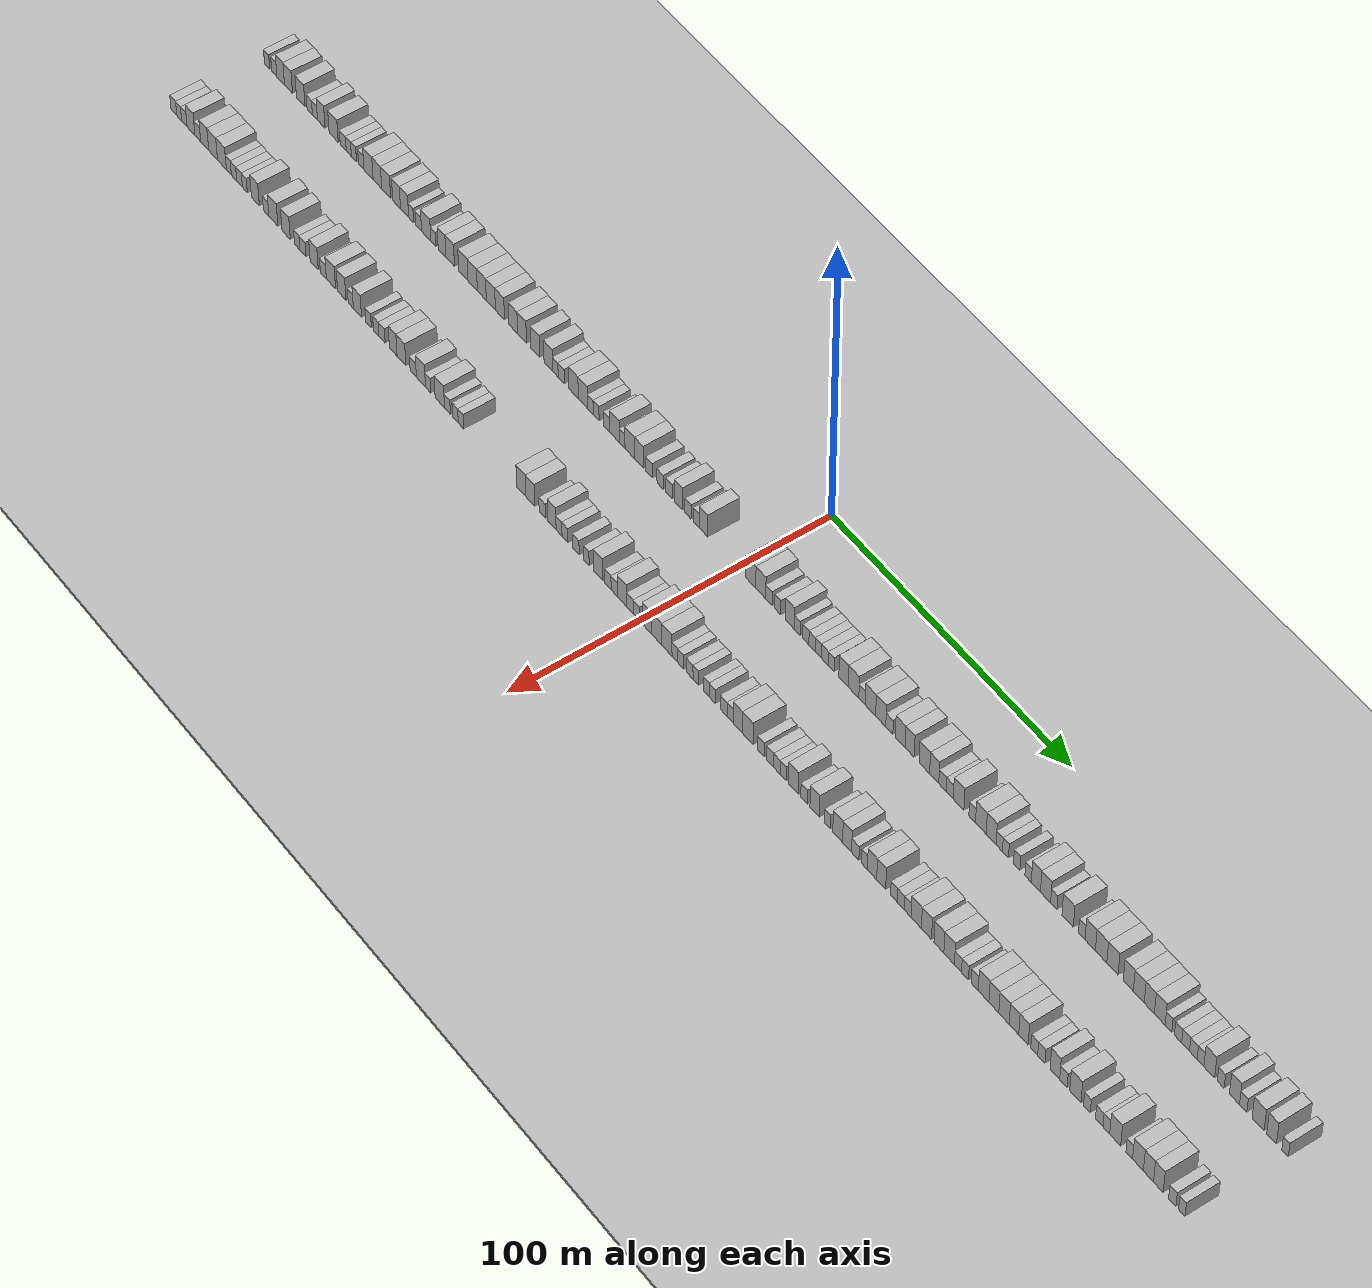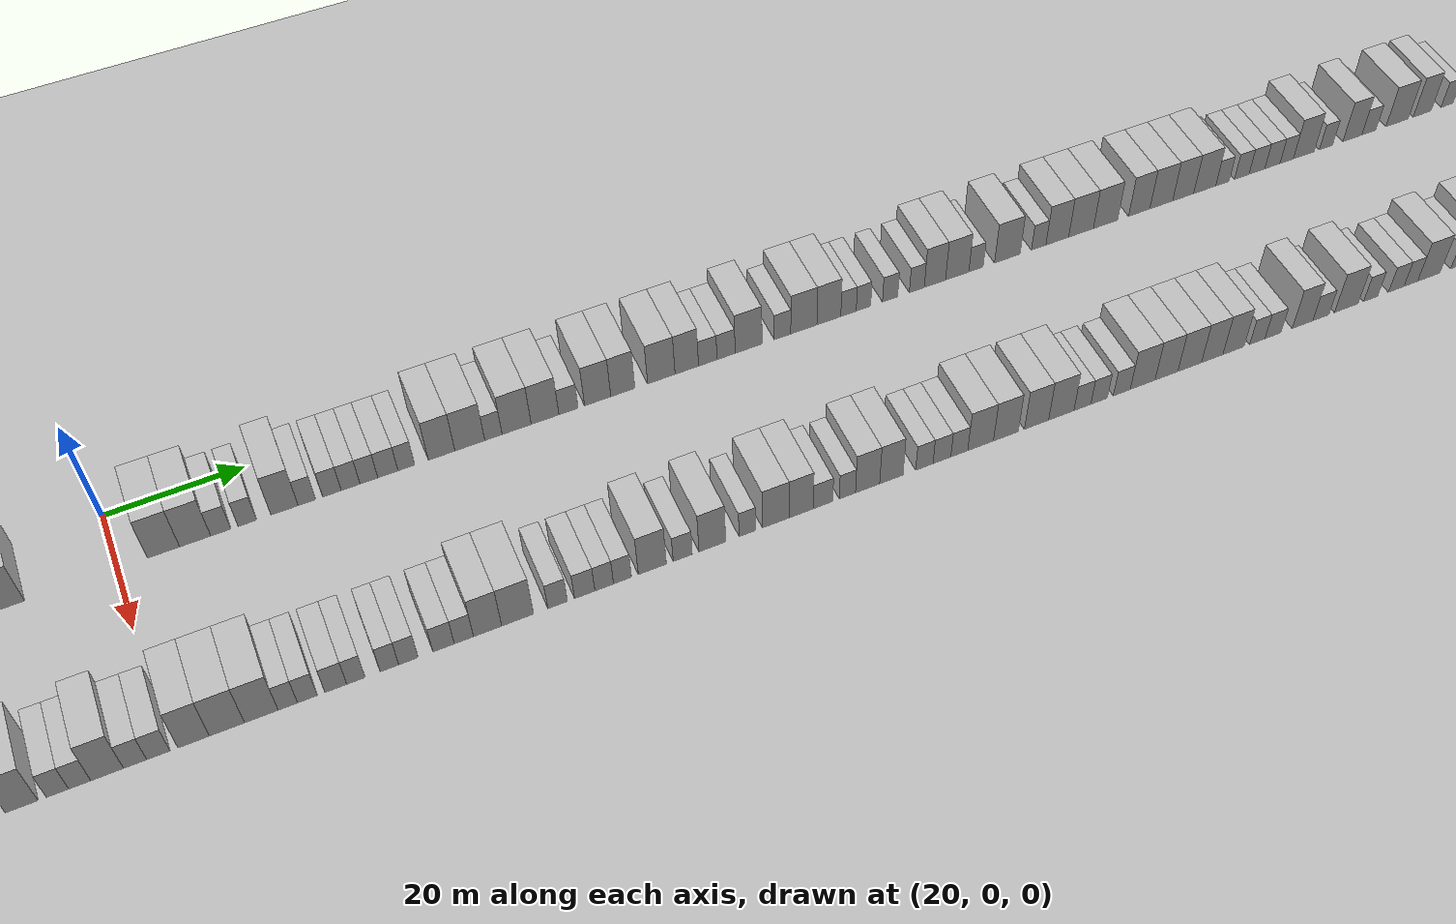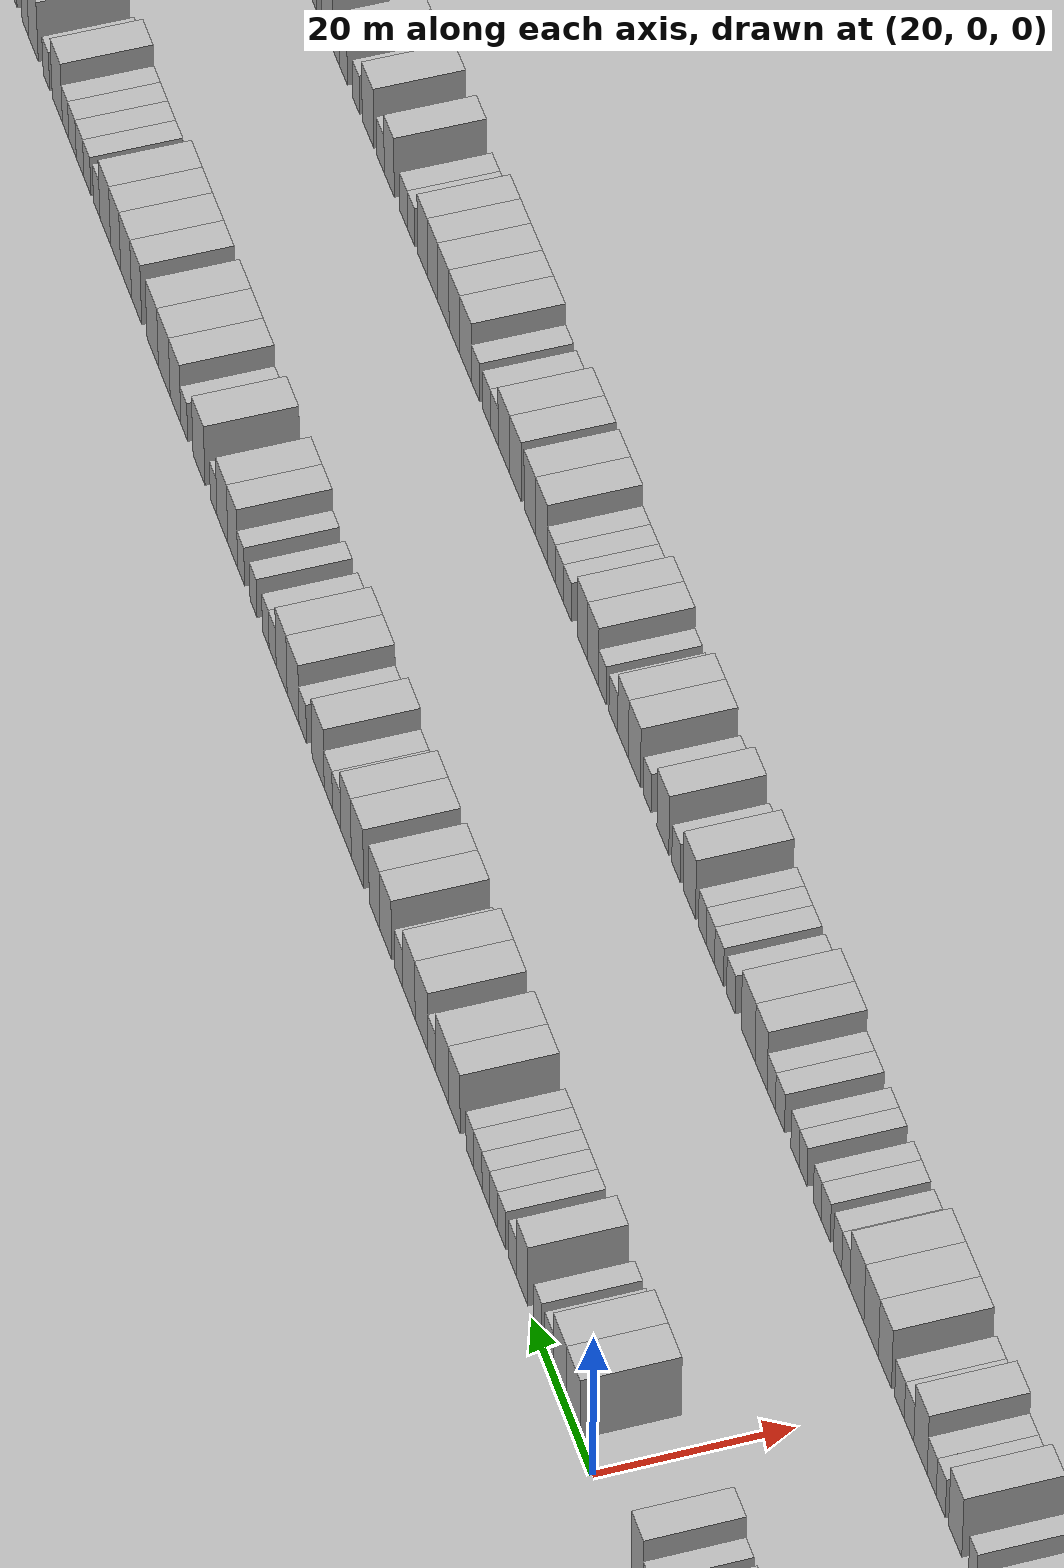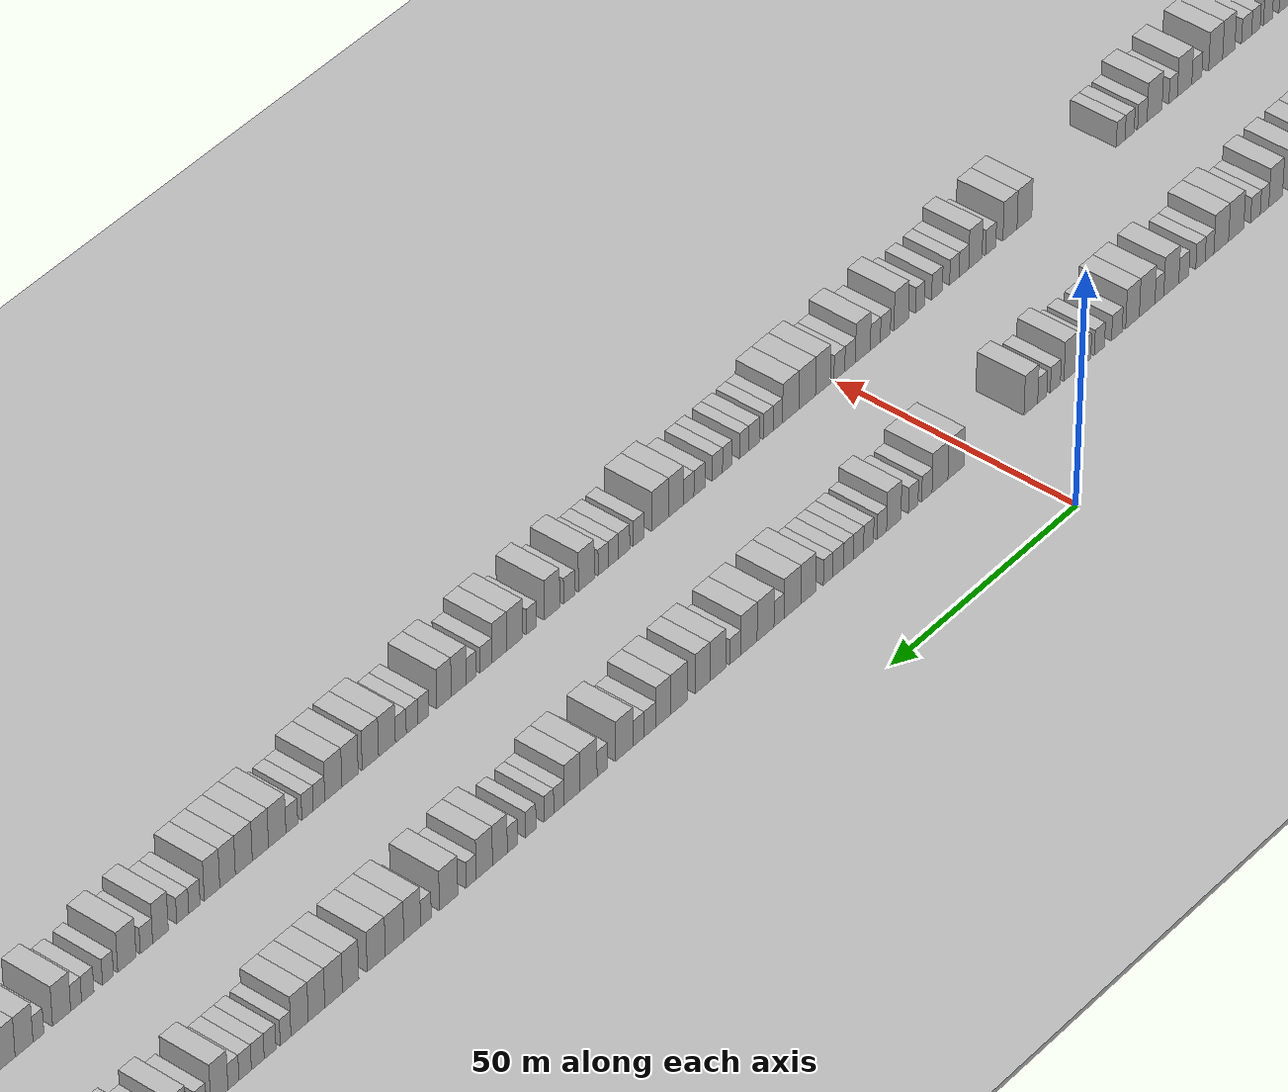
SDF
<?xml version="1.0" encoding="utf-8"?>

<sdf version="1.6">

   <world name="default">

      <gui fullscreen="0">

         <camera name="user_camera">

            <pose>-15 0 4.57585 0 0 0</pose>

            <view_controller>orbit</view_controller>

         </camera>

      </gui>

      <scene>

         <sky>

           <clouds>

             <speed>12</speed>

           </clouds>

         </sky>

         <ambient>0.4 0.4 0.4 1</ambient>

         <background>0.7 0.7 0.7 1</background>

         <shadows>1</shadows>

      </scene>

      <gravity>0 0 -9.8066</gravity>

      <magnetic_field>6e-06 2.3e-05 -4.2e-05</magnetic_field>

      <physics default="0" name="default_physics" type="ode">

         <ode>

            <solver>

               <type>quick</type>

               <iters>10</iters>

               <sor>1.0</sor>

               <use_dynamic_moi_rescaling>0</use_dynamic_moi_rescaling>

            </solver>

            <constraints>

               <cfm>0</cfm>

               <erp>0.2</erp>

               <contact_max_correcting_vel>100</contact_max_correcting_vel>

               <contact_surface_layer>0.001</contact_surface_layer>

            </constraints>

         </ode>

         <max_step_size>0.004</max_step_size>

         <real_time_factor>1</real_time_factor>

         <real_time_update_rate>250</real_time_update_rate>

      </physics>

      <light name="sun" type="directional">

         <cast_shadows>1</cast_shadows>

         <pose>0 0 10 0 0 0</pose>

         <diffuse>0.8 0.8 0.8 1</diffuse>

         <specular>0.2 0.2 0.2 1</specular>

         <attenuation>

            <range>1000</range>

            <constant>0.9</constant>

            <linear>0.01</linear>

            <quadratic>0.001</quadratic>

         </attenuation>

         <direction>-0.5 0.1 -0.9</direction>

      </light>

      <include>

         <name>ground_plane_1</name>

         <uri>model://HANNAS_ground_plane</uri>

         <pose>0 0 0  0 0 0</pose>

      </include>

      <include>

         <name>ground_plane_2</name>

         <uri>model://HANNAS_ground_plane</uri>

         <pose>100 0 0  0 0 0</pose>

      </include>

      <model name="building_1">

         <static>1</static>

         <pose frame="">25.0000 -218.6890 0 0.000000 0.000000 0.000000</pose>

         <link name="link">

            <pose frame="">0 0 3.00 0 0 0</pose>

            <collision name="collision">

               <geometry>

                  <box>

                     <size>10.0000 2.6220 6.0000</size>

                  </box>

               </geometry>

               <max_contacts>10</max_contacts>

               <surface>

                  <contact>

                     <ode/>

                  </contact>

                  <bounce/>

                  <friction>

                     <torsional>

                        <ode/>

                     </torsional>

                     <ode/>

                  </friction>

               </surface>

            </collision>

            <visual name="visual">

               <cast_shadows>0</cast_shadows>

               <geometry>

                  <box>

                     <size>10.0000 2.6220 6.0000</size>

                  </box>

               </geometry>

               <material>

                  <script>

                     <uri>model://HANNAS_wall/materials/scripts</uri>

                     <uri>model://HANNAS_wall/materials/textures</uri>

                     <name>vrc/HANNAS_wall</name>

                  </script>

               </material>

            </visual>

            <self_collide>0</self_collide>

            <enable_wind>0</enable_wind>

            <kinematic>0</kinematic>

         </link>

      </model>

      <model name="building_2">

         <static>1</static>

         <pose frame="">25.0000 -215.0693 0 0.000000 0.000000 0.000000</pose>

         <link name="link">

            <pose frame="">0 0 3.00 0 0 0</pose>

            <collision name="collision">

               <geometry>

                  <box>

                     <size>10.0000 2.6174 6.0000</size>

                  </box>

               </geometry>

               <max_contacts>10</max_contacts>

               <surface>

                  <contact>

                     <ode/>

                  </contact>

                  <bounce/>

                  <friction>

                     <torsional>

                        <ode/>

                     </torsional>

                     <ode/>

                  </friction>

               </surface>

            </collision>

            <visual name="visual">

               <cast_shadows>0</cast_shadows>

               <geometry>

                  <box>

                     <size>10.0000 2.6174 6.0000</size>

                  </box>

               </geometry>

               <material>

                  <script>

                     <uri>model://HANNAS_wall/materials/scripts</uri>

                     <uri>model://HANNAS_wall/materials/textures</uri>

                     <name>vrc/HANNAS_wall</name>

                  </script>

               </material>

            </visual>

            <self_collide>0</self_collide>

            <enable_wind>0</enable_wind>

            <kinematic>0</kinematic>

         </link>

      </model>

      <model name="building_3">

         <static>1</static>

         <pose frame="">25.0000 -211.8674 0 0.000000 0.000000 0.000000</pose>

         <link name="link">

            <pose frame="">0 0 4.50 0 0 0</pose>

            <collision name="collision">

               <geometry>

                  <box>

                     <size>10.0000 3.7865 9.0000</size>

                  </box>

               </geometry>

               <max_contacts>10</max_contacts>

               <surface>

                  <contact>

                     <ode/>

                  </contact>

                  <bounce/>

                  <friction>

                     <torsional>

                        <ode/>

                     </torsional>

                     <ode/>

                  </friction>

               </surface>

            </collision>

            <visual name="visual">

               <cast_shadows>0</cast_shadows>

               <geometry>

                  <box>

                     <size>10.0000 3.7865 9.0000</size>

                  </box>

               </geometry>

               <material>

                  <script>

                     <uri>model://HANNAS_wall/materials/scripts</uri>

                     <uri>model://HANNAS_wall/materials/textures</uri>

                     <name>vrc/HANNAS_wall</name>

                  </script>

               </material>

            </visual>

            <self_collide>0</self_collide>

            <enable_wind>0</enable_wind>

            <kinematic>0</kinematic>

         </link>

      </model>

      <model name="building_4">

         <static>1</static>

         <pose frame="">25.0000 -207.9781 0 0.000000 0.000000 0.000000</pose>

         <link name="link">

            <pose frame="">0 0 4.50 0 0 0</pose>

            <collision name="collision">

               <geometry>

                  <box>

                     <size>10.0000 3.9921 9.0000</size>

                  </box>

               </geometry>

               <max_contacts>10</max_contacts>

               <surface>

                  <contact>

                     <ode/>

                  </contact>

                  <bounce/>

                  <friction>

                     <torsional>

                        <ode/>

                     </torsional>

                     <ode/>

                  </friction>

               </surface>

            </collision>

            <visual name="visual">

               <cast_shadows>0</cast_shadows>

               <geometry>

                  <box>

                     <size>10.0000 3.9921 9.0000</size>

                  </box>

               </geometry>

               <material>

                  <script>

                     <uri>model://HANNAS_wall/materials/scripts</uri>

                     <uri>model://HANNAS_wall/materials/textures</uri>

                     <name>vrc/HANNAS_wall</name>

                  </script>

               </material>

            </visual>

            <self_collide>0</self_collide>

            <enable_wind>0</enable_wind>

            <kinematic>0</kinematic>

         </link>

      </model>

      <model name="building_5">

         <static>1</static>

         <pose frame="">25.0000 -201.8589 0 0.000000 0.000000 0.000000</pose>

         <link name="link">

            <pose frame="">0 0 4.50 0 0 0</pose>

            <collision name="collision">

               <geometry>

                  <box>

                     <size>10.0000 4.2463 9.0000</size>

                  </box>

               </geometry>

               <max_contacts>10</max_contacts>

               <surface>

                  <contact>

                     <ode/>

                  </contact>

                  <bounce/>

                  <friction>

                     <torsional>

                        <ode/>

                     </torsional>

                     <ode/>

                  </friction>

               </surface>

            </collision>

            <visual name="visual">

               <cast_shadows>0</cast_shadows>

               <geometry>

                  <box>

                     <size>10.0000 4.2463 9.0000</size>

                  </box>

               </geometry>

               <material>

                  <script>

                     <uri>model://HANNAS_wall/materials/scripts</uri>

                     <uri>model://HANNAS_wall/materials/textures</uri>

                     <name>vrc/HANNAS_wall</name>

                  </script>

               </material>

            </visual>

            <self_collide>0</self_collide>

            <enable_wind>0</enable_wind>

            <kinematic>0</kinematic>

         </link>

      </model>

      <model name="building_6">

         <static>1</static>

         <pose frame="">25.0000 -197.4302 0 0.000000 0.000000 0.000000</pose>

         <link name="link">

            <pose frame="">0 0 3.00 0 0 0</pose>

            <collision name="collision">

               <geometry>

                  <box>

                     <size>10.0000 2.6111 6.0000</size>

                  </box>

               </geometry>

               <max_contacts>10</max_contacts>

               <surface>

                  <contact>

                     <ode/>

                  </contact>

                  <bounce/>

                  <friction>

                     <torsional>

                        <ode/>

                     </torsional>

                     <ode/>

                  </friction>

               </surface>

            </collision>

            <visual name="visual">

               <cast_shadows>0</cast_shadows>

               <geometry>

                  <box>

                     <size>10.0000 2.6111 6.0000</size>

                  </box>

               </geometry>

               <material>

                  <script>

                     <uri>model://HANNAS_wall/materials/scripts</uri>

                     <uri>model://HANNAS_wall/materials/textures</uri>

                     <name>vrc/HANNAS_wall</name>

                  </script>

               </material>

            </visual>

            <self_collide>0</self_collide>

            <enable_wind>0</enable_wind>

            <kinematic>0</kinematic>

         </link>

      </model>

      <model name="building_7">

         <static>1</static>

         <pose frame="">25.0000 -194.8632 0 0.000000 0.000000 0.000000</pose>

         <link name="link">

            <pose frame="">0 0 3.00 0 0 0</pose>

            <collision name="collision">

               <geometry>

                  <box>

                     <size>10.0000 2.5228 6.0000</size>

                  </box>

               </geometry>

               <max_contacts>10</max_contacts>

               <surface>

                  <contact>

                     <ode/>

                  </contact>

                  <bounce/>

                  <friction>

                     <torsional>

                        <ode/>

                     </torsional>

                     <ode/>

                  </friction>

               </surface>

            </collision>

            <visual name="visual">

               <cast_shadows>0</cast_shadows>

               <geometry>

                  <box>

                     <size>10.0000 2.5228 6.0000</size>

                  </box>

               </geometry>

               <material>

                  <script>

                     <uri>model://HANNAS_wall/materials/scripts</uri>

                     <uri>model://HANNAS_wall/materials/textures</uri>

                     <name>vrc/HANNAS_wall</name>

                  </script>

               </material>

            </visual>

            <self_collide>0</self_collide>

            <enable_wind>0</enable_wind>

            <kinematic>0</kinematic>

         </link>

      </model>

      <model name="building_8">

         <static>1</static>

         <pose frame="">25.0000 -191.7290 0 0.000000 0.000000 0.000000</pose>

         <link name="link">

            <pose frame="">0 0 4.50 0 0 0</pose>

            <collision name="collision">

               <geometry>

                  <box>

                     <size>10.0000 3.7457 9.0000</size>

                  </box>

               </geometry>

               <max_contacts>10</max_contacts>

               <surface>

                  <contact>

                     <ode/>

                  </contact>

                  <bounce/>

                  <friction>

                     <torsional>

                        <ode/>

                     </torsional>

                     <ode/>

                  </friction>

               </surface>

            </collision>

            <visual name="visual">

               <cast_shadows>0</cast_shadows>

               <geometry>

                  <box>

                     <size>10.0000 3.7457 9.0000</size>

                  </box>

               </geometry>

               <material>

                  <script>

                     <uri>model://HANNAS_wall/materials/scripts</uri>

                     <uri>model://HANNAS_wall/materials/textures</uri>

                     <name>vrc/HANNAS_wall</name>

                  </script>

               </material>

            </visual>

            <self_collide>0</self_collide>

            <enable_wind>0</enable_wind>

            <kinematic>0</kinematic>

         </link>

      </model>

      <model name="building_9">

         <static>1</static>

         <pose frame="">25.0000 -185.6247 0 0.000000 0.000000 0.000000</pose>

         <link name="link">

            <pose frame="">0 0 4.50 0 0 0</pose>

            <collision name="collision">

               <geometry>

                  <box>

                     <size>10.0000 4.4628 9.0000</size>

                  </box>

               </geometry>

               <max_contacts>10</max_contacts>

               <surface>

                  <contact>

                     <ode/>

                  </contact>

                  <bounce/>

                  <friction>

                     <torsional>

                        <ode/>

                     </torsional>

                     <ode/>

                  </friction>

               </surface>

            </collision>

            <visual name="visual">

               <cast_shadows>0</cast_shadows>

               <geometry>

                  <box>

                     <size>10.0000 4.4628 9.0000</size>

                  </box>

               </geometry>

               <material>

                  <script>

                     <uri>model://HANNAS_wall/materials/scripts</uri>

                     <uri>model://HANNAS_wall/materials/textures</uri>

                     <name>vrc/HANNAS_wall</name>

                  </script>

               </material>

            </visual>

            <self_collide>0</self_collide>

            <enable_wind>0</enable_wind>

            <kinematic>0</kinematic>

         </link>

      </model>

      <model name="building_10">

         <static>1</static>

         <pose frame="">25.0000 -180.9236 0 0.000000 0.000000 0.000000</pose>

         <link name="link">

            <pose frame="">0 0 3.00 0 0 0</pose>

            <collision name="collision">

               <geometry>

                  <box>

                     <size>10.0000 2.9394 6.0000</size>

                  </box>

               </geometry>

               <max_contacts>10</max_contacts>

               <surface>

                  <contact>

                     <ode/>

                  </contact>

                  <bounce/>

                  <friction>

                     <torsional>

                        <ode/>

                     </torsional>

                     <ode/>

                  </friction>

               </surface>

            </collision>

            <visual name="visual">

               <cast_shadows>0</cast_shadows>

               <geometry>

                  <box>

                     <size>10.0000 2.9394 6.0000</size>

                  </box>

               </geometry>

               <material>

                  <script>

                     <uri>model://HANNAS_wall/materials/scripts</uri>

                     <uri>model://HANNAS_wall/materials/textures</uri>

                     <name>vrc/HANNAS_wall</name>

                  </script>

               </material>

            </visual>

            <self_collide>0</self_collide>

            <enable_wind>0</enable_wind>

            <kinematic>0</kinematic>

         </link>

      </model>

      <model name="building_11">

         <static>1</static>

         <pose frame="">25.0000 -178.1855 0 0.000000 0.000000 0.000000</pose>

         <link name="link">

            <pose frame="">0 0 3.00 0 0 0</pose>

            <collision name="collision">

               <geometry>

                  <box>

                     <size>10.0000 2.5367 6.0000</size>

                  </box>

               </geometry>

               <max_contacts>10</max_contacts>

               <surface>

                  <contact>

                     <ode/>

                  </contact>

                  <bounce/>

                  <friction>

                     <torsional>

                        <ode/>

                     </torsional>

                     <ode/>

                  </friction>

               </surface>

            </collision>

            <visual name="visual">

               <cast_shadows>0</cast_shadows>

               <geometry>

                  <box>

                     <size>10.0000 2.5367 6.0000</size>

                  </box>

               </geometry>

               <material>

                  <script>

                     <uri>model://HANNAS_wall/materials/scripts</uri>

                     <uri>model://HANNAS_wall/materials/textures</uri>

                     <name>vrc/HANNAS_wall</name>

                  </script>

               </material>

            </visual>

            <self_collide>0</self_collide>

            <enable_wind>0</enable_wind>

            <kinematic>0</kinematic>

         </link>

      </model>

      <model name="building_12">

         <static>1</static>

         <pose frame="">25.0000 -175.6837 0 0.000000 0.000000 0.000000</pose>

         <link name="link">

            <pose frame="">0 0 3.00 0 0 0</pose>

            <collision name="collision">

               <geometry>

                  <box>

                     <size>10.0000 2.4669 6.0000</size>

                  </box>

               </geometry>

               <max_contacts>10</max_contacts>

               <surface>

                  <contact>

                     <ode/>

                  </contact>

                  <bounce/>

                  <friction>

                     <torsional>

                        <ode/>

                     </torsional>

                     <ode/>

                  </friction>

               </surface>

            </collision>

            <visual name="visual">

               <cast_shadows>0</cast_shadows>

               <geometry>

                  <box>

                     <size>10.0000 2.4669 6.0000</size>

                  </box>

               </geometry>

               <material>

                  <script>

                     <uri>model://HANNAS_wall/materials/scripts</uri>

                     <uri>model://HANNAS_wall/materials/textures</uri>

                     <name>vrc/HANNAS_wall</name>

                  </script>

               </material>

            </visual>

            <self_collide>0</self_collide>

            <enable_wind>0</enable_wind>

            <kinematic>0</kinematic>

         </link>

      </model>

      <model name="building_13">

         <static>1</static>

         <pose frame="">25.0000 -172.1369 0 0.000000 0.000000 0.000000</pose>

         <link name="link">

            <pose frame="">0 0 3.00 0 0 0</pose>

            <collision name="collision">

               <geometry>

                  <box>

                     <size>10.0000 2.6267 6.0000</size>

                  </box>

               </geometry>

               <max_contacts>10</max_contacts>

               <surface>

                  <contact>

                     <ode/>

                  </contact>

                  <bounce/>

                  <friction>

                     <torsional>

                        <ode/>

                     </torsional>

                     <ode/>

                  </friction>

               </surface>

            </collision>

            <visual name="visual">

               <cast_shadows>0</cast_shadows>

               <geometry>

                  <box>

                     <size>10.0000 2.6267 6.0000</size>

                  </box>

               </geometry>

               <material>

                  <script>

                     <uri>model://HANNAS_wall/materials/scripts</uri>

                     <uri>model://HANNAS_wall/materials/textures</uri>

                     <name>vrc/HANNAS_wall</name>

                  </script>

               </material>

            </visual>

            <self_collide>0</self_collide>

            <enable_wind>0</enable_wind>

            <kinematic>0</kinematic>

         </link>

      </model>

      <model name="building_14">

         <static>1</static>

         <pose frame="">25.0000 -168.6002 0 0.000000 0.000000 0.000000</pose>

         <link name="link">

            <pose frame="">0 0 4.50 0 0 0</pose>

            <collision name="collision">

               <geometry>

                  <box>

                     <size>10.0000 4.4468 9.0000</size>

                  </box>

               </geometry>

               <max_contacts>10</max_contacts>

               <surface>

                  <contact>

                     <ode/>

                  </contact>

                  <bounce/>

                  <friction>

                     <torsional>

                        <ode/>

                     </torsional>

                     <ode/>

                  </friction>

               </surface>

            </collision>

            <visual name="visual">

               <cast_shadows>0</cast_shadows>

               <geometry>

                  <box>

                     <size>10.0000 4.4468 9.0000</size>

                  </box>

               </geometry>

               <material>

                  <script>

                     <uri>model://HANNAS_wall/materials/scripts</uri>

                     <uri>model://HANNAS_wall/materials/textures</uri>

                     <name>vrc/HANNAS_wall</name>

                  </script>

               </material>

            </visual>

            <self_collide>0</self_collide>

            <enable_wind>0</enable_wind>

            <kinematic>0</kinematic>

         </link>

      </model>

      <model name="building_15">

         <static>1</static>

         <pose frame="">25.0000 -164.2904 0 0.000000 0.000000 0.000000</pose>

         <link name="link">

            <pose frame="">0 0 4.50 0 0 0</pose>

            <collision name="collision">

               <geometry>

                  <box>

                     <size>10.0000 4.1727 9.0000</size>

                  </box>

               </geometry>

               <max_contacts>10</max_contacts>

               <surface>

                  <contact>

                     <ode/>

                  </contact>

                  <bounce/>

                  <friction>

                     <torsional>

                        <ode/>

                     </torsional>

                     <ode/>

                  </friction>

               </surface>

            </collision>

            <visual name="visual">

               <cast_shadows>0</cast_shadows>

               <geometry>

                  <box>

                     <size>10.0000 4.1727 9.0000</size>

                  </box>

               </geometry>

               <material>

                  <script>

                     <uri>model://HANNAS_wall/materials/scripts</uri>

                     <uri>model://HANNAS_wall/materials/textures</uri>

                     <name>vrc/HANNAS_wall</name>

                  </script>

               </material>

            </visual>

            <self_collide>0</self_collide>

            <enable_wind>0</enable_wind>

            <kinematic>0</kinematic>

         </link>

      </model>

      <model name="building_16">

         <static>1</static>

         <pose frame="">25.0000 -160.0362 0 0.000000 0.000000 0.000000</pose>

         <link name="link">

            <pose frame="">0 0 4.50 0 0 0</pose>

            <collision name="collision">

               <geometry>

                  <box>

                     <size>10.0000 4.3358 9.0000</size>

                  </box>

               </geometry>

               <max_contacts>10</max_contacts>

               <surface>

                  <contact>

                     <ode/>

                  </contact>

                  <bounce/>

                  <friction>

                     <torsional>

                        <ode/>

                     </torsional>

                     <ode/>

                  </friction>

               </surface>

            </collision>

            <visual name="visual">

               <cast_shadows>0</cast_shadows>

               <geometry>

                  <box>

                     <size>10.0000 4.3358 9.0000</size>

                  </box>

               </geometry>

               <material>

                  <script>

                     <uri>model://HANNAS_wall/materials/scripts</uri>

                     <uri>model://HANNAS_wall/materials/textures</uri>

                     <name>vrc/HANNAS_wall</name>

                  </script>

               </material>

            </visual>

            <self_collide>0</self_collide>

            <enable_wind>0</enable_wind>

            <kinematic>0</kinematic>

         </link>

      </model>

      <model name="building_17">

         <static>1</static>

         <pose frame="">25.0000 -155.0106 0 0.000000 0.000000 0.000000</pose>

         <link name="link">

            <pose frame="">0 0 4.50 0 0 0</pose>

            <collision name="collision">

               <geometry>

                  <box>

                     <size>10.0000 3.7152 9.0000</size>

                  </box>

               </geometry>

               <max_contacts>10</max_contacts>

               <surface>

                  <contact>

                     <ode/>

                  </contact>

                  <bounce/>

                  <friction>

                     <torsional>

                        <ode/>

                     </torsional>

                     <ode/>

                  </friction>

               </surface>

            </collision>

            <visual name="visual">

               <cast_shadows>0</cast_shadows>

               <geometry>

                  <box>

                     <size>10.0000 3.7152 9.0000</size>

                  </box>

               </geometry>

               <material>

                  <script>

                     <uri>model://HANNAS_wall/materials/scripts</uri>

                     <uri>model://HANNAS_wall/materials/textures</uri>

                     <name>vrc/HANNAS_wall</name>

                  </script>

               </material>

            </visual>

            <self_collide>0</self_collide>

            <enable_wind>0</enable_wind>

            <kinematic>0</kinematic>

         </link>

      </model>

      <model name="building_18">

         <static>1</static>

         <pose frame="">25.0000 -151.1939 0 0.000000 0.000000 0.000000</pose>

         <link name="link">

            <pose frame="">0 0 4.50 0 0 0</pose>

            <collision name="collision">

               <geometry>

                  <box>

                     <size>10.0000 3.9182 9.0000</size>

                  </box>

               </geometry>

               <max_contacts>10</max_contacts>

               <surface>

                  <contact>

                     <ode/>

                  </contact>

                  <bounce/>

                  <friction>

                     <torsional>

                        <ode/>

                     </torsional>

                     <ode/>

                  </friction>

               </surface>

            </collision>

            <visual name="visual">

               <cast_shadows>0</cast_shadows>

               <geometry>

                  <box>

                     <size>10.0000 3.9182 9.0000</size>

                  </box>

               </geometry>

               <material>

                  <script>

                     <uri>model://HANNAS_wall/materials/scripts</uri>

                     <uri>model://HANNAS_wall/materials/textures</uri>

                     <name>vrc/HANNAS_wall</name>

                  </script>

               </material>

            </visual>

            <self_collide>0</self_collide>

            <enable_wind>0</enable_wind>

            <kinematic>0</kinematic>

         </link>

      </model>

      <model name="building_19">

         <static>1</static>

         <pose frame="">25.0000 -148.0293 0 0.000000 0.000000 0.000000</pose>

         <link name="link">

            <pose frame="">0 0 3.00 0 0 0</pose>

            <collision name="collision">

               <geometry>

                  <box>

                     <size>10.0000 2.4110 6.0000</size>

                  </box>

               </geometry>

               <max_contacts>10</max_contacts>

               <surface>

                  <contact>

                     <ode/>

                  </contact>

                  <bounce/>

                  <friction>

                     <torsional>

                        <ode/>

                     </torsional>

                     <ode/>

                  </friction>

               </surface>

            </collision>

            <visual name="visual">

               <cast_shadows>0</cast_shadows>

               <geometry>

                  <box>

                     <size>10.0000 2.4110 6.0000</size>

                  </box>

               </geometry>

               <material>

                  <script>

                     <uri>model://HANNAS_wall/materials/scripts</uri>

                     <uri>model://HANNAS_wall/materials/textures</uri>

                     <name>vrc/HANNAS_wall</name>

                  </script>

               </material>

            </visual>

            <self_collide>0</self_collide>

            <enable_wind>0</enable_wind>

            <kinematic>0</kinematic>

         </link>

      </model>

      <model name="building_20">

         <static>1</static>

         <pose frame="">25.0000 -144.4328 0 0.000000 0.000000 0.000000</pose>

         <link name="link">

            <pose frame="">0 0 3.00 0 0 0</pose>

            <collision name="collision">

               <geometry>

                  <box>

                     <size>10.0000 2.7820 6.0000</size>

                  </box>

               </geometry>

               <max_contacts>10</max_contacts>

               <surface>

                  <contact>

                     <ode/>

                  </contact>

                  <bounce/>

                  <friction>

                     <torsional>

                        <ode/>

                     </torsional>

                     <ode/>

                  </friction>

               </surface>

            </collision>

            <visual name="visual">

               <cast_shadows>0</cast_shadows>

               <geometry>

                  <box>

                     <size>10.0000 2.7820 6.0000</size>

                  </box>

               </geometry>

               <material>

                  <script>

                     <uri>model://HANNAS_wall/materials/scripts</uri>

                     <uri>model://HANNAS_wall/materials/textures</uri>

                     <name>vrc/HANNAS_wall</name>

                  </script>

               </material>

            </visual>

            <self_collide>0</self_collide>

            <enable_wind>0</enable_wind>

            <kinematic>0</kinematic>

         </link>

      </model>

      <model name="building_21">

         <static>1</static>

         <pose frame="">25.0000 -140.8264 0 0.000000 0.000000 0.000000</pose>

         <link name="link">

            <pose frame="">0 0 4.50 0 0 0</pose>

            <collision name="collision">

               <geometry>

                  <box>

                     <size>10.0000 4.4308 9.0000</size>

                  </box>

               </geometry>

               <max_contacts>10</max_contacts>

               <surface>

                  <contact>

                     <ode/>

                  </contact>

                  <bounce/>

                  <friction>

                     <torsional>

                        <ode/>

                     </torsional>

                     <ode/>

                  </friction>

               </surface>

            </collision>

            <visual name="visual">

               <cast_shadows>0</cast_shadows>

               <geometry>

                  <box>

                     <size>10.0000 4.4308 9.0000</size>

                  </box>

               </geometry>

               <material>

                  <script>

                     <uri>model://HANNAS_wall/materials/scripts</uri>

                     <uri>model://HANNAS_wall/materials/textures</uri>

                     <name>vrc/HANNAS_wall</name>

                  </script>

               </material>

            </visual>

            <self_collide>0</self_collide>

            <enable_wind>0</enable_wind>

            <kinematic>0</kinematic>

         </link>

      </model>

      <model name="building_22">

         <static>1</static>

         <pose frame="">25.0000 -137.3676 0 0.000000 0.000000 0.000000</pose>

         <link name="link">

            <pose frame="">0 0 3.00 0 0 0</pose>

            <collision name="collision">

               <geometry>

                  <box>

                     <size>10.0000 2.4869 6.0000</size>

                  </box>

               </geometry>

               <max_contacts>10</max_contacts>

               <surface>

                  <contact>

                     <ode/>

                  </contact>

                  <bounce/>

                  <friction>

                     <torsional>

                        <ode/>

                     </torsional>

                     <ode/>

                  </friction>

               </surface>

            </collision>

            <visual name="visual">

               <cast_shadows>0</cast_shadows>

               <geometry>

                  <box>

                     <size>10.0000 2.4869 6.0000</size>

                  </box>

               </geometry>

               <material>

                  <script>

                     <uri>model://HANNAS_wall/materials/scripts</uri>

                     <uri>model://HANNAS_wall/materials/textures</uri>

                     <name>vrc/HANNAS_wall</name>

                  </script>

               </material>

            </visual>

            <self_collide>0</self_collide>

            <enable_wind>0</enable_wind>

            <kinematic>0</kinematic>

         </link>

      </model>

      <model name="building_23">

         <static>1</static>

         <pose frame="">25.0000 -133.2943 0 0.000000 0.000000 0.000000</pose>

         <link name="link">

            <pose frame="">0 0 4.50 0 0 0</pose>

            <collision name="collision">

               <geometry>

                  <box>

                     <size>10.0000 3.6598 9.0000</size>

                  </box>

               </geometry>

               <max_contacts>10</max_contacts>

               <surface>

                  <contact>

                     <ode/>

                  </contact>

                  <bounce/>

                  <friction>

                     <torsional>

                        <ode/>

                     </torsional>

                     <ode/>

                  </friction>

               </surface>

            </collision>

            <visual name="visual">

               <cast_shadows>0</cast_shadows>

               <geometry>

                  <box>

                     <size>10.0000 3.6598 9.0000</size>

                  </box>

               </geometry>

               <material>

                  <script>

                     <uri>model://HANNAS_wall/materials/scripts</uri>

                     <uri>model://HANNAS_wall/materials/textures</uri>

                     <name>vrc/HANNAS_wall</name>

                  </script>

               </material>

            </visual>

            <self_collide>0</self_collide>

            <enable_wind>0</enable_wind>

            <kinematic>0</kinematic>

         </link>

      </model>

      <model name="building_24">

         <static>1</static>

         <pose frame="">25.0000 -129.4338 0 0.000000 0.000000 0.000000</pose>

         <link name="link">

            <pose frame="">0 0 4.50 0 0 0</pose>

            <collision name="collision">

               <geometry>

                  <box>

                     <size>10.0000 4.0611 9.0000</size>

                  </box>

               </geometry>

               <max_contacts>10</max_contacts>

               <surface>

                  <contact>

                     <ode/>

                  </contact>

                  <bounce/>

                  <friction>

                     <torsional>

                        <ode/>

                     </torsional>

                     <ode/>

                  </friction>

               </surface>

            </collision>

            <visual name="visual">

               <cast_shadows>0</cast_shadows>

               <geometry>

                  <box>

                     <size>10.0000 4.0611 9.0000</size>

                  </box>

               </geometry>

               <material>

                  <script>

                     <uri>model://HANNAS_wall/materials/scripts</uri>

                     <uri>model://HANNAS_wall/materials/textures</uri>

                     <name>vrc/HANNAS_wall</name>

                  </script>

               </material>

            </visual>

            <self_collide>0</self_collide>

            <enable_wind>0</enable_wind>

            <kinematic>0</kinematic>

         </link>

      </model>

      <model name="building_25">

         <static>1</static>

         <pose frame="">25.0000 -123.2111 0 0.000000 0.000000 0.000000</pose>

         <link name="link">

            <pose frame="">0 0 4.50 0 0 0</pose>

            <collision name="collision">

               <geometry>

                  <box>

                     <size>10.0000 4.3843 9.0000</size>

                  </box>

               </geometry>

               <max_contacts>10</max_contacts>

               <surface>

                  <contact>

                     <ode/>

                  </contact>

                  <bounce/>

                  <friction>

                     <torsional>

                        <ode/>

                     </torsional>

                     <ode/>

                  </friction>

               </surface>

            </collision>

            <visual name="visual">

               <cast_shadows>0</cast_shadows>

               <geometry>

                  <box>

                     <size>10.0000 4.3843 9.0000</size>

                  </box>

               </geometry>

               <material>

                  <script>

                     <uri>model://HANNAS_wall/materials/scripts</uri>

                     <uri>model://HANNAS_wall/materials/textures</uri>

                     <name>vrc/HANNAS_wall</name>

                  </script>

               </material>

            </visual>

            <self_collide>0</self_collide>

            <enable_wind>0</enable_wind>

            <kinematic>0</kinematic>

         </link>

      </model>

      <model name="building_26">

         <static>1</static>

         <pose frame="">25.0000 -118.8185 0 0.000000 0.000000 0.000000</pose>

         <link name="link">

            <pose frame="">0 0 4.50 0 0 0</pose>

            <collision name="collision">

               <geometry>

                  <box>

                     <size>10.0000 4.4011 9.0000</size>

                  </box>

               </geometry>

               <max_contacts>10</max_contacts>

               <surface>

                  <contact>

                     <ode/>

                  </contact>

                  <bounce/>

                  <friction>

                     <torsional>

                        <ode/>

                     </torsional>

                     <ode/>

                  </friction>

               </surface>

            </collision>

            <visual name="visual">

               <cast_shadows>0</cast_shadows>

               <geometry>

                  <box>

                     <size>10.0000 4.4011 9.0000</size>

                  </box>

               </geometry>

               <material>

                  <script>

                     <uri>model://HANNAS_wall/materials/scripts</uri>

                     <uri>model://HANNAS_wall/materials/textures</uri>

                     <name>vrc/HANNAS_wall</name>

                  </script>

               </material>

            </visual>

            <self_collide>0</self_collide>

            <enable_wind>0</enable_wind>

            <kinematic>0</kinematic>

         </link>

      </model>

      <model name="building_27">

         <static>1</static>

         <pose frame="">25.0000 -114.5217 0 0.000000 0.000000 0.000000</pose>

         <link name="link">

            <pose frame="">0 0 4.50 0 0 0</pose>

            <collision name="collision">

               <geometry>

                  <box>

                     <size>10.0000 4.1925 9.0000</size>

                  </box>

               </geometry>

               <max_contacts>10</max_contacts>

               <surface>

                  <contact>

                     <ode/>

                  </contact>

                  <bounce/>

                  <friction>

                     <torsional>

                        <ode/>

                     </torsional>

                     <ode/>

                  </friction>

               </surface>

            </collision>

            <visual name="visual">

               <cast_shadows>0</cast_shadows>

               <geometry>

                  <box>

                     <size>10.0000 4.1925 9.0000</size>

                  </box>

               </geometry>

               <material>

                  <script>

                     <uri>model://HANNAS_wall/materials/scripts</uri>

                     <uri>model://HANNAS_wall/materials/textures</uri>

                     <name>vrc/HANNAS_wall</name>

                  </script>

               </material>

            </visual>

            <self_collide>0</self_collide>

            <enable_wind>0</enable_wind>

            <kinematic>0</kinematic>

         </link>

      </model>

      <model name="building_28">

         <static>1</static>

         <pose frame="">25.0000 -110.2871 0 0.000000 0.000000 0.000000</pose>

         <link name="link">

            <pose frame="">0 0 4.50 0 0 0</pose>

            <collision name="collision">

               <geometry>

                  <box>

                     <size>10.0000 4.2766 9.0000</size>

                  </box>

               </geometry>

               <max_contacts>10</max_contacts>

               <surface>

                  <contact>

                     <ode/>

                  </contact>

                  <bounce/>

                  <friction>

                     <torsional>

                        <ode/>

                     </torsional>

                     <ode/>

                  </friction>

               </surface>

            </collision>

            <visual name="visual">

               <cast_shadows>0</cast_shadows>

               <geometry>

                  <box>

                     <size>10.0000 4.2766 9.0000</size>

                  </box>

               </geometry>

               <material>

                  <script>

                     <uri>model://HANNAS_wall/materials/scripts</uri>

                     <uri>model://HANNAS_wall/materials/textures</uri>

                     <name>vrc/HANNAS_wall</name>

                  </script>

               </material>

            </visual>

            <self_collide>0</self_collide>

            <enable_wind>0</enable_wind>

            <kinematic>0</kinematic>

         </link>

      </model>

      <model name="building_29">

         <static>1</static>

         <pose frame="">25.0000 -106.0344 0 0.000000 0.000000 0.000000</pose>

         <link name="link">

            <pose frame="">0 0 4.50 0 0 0</pose>

            <collision name="collision">

               <geometry>

                  <box>

                     <size>10.0000 4.2290 9.0000</size>

                  </box>

               </geometry>

               <max_contacts>10</max_contacts>

               <surface>

                  <contact>

                     <ode/>

                  </contact>

                  <bounce/>

                  <friction>

                     <torsional>

                        <ode/>

                     </torsional>

                     <ode/>

                  </friction>

               </surface>

            </collision>

            <visual name="visual">

               <cast_shadows>0</cast_shadows>

               <geometry>

                  <box>

                     <size>10.0000 4.2290 9.0000</size>

                  </box>

               </geometry>

               <material>

                  <script>

                     <uri>model://HANNAS_wall/materials/scripts</uri>

                     <uri>model://HANNAS_wall/materials/textures</uri>

                     <name>vrc/HANNAS_wall</name>

                  </script>

               </material>

            </visual>

            <self_collide>0</self_collide>

            <enable_wind>0</enable_wind>

            <kinematic>0</kinematic>

         </link>

      </model>

      <model name="building_30">

         <static>1</static>

         <pose frame="">25.0000 -99.8776 0 0.000000 0.000000 0.000000</pose>

         <link name="link">

            <pose frame="">0 0 4.50 0 0 0</pose>

            <collision name="collision">

               <geometry>

                  <box>

                     <size>10.0000 4.0846 9.0000</size>

                  </box>

               </geometry>

               <max_contacts>10</max_contacts>

               <surface>

                  <contact>

                     <ode/>

                  </contact>

                  <bounce/>

                  <friction>

                     <torsional>

                        <ode/>

                     </torsional>

                     <ode/>

                  </friction>

               </surface>

            </collision>

            <visual name="visual">

               <cast_shadows>0</cast_shadows>

               <geometry>

                  <box>

                     <size>10.0000 4.0846 9.0000</size>

                  </box>

               </geometry>

               <material>

                  <script>

                     <uri>model://HANNAS_wall/materials/scripts</uri>

                     <uri>model://HANNAS_wall/materials/textures</uri>

                     <name>vrc/HANNAS_wall</name>

                  </script>

               </material>

            </visual>

            <self_collide>0</self_collide>

            <enable_wind>0</enable_wind>

            <kinematic>0</kinematic>

         </link>

      </model>

      <model name="building_31">

         <static>1</static>

         <pose frame="">25.0000 -95.7782 0 0.000000 0.000000 0.000000</pose>

         <link name="link">

            <pose frame="">0 0 4.50 0 0 0</pose>

            <collision name="collision">

               <geometry>

                  <box>

                     <size>10.0000 4.1142 9.0000</size>

                  </box>

               </geometry>

               <max_contacts>10</max_contacts>

               <surface>

                  <contact>

                     <ode/>

                  </contact>

                  <bounce/>

                  <friction>

                     <torsional>

                        <ode/>

                     </torsional>

                     <ode/>

                  </friction>

               </surface>

            </collision>

            <visual name="visual">

               <cast_shadows>0</cast_shadows>

               <geometry>

                  <box>

                     <size>10.0000 4.1142 9.0000</size>

                  </box>

               </geometry>

               <material>

                  <script>

                     <uri>model://HANNAS_wall/materials/scripts</uri>

                     <uri>model://HANNAS_wall/materials/textures</uri>

                     <name>vrc/HANNAS_wall</name>

                  </script>

               </material>

            </visual>

            <self_collide>0</self_collide>

            <enable_wind>0</enable_wind>

            <kinematic>0</kinematic>

         </link>

      </model>

      <model name="building_32">

         <static>1</static>

         <pose frame="">25.0000 -89.6807 0 0.000000 0.000000 0.000000</pose>

         <link name="link">

            <pose frame="">0 0 4.50 0 0 0</pose>

            <collision name="collision">

               <geometry>

                  <box>

                     <size>10.0000 4.0808 9.0000</size>

                  </box>

               </geometry>

               <max_contacts>10</max_contacts>

               <surface>

                  <contact>

                     <ode/>

                  </contact>

                  <bounce/>

                  <friction>

                     <torsional>

                        <ode/>

                     </torsional>

                     <ode/>

                  </friction>

               </surface>

            </collision>

            <visual name="visual">

               <cast_shadows>0</cast_shadows>

               <geometry>

                  <box>

                     <size>10.0000 4.0808 9.0000</size>

                  </box>

               </geometry>

               <material>

                  <script>

                     <uri>model://HANNAS_wall/materials/scripts</uri>

                     <uri>model://HANNAS_wall/materials/textures</uri>

                     <name>vrc/HANNAS_wall</name>

                  </script>

               </material>

            </visual>

            <self_collide>0</self_collide>

            <enable_wind>0</enable_wind>

            <kinematic>0</kinematic>

         </link>

      </model>

      <model name="building_33">

         <static>1</static>

         <pose frame="">25.0000 -83.6424 0 0.000000 0.000000 0.000000</pose>

         <link name="link">

            <pose frame="">0 0 4.50 0 0 0</pose>

            <collision name="collision">

               <geometry>

                  <box>

                     <size>10.0000 3.9957 9.0000</size>

                  </box>

               </geometry>

               <max_contacts>10</max_contacts>

               <surface>

                  <contact>

                     <ode/>

                  </contact>

                  <bounce/>

                  <friction>

                     <torsional>

                        <ode/>

                     </torsional>

                     <ode/>

                  </friction>

               </surface>

            </collision>

            <visual name="visual">

               <cast_shadows>0</cast_shadows>

               <geometry>

                  <box>

                     <size>10.0000 3.9957 9.0000</size>

                  </box>

               </geometry>

               <material>

                  <script>

                     <uri>model://HANNAS_wall/materials/scripts</uri>

                     <uri>model://HANNAS_wall/materials/textures</uri>

                     <name>vrc/HANNAS_wall</name>

                  </script>

               </material>

            </visual>

            <self_collide>0</self_collide>

            <enable_wind>0</enable_wind>

            <kinematic>0</kinematic>

         </link>

      </model>

      <model name="building_34">

         <static>1</static>

         <pose frame="">25.0000 -80.4010 0 0.000000 0.000000 0.000000</pose>

         <link name="link">

            <pose frame="">0 0 3.00 0 0 0</pose>

            <collision name="collision">

               <geometry>

                  <box>

                     <size>10.0000 2.4871 6.0000</size>

                  </box>

               </geometry>

               <max_contacts>10</max_contacts>

               <surface>

                  <contact>

                     <ode/>

                  </contact>

                  <bounce/>

                  <friction>

                     <torsional>

                        <ode/>

                     </torsional>

                     <ode/>

                  </friction>

               </surface>

            </collision>

            <visual name="visual">

               <cast_shadows>0</cast_shadows>

               <geometry>

                  <box>

                     <size>10.0000 2.4871 6.0000</size>

                  </box>

               </geometry>

               <material>

                  <script>

                     <uri>model://HANNAS_wall/materials/scripts</uri>

                     <uri>model://HANNAS_wall/materials/textures</uri>

                     <name>vrc/HANNAS_wall</name>

                  </script>

               </material>

            </visual>

            <self_collide>0</self_collide>

            <enable_wind>0</enable_wind>

            <kinematic>0</kinematic>

         </link>

      </model>

      <model name="building_35">

         <static>1</static>

         <pose frame="">25.0000 -77.7497 0 0.000000 0.000000 0.000000</pose>

         <link name="link">

            <pose frame="">0 0 3.00 0 0 0</pose>

            <collision name="collision">

               <geometry>

                  <box>

                     <size>10.0000 2.8155 6.0000</size>

                  </box>

               </geometry>

               <max_contacts>10</max_contacts>

               <surface>

                  <contact>

                     <ode/>

                  </contact>

                  <bounce/>

                  <friction>

                     <torsional>

                        <ode/>

                     </torsional>

                     <ode/>

                  </friction>

               </surface>

            </collision>

            <visual name="visual">

               <cast_shadows>0</cast_shadows>

               <geometry>

                  <box>

                     <size>10.0000 2.8155 6.0000</size>

                  </box>

               </geometry>

               <material>

                  <script>

                     <uri>model://HANNAS_wall/materials/scripts</uri>

                     <uri>model://HANNAS_wall/materials/textures</uri>

                     <name>vrc/HANNAS_wall</name>

                  </script>

               </material>

            </visual>

            <self_collide>0</self_collide>

            <enable_wind>0</enable_wind>

            <kinematic>0</kinematic>

         </link>

      </model>

      <model name="building_36">

         <static>1</static>

         <pose frame="">25.0000 -72.1518 0 0.000000 0.000000 0.000000</pose>

         <link name="link">

            <pose frame="">0 0 4.50 0 0 0</pose>

            <collision name="collision">

               <geometry>

                  <box>

                     <size>10.0000 4.3803 9.0000</size>

                  </box>

               </geometry>

               <max_contacts>10</max_contacts>

               <surface>

                  <contact>

                     <ode/>

                  </contact>

                  <bounce/>

                  <friction>

                     <torsional>

                        <ode/>

                     </torsional>

                     <ode/>

                  </friction>

               </surface>

            </collision>

            <visual name="visual">

               <cast_shadows>0</cast_shadows>

               <geometry>

                  <box>

                     <size>10.0000 4.3803 9.0000</size>

                  </box>

               </geometry>

               <material>

                  <script>

                     <uri>model://HANNAS_wall/materials/scripts</uri>

                     <uri>model://HANNAS_wall/materials/textures</uri>

                     <name>vrc/HANNAS_wall</name>

                  </script>

               </material>

            </visual>

            <self_collide>0</self_collide>

            <enable_wind>0</enable_wind>

            <kinematic>0</kinematic>

         </link>

      </model>

      <model name="building_37">

         <static>1</static>

         <pose frame="">25.0000 -67.8491 0 0.000000 0.000000 0.000000</pose>

         <link name="link">

            <pose frame="">0 0 4.50 0 0 0</pose>

            <collision name="collision">

               <geometry>

                  <box>

                     <size>10.0000 4.2253 9.0000</size>

                  </box>

               </geometry>

               <max_contacts>10</max_contacts>

               <surface>

                  <contact>

                     <ode/>

                  </contact>

                  <bounce/>

                  <friction>

                     <torsional>

                        <ode/>

                     </torsional>

                     <ode/>

                  </friction>

               </surface>

            </collision>

            <visual name="visual">

               <cast_shadows>0</cast_shadows>

               <geometry>

                  <box>

                     <size>10.0000 4.2253 9.0000</size>

                  </box>

               </geometry>

               <material>

                  <script>

                     <uri>model://HANNAS_wall/materials/scripts</uri>

                     <uri>model://HANNAS_wall/materials/textures</uri>

                     <name>vrc/HANNAS_wall</name>

                  </script>

               </material>

            </visual>

            <self_collide>0</self_collide>

            <enable_wind>0</enable_wind>

            <kinematic>0</kinematic>

         </link>

      </model>

      <model name="building_38">

         <static>1</static>

         <pose frame="">25.0000 -64.4695 0 0.000000 0.000000 0.000000</pose>

         <link name="link">

            <pose frame="">0 0 3.00 0 0 0</pose>

            <collision name="collision">

               <geometry>

                  <box>

                     <size>10.0000 2.5338 6.0000</size>

                  </box>

               </geometry>

               <max_contacts>10</max_contacts>

               <surface>

                  <contact>

                     <ode/>

                  </contact>

                  <bounce/>

                  <friction>

                     <torsional>

                        <ode/>

                     </torsional>

                     <ode/>

                  </friction>

               </surface>

            </collision>

            <visual name="visual">

               <cast_shadows>0</cast_shadows>

               <geometry>

                  <box>

                     <size>10.0000 2.5338 6.0000</size>

                  </box>

               </geometry>

               <material>

                  <script>

                     <uri>model://HANNAS_wall/materials/scripts</uri>

                     <uri>model://HANNAS_wall/materials/textures</uri>

                     <name>vrc/HANNAS_wall</name>

                  </script>

               </material>

            </visual>

            <self_collide>0</self_collide>

            <enable_wind>0</enable_wind>

            <kinematic>0</kinematic>

         </link>

      </model>

      <model name="building_39">

         <static>1</static>

         <pose frame="">25.0000 -61.8764 0 0.000000 0.000000 0.000000</pose>

         <link name="link">

            <pose frame="">0 0 3.00 0 0 0</pose>

            <collision name="collision">

               <geometry>

                  <box>

                     <size>10.0000 2.6525 6.0000</size>

                  </box>

               </geometry>

               <max_contacts>10</max_contacts>

               <surface>

                  <contact>

                     <ode/>

                  </contact>

                  <bounce/>

                  <friction>

                     <torsional>

                        <ode/>

                     </torsional>

                     <ode/>

                  </friction>

               </surface>

            </collision>

            <visual name="visual">

               <cast_shadows>0</cast_shadows>

               <geometry>

                  <box>

                     <size>10.0000 2.6525 6.0000</size>

                  </box>

               </geometry>

               <material>

                  <script>

                     <uri>model://HANNAS_wall/materials/scripts</uri>

                     <uri>model://HANNAS_wall/materials/textures</uri>

                     <name>vrc/HANNAS_wall</name>

                  </script>

               </material>

            </visual>

            <self_collide>0</self_collide>

            <enable_wind>0</enable_wind>

            <kinematic>0</kinematic>

         </link>

      </model>

      <model name="building_40">

         <static>1</static>

         <pose frame="">25.0000 -57.0956 0 0.000000 0.000000 0.000000</pose>

         <link name="link">

            <pose frame="">0 0 3.00 0 0 0</pose>

            <collision name="collision">

               <geometry>

                  <box>

                     <size>10.0000 2.9092 6.0000</size>

                  </box>

               </geometry>

               <max_contacts>10</max_contacts>

               <surface>

                  <contact>

                     <ode/>

                  </contact>

                  <bounce/>

                  <friction>

                     <torsional>

                        <ode/>

                     </torsional>

                     <ode/>

                  </friction>

               </surface>

            </collision>

            <visual name="visual">

               <cast_shadows>0</cast_shadows>

               <geometry>

                  <box>

                     <size>10.0000 2.9092 6.0000</size>

                  </box>

               </geometry>

               <material>

                  <script>

                     <uri>model://HANNAS_wall/materials/scripts</uri>

                     <uri>model://HANNAS_wall/materials/textures</uri>

                     <name>vrc/HANNAS_wall</name>

                  </script>

               </material>

            </visual>

            <self_collide>0</self_collide>

            <enable_wind>0</enable_wind>

            <kinematic>0</kinematic>

         </link>

      </model>

      <model name="building_41">

         <static>1</static>

         <pose frame="">25.0000 -53.5084 0 0.000000 0.000000 0.000000</pose>

         <link name="link">

            <pose frame="">0 0 4.50 0 0 0</pose>

            <collision name="collision">

               <geometry>

                  <box>

                     <size>10.0000 4.2651 9.0000</size>

                  </box>

               </geometry>

               <max_contacts>10</max_contacts>

               <surface>

                  <contact>

                     <ode/>

                  </contact>

                  <bounce/>

                  <friction>

                     <torsional>

                        <ode/>

                     </torsional>

                     <ode/>

                  </friction>

               </surface>

            </collision>

            <visual name="visual">

               <cast_shadows>0</cast_shadows>

               <geometry>

                  <box>

                     <size>10.0000 4.2651 9.0000</size>

                  </box>

               </geometry>

               <material>

                  <script>

                     <uri>model://HANNAS_wall/materials/scripts</uri>

                     <uri>model://HANNAS_wall/materials/textures</uri>

                     <name>vrc/HANNAS_wall</name>

                  </script>

               </material>

            </visual>

            <self_collide>0</self_collide>

            <enable_wind>0</enable_wind>

            <kinematic>0</kinematic>

         </link>

      </model>

      <model name="building_42">

         <static>1</static>

         <pose frame="">25.0000 -50.1264 0 0.000000 0.000000 0.000000</pose>

         <link name="link">

            <pose frame="">0 0 3.00 0 0 0</pose>

            <collision name="collision">

               <geometry>

                  <box>

                     <size>10.0000 2.4989 6.0000</size>

                  </box>

               </geometry>

               <max_contacts>10</max_contacts>

               <surface>

                  <contact>

                     <ode/>

                  </contact>

                  <bounce/>

                  <friction>

                     <torsional>

                        <ode/>

                     </torsional>

                     <ode/>

                  </friction>

               </surface>

            </collision>

            <visual name="visual">

               <cast_shadows>0</cast_shadows>

               <geometry>

                  <box>

                     <size>10.0000 2.4989 6.0000</size>

                  </box>

               </geometry>

               <material>

                  <script>

                     <uri>model://HANNAS_wall/materials/scripts</uri>

                     <uri>model://HANNAS_wall/materials/textures</uri>

                     <name>vrc/HANNAS_wall</name>

                  </script>

               </material>

            </visual>

            <self_collide>0</self_collide>

            <enable_wind>0</enable_wind>

            <kinematic>0</kinematic>

         </link>

      </model>

      <model name="building_43">

         <static>1</static>

         <pose frame="">25.0000 -46.6561 0 0.000000 0.000000 0.000000</pose>

         <link name="link">

            <pose frame="">0 0 4.50 0 0 0</pose>

            <collision name="collision">

               <geometry>

                  <box>

                     <size>10.0000 4.4417 9.0000</size>

                  </box>

               </geometry>

               <max_contacts>10</max_contacts>

               <surface>

                  <contact>

                     <ode/>

                  </contact>

                  <bounce/>

                  <friction>

                     <torsional>

                        <ode/>

                     </torsional>

                     <ode/>

                  </friction>

               </surface>

            </collision>

            <visual name="visual">

               <cast_shadows>0</cast_shadows>

               <geometry>

                  <box>

                     <size>10.0000 4.4417 9.0000</size>

                  </box>

               </geometry>

               <material>

                  <script>

                     <uri>model://HANNAS_wall/materials/scripts</uri>

                     <uri>model://HANNAS_wall/materials/textures</uri>

                     <name>vrc/HANNAS_wall</name>

                  </script>

               </material>

            </visual>

            <self_collide>0</self_collide>

            <enable_wind>0</enable_wind>

            <kinematic>0</kinematic>

         </link>

      </model>

      <model name="building_44">

         <static>1</static>

         <pose frame="">25.0000 -42.5139 0 0.000000 0.000000 0.000000</pose>

         <link name="link">

            <pose frame="">0 0 4.50 0 0 0</pose>

            <collision name="collision">

               <geometry>

                  <box>

                     <size>10.0000 3.8426 9.0000</size>

                  </box>

               </geometry>

               <max_contacts>10</max_contacts>

               <surface>

                  <contact>

                     <ode/>

                  </contact>

                  <bounce/>

                  <friction>

                     <torsional>

                        <ode/>

                     </torsional>

                     <ode/>

                  </friction>

               </surface>

            </collision>

            <visual name="visual">

               <cast_shadows>0</cast_shadows>

               <geometry>

                  <box>

                     <size>10.0000 3.8426 9.0000</size>

                  </box>

               </geometry>

               <material>

                  <script>

                     <uri>model://HANNAS_wall/materials/scripts</uri>

                     <uri>model://HANNAS_wall/materials/textures</uri>

                     <name>vrc/HANNAS_wall</name>

                  </script>

               </material>

            </visual>

            <self_collide>0</self_collide>

            <enable_wind>0</enable_wind>

            <kinematic>0</kinematic>

         </link>

      </model>

      <model name="building_45">

         <static>1</static>

         <pose frame="">25.0000 -38.1033 0 0.000000 0.000000 0.000000</pose>

         <link name="link">

            <pose frame="">0 0 3.00 0 0 0</pose>

            <collision name="collision">

               <geometry>

                  <box>

                     <size>10.0000 2.9786 6.0000</size>

                  </box>

               </geometry>

               <max_contacts>10</max_contacts>

               <surface>

                  <contact>

                     <ode/>

                  </contact>

                  <bounce/>

                  <friction>

                     <torsional>

                        <ode/>

                     </torsional>

                     <ode/>

                  </friction>

               </surface>

            </collision>

            <visual name="visual">

               <cast_shadows>0</cast_shadows>

               <geometry>

                  <box>

                     <size>10.0000 2.9786 6.0000</size>

                  </box>

               </geometry>

               <material>

                  <script>

                     <uri>model://HANNAS_wall/materials/scripts</uri>

                     <uri>model://HANNAS_wall/materials/textures</uri>

                     <name>vrc/HANNAS_wall</name>

                  </script>

               </material>

            </visual>

            <self_collide>0</self_collide>

            <enable_wind>0</enable_wind>

            <kinematic>0</kinematic>

         </link>

      </model>

      <model name="building_46">

         <static>1</static>

         <pose frame="">25.0000 -33.1931 0 0.000000 0.000000 0.000000</pose>

         <link name="link">

            <pose frame="">0 0 3.00 0 0 0</pose>

            <collision name="collision">

               <geometry>

                  <box>

                     <size>10.0000 2.8418 6.0000</size>

                  </box>

               </geometry>

               <max_contacts>10</max_contacts>

               <surface>

                  <contact>

                     <ode/>

                  </contact>

                  <bounce/>

                  <friction>

                     <torsional>

                        <ode/>

                     </torsional>

                     <ode/>

                  </friction>

               </surface>

            </collision>

            <visual name="visual">

               <cast_shadows>0</cast_shadows>

               <geometry>

                  <box>

                     <size>10.0000 2.8418 6.0000</size>

                  </box>

               </geometry>

               <material>

                  <script>

                     <uri>model://HANNAS_wall/materials/scripts</uri>

                     <uri>model://HANNAS_wall/materials/textures</uri>

                     <name>vrc/HANNAS_wall</name>

                  </script>

               </material>

            </visual>

            <self_collide>0</self_collide>

            <enable_wind>0</enable_wind>

            <kinematic>0</kinematic>

         </link>

      </model>

      <model name="building_47">

         <static>1</static>

         <pose frame="">25.0000 -29.3396 0 0.000000 0.000000 0.000000</pose>

         <link name="link">

            <pose frame="">0 0 3.00 0 0 0</pose>

            <collision name="collision">

               <geometry>

                  <box>

                     <size>10.0000 2.8653 6.0000</size>

                  </box>

               </geometry>

               <max_contacts>10</max_contacts>

               <surface>

                  <contact>

                     <ode/>

                  </contact>

                  <bounce/>

                  <friction>

                     <torsional>

                        <ode/>

                     </torsional>

                     <ode/>

                  </friction>

               </surface>

            </collision>

            <visual name="visual">

               <cast_shadows>0</cast_shadows>

               <geometry>

                  <box>

                     <size>10.0000 2.8653 6.0000</size>

                  </box>

               </geometry>

               <material>

                  <script>

                     <uri>model://HANNAS_wall/materials/scripts</uri>

                     <uri>model://HANNAS_wall/materials/textures</uri>

                     <name>vrc/HANNAS_wall</name>

                  </script>

               </material>

            </visual>

            <self_collide>0</self_collide>

            <enable_wind>0</enable_wind>

            <kinematic>0</kinematic>

         </link>

      </model>

      <model name="building_48">

         <static>1</static>

         <pose frame="">25.0000 -25.0967 0 0.000000 0.000000 0.000000</pose>

         <link name="link">

            <pose frame="">0 0 4.50 0 0 0</pose>

            <collision name="collision">

               <geometry>

                  <box>

                     <size>10.0000 3.6206 9.0000</size>

                  </box>

               </geometry>

               <max_contacts>10</max_contacts>

               <surface>

                  <contact>

                     <ode/>

                  </contact>

                  <bounce/>

                  <friction>

                     <torsional>

                        <ode/>

                     </torsional>

                     <ode/>

                  </friction>

               </surface>

            </collision>

            <visual name="visual">

               <cast_shadows>0</cast_shadows>

               <geometry>

                  <box>

                     <size>10.0000 3.6206 9.0000</size>

                  </box>

               </geometry>

               <material>

                  <script>

                     <uri>model://HANNAS_wall/materials/scripts</uri>

                     <uri>model://HANNAS_wall/materials/textures</uri>

                     <name>vrc/HANNAS_wall</name>

                  </script>

               </material>

            </visual>

            <self_collide>0</self_collide>

            <enable_wind>0</enable_wind>

            <kinematic>0</kinematic>

         </link>

      </model>

      <model name="building_49">

         <static>1</static>

         <pose frame="">25.0000 -20.8921 0 0.000000 0.000000 0.000000</pose>

         <link name="link">

            <pose frame="">0 0 3.00 0 0 0</pose>

            <collision name="collision">

               <geometry>

                  <box>

                     <size>10.0000 2.7886 6.0000</size>

                  </box>

               </geometry>

               <max_contacts>10</max_contacts>

               <surface>

                  <contact>

                     <ode/>

                  </contact>

                  <bounce/>

                  <friction>

                     <torsional>

                        <ode/>

                     </torsional>

                     <ode/>

                  </friction>

               </surface>

            </collision>

            <visual name="visual">

               <cast_shadows>0</cast_shadows>

               <geometry>

                  <box>

                     <size>10.0000 2.7886 6.0000</size>

                  </box>

               </geometry>

               <material>

                  <script>

                     <uri>model://HANNAS_wall/materials/scripts</uri>

                     <uri>model://HANNAS_wall/materials/textures</uri>

                     <name>vrc/HANNAS_wall</name>

                  </script>

               </material>

            </visual>

            <self_collide>0</self_collide>

            <enable_wind>0</enable_wind>

            <kinematic>0</kinematic>

         </link>

      </model>

      <model name="building_50">

         <static>1</static>

         <pose frame="">25.0000 -17.2437 0 0.000000 0.000000 0.000000</pose>

         <link name="link">

            <pose frame="">0 0 3.00 0 0 0</pose>

            <collision name="collision">

               <geometry>

                  <box>

                     <size>10.0000 2.5082 6.0000</size>

                  </box>

               </geometry>

               <max_contacts>10</max_contacts>

               <surface>

                  <contact>

                     <ode/>

                  </contact>

                  <bounce/>

                  <friction>

                     <torsional>

                        <ode/>

                     </torsional>

                     <ode/>

                  </friction>

               </surface>

            </collision>

            <visual name="visual">

               <cast_shadows>0</cast_shadows>

               <geometry>

                  <box>

                     <size>10.0000 2.5082 6.0000</size>

                  </box>

               </geometry>

               <material>

                  <script>

                     <uri>model://HANNAS_wall/materials/scripts</uri>

                     <uri>model://HANNAS_wall/materials/textures</uri>

                     <name>vrc/HANNAS_wall</name>

                  </script>

               </material>

            </visual>

            <self_collide>0</self_collide>

            <enable_wind>0</enable_wind>

            <kinematic>0</kinematic>

         </link>

      </model>

      <model name="building_51">

         <static>1</static>

         <pose frame="">25.0000 -14.1035 0 0.000000 0.000000 0.000000</pose>

         <link name="link">

            <pose frame="">0 0 4.50 0 0 0</pose>

            <collision name="collision">

               <geometry>

                  <box>

                     <size>10.0000 3.7724 9.0000</size>

                  </box>

               </geometry>

               <max_contacts>10</max_contacts>

               <surface>

                  <contact>

                     <ode/>

                  </contact>

                  <bounce/>

                  <friction>

                     <torsional>

                        <ode/>

                     </torsional>

                     <ode/>

                  </friction>

               </surface>

            </collision>

            <visual name="visual">

               <cast_shadows>0</cast_shadows>

               <geometry>

                  <box>

                     <size>10.0000 3.7724 9.0000</size>

                  </box>

               </geometry>

               <material>

                  <script>

                     <uri>model://HANNAS_wall/materials/scripts</uri>

                     <uri>model://HANNAS_wall/materials/textures</uri>

                     <name>vrc/HANNAS_wall</name>

                  </script>

               </material>

            </visual>

            <self_collide>0</self_collide>

            <enable_wind>0</enable_wind>

            <kinematic>0</kinematic>

         </link>

      </model>

      <model name="building_52">

         <static>1</static>

         <pose frame="">25.0000 6.3976 0 0.000000 0.000000 0.000000</pose>

         <link name="link">

            <pose frame="">0 0 4.50 0 0 0</pose>

            <collision name="collision">

               <geometry>

                  <box>

                     <size>10.0000 4.4099 9.0000</size>

                  </box>

               </geometry>

               <max_contacts>10</max_contacts>

               <surface>

                  <contact>

                     <ode/>

                  </contact>

                  <bounce/>

                  <friction>

                     <torsional>

                        <ode/>

                     </torsional>

                     <ode/>

                  </friction>

               </surface>

            </collision>

            <visual name="visual">

               <cast_shadows>0</cast_shadows>

               <geometry>

                  <box>

                     <size>10.0000 4.4099 9.0000</size>

                  </box>

               </geometry>

               <material>

                  <script>

                     <uri>model://HANNAS_wall/materials/scripts</uri>

                     <uri>model://HANNAS_wall/materials/textures</uri>

                     <name>vrc/HANNAS_wall</name>

                  </script>

               </material>

            </visual>

            <self_collide>0</self_collide>

            <enable_wind>0</enable_wind>

            <kinematic>0</kinematic>

         </link>

      </model>

      <model name="building_53">

         <static>1</static>

         <pose frame="">25.0000 10.7470 0 0.000000 0.000000 0.000000</pose>

         <link name="link">

            <pose frame="">0 0 4.50 0 0 0</pose>

            <collision name="collision">

               <geometry>

                  <box>

                     <size>10.0000 4.2888 9.0000</size>

                  </box>

               </geometry>

               <max_contacts>10</max_contacts>

               <surface>

                  <contact>

                     <ode/>

                  </contact>

                  <bounce/>

                  <friction>

                     <torsional>

                        <ode/>

                     </torsional>

                     <ode/>

                  </friction>

               </surface>

            </collision>

            <visual name="visual">

               <cast_shadows>0</cast_shadows>

               <geometry>

                  <box>

                     <size>10.0000 4.2888 9.0000</size>

                  </box>

               </geometry>

               <material>

                  <script>

                     <uri>model://HANNAS_wall/materials/scripts</uri>

                     <uri>model://HANNAS_wall/materials/textures</uri>

                     <name>vrc/HANNAS_wall</name>

                  </script>

               </material>

            </visual>

            <self_collide>0</self_collide>

            <enable_wind>0</enable_wind>

            <kinematic>0</kinematic>

         </link>

      </model>

      <model name="building_54">

         <static>1</static>

         <pose frame="">25.0000 14.2890 0 0.000000 0.000000 0.000000</pose>

         <link name="link">

            <pose frame="">0 0 3.00 0 0 0</pose>

            <collision name="collision">

               <geometry>

                  <box>

                     <size>10.0000 2.7950 6.0000</size>

                  </box>

               </geometry>

               <max_contacts>10</max_contacts>

               <surface>

                  <contact>

                     <ode/>

                  </contact>

                  <bounce/>

                  <friction>

                     <torsional>

                        <ode/>

                     </torsional>

                     <ode/>

                  </friction>

               </surface>

            </collision>

            <visual name="visual">

               <cast_shadows>0</cast_shadows>

               <geometry>

                  <box>

                     <size>10.0000 2.7950 6.0000</size>

                  </box>

               </geometry>

               <material>

                  <script>

                     <uri>model://HANNAS_wall/materials/scripts</uri>

                     <uri>model://HANNAS_wall/materials/textures</uri>

                     <name>vrc/HANNAS_wall</name>

                  </script>

               </material>

            </visual>

            <self_collide>0</self_collide>

            <enable_wind>0</enable_wind>

            <kinematic>0</kinematic>

         </link>

      </model>

      <model name="building_55">

         <static>1</static>

         <pose frame="">25.0000 17.9822 0 0.000000 0.000000 0.000000</pose>

         <link name="link">

            <pose frame="">0 0 3.00 0 0 0</pose>

            <collision name="collision">

               <geometry>

                  <box>

                     <size>10.0000 2.5914 6.0000</size>

                  </box>

               </geometry>

               <max_contacts>10</max_contacts>

               <surface>

                  <contact>

                     <ode/>

                  </contact>

                  <bounce/>

                  <friction>

                     <torsional>

                        <ode/>

                     </torsional>

                     <ode/>

                  </friction>

               </surface>

            </collision>

            <visual name="visual">

               <cast_shadows>0</cast_shadows>

               <geometry>

                  <box>

                     <size>10.0000 2.5914 6.0000</size>

                  </box>

               </geometry>

               <material>

                  <script>

                     <uri>model://HANNAS_wall/materials/scripts</uri>

                     <uri>model://HANNAS_wall/materials/textures</uri>

                     <name>vrc/HANNAS_wall</name>

                  </script>

               </material>

            </visual>

            <self_collide>0</self_collide>

            <enable_wind>0</enable_wind>

            <kinematic>0</kinematic>

         </link>

      </model>

      <model name="building_56">

         <static>1</static>

         <pose frame="">25.0000 23.2007 0 0.000000 0.000000 0.000000</pose>

         <link name="link">

            <pose frame="">0 0 4.50 0 0 0</pose>

            <collision name="collision">

               <geometry>

                  <box>

                     <size>10.0000 3.8457 9.0000</size>

                  </box>

               </geometry>

               <max_contacts>10</max_contacts>

               <surface>

                  <contact>

                     <ode/>

                  </contact>

                  <bounce/>

                  <friction>

                     <torsional>

                        <ode/>

                     </torsional>

                     <ode/>

                  </friction>

               </surface>

            </collision>

            <visual name="visual">

               <cast_shadows>0</cast_shadows>

               <geometry>

                  <box>

                     <size>10.0000 3.8457 9.0000</size>

                  </box>

               </geometry>

               <material>

                  <script>

                     <uri>model://HANNAS_wall/materials/scripts</uri>

                     <uri>model://HANNAS_wall/materials/textures</uri>

                     <name>vrc/HANNAS_wall</name>

                  </script>

               </material>

            </visual>

            <self_collide>0</self_collide>

            <enable_wind>0</enable_wind>

            <kinematic>0</kinematic>

         </link>

      </model>

      <model name="building_57">

         <static>1</static>

         <pose frame="">25.0000 26.3713 0 0.000000 0.000000 0.000000</pose>

         <link name="link">

            <pose frame="">0 0 3.00 0 0 0</pose>

            <collision name="collision">

               <geometry>

                  <box>

                     <size>10.0000 2.4954 6.0000</size>

                  </box>

               </geometry>

               <max_contacts>10</max_contacts>

               <surface>

                  <contact>

                     <ode/>

                  </contact>

                  <bounce/>

                  <friction>

                     <torsional>

                        <ode/>

                     </torsional>

                     <ode/>

                  </friction>

               </surface>

            </collision>

            <visual name="visual">

               <cast_shadows>0</cast_shadows>

               <geometry>

                  <box>

                     <size>10.0000 2.4954 6.0000</size>

                  </box>

               </geometry>

               <material>

                  <script>

                     <uri>model://HANNAS_wall/materials/scripts</uri>

                     <uri>model://HANNAS_wall/materials/textures</uri>

                     <name>vrc/HANNAS_wall</name>

                  </script>

               </material>

            </visual>

            <self_collide>0</self_collide>

            <enable_wind>0</enable_wind>

            <kinematic>0</kinematic>

         </link>

      </model>

      <model name="building_58">

         <static>1</static>

         <pose frame="">25.0000 29.9428 0 0.000000 0.000000 0.000000</pose>

         <link name="link">

            <pose frame="">0 0 3.00 0 0 0</pose>

            <collision name="collision">

               <geometry>

                  <box>

                     <size>10.0000 2.6477 6.0000</size>

                  </box>

               </geometry>

               <max_contacts>10</max_contacts>

               <surface>

                  <contact>

                     <ode/>

                  </contact>

                  <bounce/>

                  <friction>

                     <torsional>

                        <ode/>

                     </torsional>

                     <ode/>

                  </friction>

               </surface>

            </collision>

            <visual name="visual">

               <cast_shadows>0</cast_shadows>

               <geometry>

                  <box>

                     <size>10.0000 2.6477 6.0000</size>

                  </box>

               </geometry>

               <material>

                  <script>

                     <uri>model://HANNAS_wall/materials/scripts</uri>

                     <uri>model://HANNAS_wall/materials/textures</uri>

                     <name>vrc/HANNAS_wall</name>

                  </script>

               </material>

            </visual>

            <self_collide>0</self_collide>

            <enable_wind>0</enable_wind>

            <kinematic>0</kinematic>

         </link>

      </model>

      <model name="building_59">

         <static>1</static>

         <pose frame="">25.0000 32.6140 0 0.000000 0.000000 0.000000</pose>

         <link name="link">

            <pose frame="">0 0 3.00 0 0 0</pose>

            <collision name="collision">

               <geometry>

                  <box>

                     <size>10.0000 2.6945 6.0000</size>

                  </box>

               </geometry>

               <max_contacts>10</max_contacts>

               <surface>

                  <contact>

                     <ode/>

                  </contact>

                  <bounce/>

                  <friction>

                     <torsional>

                        <ode/>

                     </torsional>

                     <ode/>

                  </friction>

               </surface>

            </collision>

            <visual name="visual">

               <cast_shadows>0</cast_shadows>

               <geometry>

                  <box>

                     <size>10.0000 2.6945 6.0000</size>

                  </box>

               </geometry>

               <material>

                  <script>

                     <uri>model://HANNAS_wall/materials/scripts</uri>

                     <uri>model://HANNAS_wall/materials/textures</uri>

                     <name>vrc/HANNAS_wall</name>

                  </script>

               </material>

            </visual>

            <self_collide>0</self_collide>

            <enable_wind>0</enable_wind>

            <kinematic>0</kinematic>

         </link>

      </model>

      <model name="building_60">

         <static>1</static>

         <pose frame="">25.0000 35.2494 0 0.000000 0.000000 0.000000</pose>

         <link name="link">

            <pose frame="">0 0 3.00 0 0 0</pose>

            <collision name="collision">

               <geometry>

                  <box>

                     <size>10.0000 2.5763 6.0000</size>

                  </box>

               </geometry>

               <max_contacts>10</max_contacts>

               <surface>

                  <contact>

                     <ode/>

                  </contact>

                  <bounce/>

                  <friction>

                     <torsional>

                        <ode/>

                     </torsional>

                     <ode/>

                  </friction>

               </surface>

            </collision>

            <visual name="visual">

               <cast_shadows>0</cast_shadows>

               <geometry>

                  <box>

                     <size>10.0000 2.5763 6.0000</size>

                  </box>

               </geometry>

               <material>

                  <script>

                     <uri>model://HANNAS_wall/materials/scripts</uri>

                     <uri>model://HANNAS_wall/materials/textures</uri>

                     <name>vrc/HANNAS_wall</name>

                  </script>

               </material>

            </visual>

            <self_collide>0</self_collide>

            <enable_wind>0</enable_wind>

            <kinematic>0</kinematic>

         </link>

      </model>

      <model name="building_61">

         <static>1</static>

         <pose frame="">25.0000 38.0067 0 0.000000 0.000000 0.000000</pose>

         <link name="link">

            <pose frame="">0 0 3.00 0 0 0</pose>

            <collision name="collision">

               <geometry>

                  <box>

                     <size>10.0000 2.9383 6.0000</size>

                  </box>

               </geometry>

               <max_contacts>10</max_contacts>

               <surface>

                  <contact>

                     <ode/>

                  </contact>

                  <bounce/>

                  <friction>

                     <torsional>

                        <ode/>

                     </torsional>

                     <ode/>

                  </friction>

               </surface>

            </collision>

            <visual name="visual">

               <cast_shadows>0</cast_shadows>

               <geometry>

                  <box>

                     <size>10.0000 2.9383 6.0000</size>

                  </box>

               </geometry>

               <material>

                  <script>

                     <uri>model://HANNAS_wall/materials/scripts</uri>

                     <uri>model://HANNAS_wall/materials/textures</uri>

                     <name>vrc/HANNAS_wall</name>

                  </script>

               </material>

            </visual>

            <self_collide>0</self_collide>

            <enable_wind>0</enable_wind>

            <kinematic>0</kinematic>

         </link>

      </model>

      <model name="building_62">

         <static>1</static>

         <pose frame="">25.0000 40.7028 0 0.000000 0.000000 0.000000</pose>

         <link name="link">

            <pose frame="">0 0 3.00 0 0 0</pose>

            <collision name="collision">

               <geometry>

                  <box>

                     <size>10.0000 2.4539 6.0000</size>

                  </box>

               </geometry>

               <max_contacts>10</max_contacts>

               <surface>

                  <contact>

                     <ode/>

                  </contact>

                  <bounce/>

                  <friction>

                     <torsional>

                        <ode/>

                     </torsional>

                     <ode/>

                  </friction>

               </surface>

            </collision>

            <visual name="visual">

               <cast_shadows>0</cast_shadows>

               <geometry>

                  <box>

                     <size>10.0000 2.4539 6.0000</size>

                  </box>

               </geometry>

               <material>

                  <script>

                     <uri>model://HANNAS_wall/materials/scripts</uri>

                     <uri>model://HANNAS_wall/materials/textures</uri>

                     <name>vrc/HANNAS_wall</name>

                  </script>

               </material>

            </visual>

            <self_collide>0</self_collide>

            <enable_wind>0</enable_wind>

            <kinematic>0</kinematic>

         </link>

      </model>

      <model name="building_63">

         <static>1</static>

         <pose frame="">25.0000 45.8906 0 0.000000 0.000000 0.000000</pose>

         <link name="link">

            <pose frame="">0 0 4.50 0 0 0</pose>

            <collision name="collision">

               <geometry>

                  <box>

                     <size>10.0000 3.9216 9.0000</size>

                  </box>

               </geometry>

               <max_contacts>10</max_contacts>

               <surface>

                  <contact>

                     <ode/>

                  </contact>

                  <bounce/>

                  <friction>

                     <torsional>

                        <ode/>

                     </torsional>

                     <ode/>

                  </friction>

               </surface>

            </collision>

            <visual name="visual">

               <cast_shadows>0</cast_shadows>

               <geometry>

                  <box>

                     <size>10.0000 3.9216 9.0000</size>

                  </box>

               </geometry>

               <material>

                  <script>

                     <uri>model://HANNAS_wall/materials/scripts</uri>

                     <uri>model://HANNAS_wall/materials/textures</uri>

                     <name>vrc/HANNAS_wall</name>

                  </script>

               </material>

            </visual>

            <self_collide>0</self_collide>

            <enable_wind>0</enable_wind>

            <kinematic>0</kinematic>

         </link>

      </model>

      <model name="building_64">

         <static>1</static>

         <pose frame="">25.0000 50.0739 0 0.000000 0.000000 0.000000</pose>

         <link name="link">

            <pose frame="">0 0 4.50 0 0 0</pose>

            <collision name="collision">

               <geometry>

                  <box>

                     <size>10.0000 4.4449 9.0000</size>

                  </box>

               </geometry>

               <max_contacts>10</max_contacts>

               <surface>

                  <contact>

                     <ode/>

                  </contact>

                  <bounce/>

                  <friction>

                     <torsional>

                        <ode/>

                     </torsional>

                     <ode/>

                  </friction>

               </surface>

            </collision>

            <visual name="visual">

               <cast_shadows>0</cast_shadows>

               <geometry>

                  <box>

                     <size>10.0000 4.4449 9.0000</size>

                  </box>

               </geometry>

               <material>

                  <script>

                     <uri>model://HANNAS_wall/materials/scripts</uri>

                     <uri>model://HANNAS_wall/materials/textures</uri>

                     <name>vrc/HANNAS_wall</name>

                  </script>

               </material>

            </visual>

            <self_collide>0</self_collide>

            <enable_wind>0</enable_wind>

            <kinematic>0</kinematic>

         </link>

      </model>

      <model name="building_65">

         <static>1</static>

         <pose frame="">25.0000 53.5975 0 0.000000 0.000000 0.000000</pose>

         <link name="link">

            <pose frame="">0 0 3.00 0 0 0</pose>

            <collision name="collision">

               <geometry>

                  <box>

                     <size>10.0000 2.6024 6.0000</size>

                  </box>

               </geometry>

               <max_contacts>10</max_contacts>

               <surface>

                  <contact>

                     <ode/>

                  </contact>

                  <bounce/>

                  <friction>

                     <torsional>

                        <ode/>

                     </torsional>

                     <ode/>

                  </friction>

               </surface>

            </collision>

            <visual name="visual">

               <cast_shadows>0</cast_shadows>

               <geometry>

                  <box>

                     <size>10.0000 2.6024 6.0000</size>

                  </box>

               </geometry>

               <material>

                  <script>

                     <uri>model://HANNAS_wall/materials/scripts</uri>

                     <uri>model://HANNAS_wall/materials/textures</uri>

                     <name>vrc/HANNAS_wall</name>

                  </script>

               </material>

            </visual>

            <self_collide>0</self_collide>

            <enable_wind>0</enable_wind>

            <kinematic>0</kinematic>

         </link>

      </model>

      <model name="building_66">

         <static>1</static>

         <pose frame="">25.0000 57.0975 0 0.000000 0.000000 0.000000</pose>

         <link name="link">

            <pose frame="">0 0 4.50 0 0 0</pose>

            <collision name="collision">

               <geometry>

                  <box>

                     <size>10.0000 4.3976 9.0000</size>

                  </box>

               </geometry>

               <max_contacts>10</max_contacts>

               <surface>

                  <contact>

                     <ode/>

                  </contact>

                  <bounce/>

                  <friction>

                     <torsional>

                        <ode/>

                     </torsional>

                     <ode/>

                  </friction>

               </surface>

            </collision>

            <visual name="visual">

               <cast_shadows>0</cast_shadows>

               <geometry>

                  <box>

                     <size>10.0000 4.3976 9.0000</size>

                  </box>

               </geometry>

               <material>

                  <script>

                     <uri>model://HANNAS_wall/materials/scripts</uri>

                     <uri>model://HANNAS_wall/materials/textures</uri>

                     <name>vrc/HANNAS_wall</name>

                  </script>

               </material>

            </visual>

            <self_collide>0</self_collide>

            <enable_wind>0</enable_wind>

            <kinematic>0</kinematic>

         </link>

      </model>

      <model name="building_67">

         <static>1</static>

         <pose frame="">25.0000 61.4059 0 0.000000 0.000000 0.000000</pose>

         <link name="link">

            <pose frame="">0 0 4.50 0 0 0</pose>

            <collision name="collision">

               <geometry>

                  <box>

                     <size>10.0000 4.2192 9.0000</size>

                  </box>

               </geometry>

               <max_contacts>10</max_contacts>

               <surface>

                  <contact>

                     <ode/>

                  </contact>

                  <bounce/>

                  <friction>

                     <torsional>

                        <ode/>

                     </torsional>

                     <ode/>

                  </friction>

               </surface>

            </collision>

            <visual name="visual">

               <cast_shadows>0</cast_shadows>

               <geometry>

                  <box>

                     <size>10.0000 4.2192 9.0000</size>

                  </box>

               </geometry>

               <material>

                  <script>

                     <uri>model://HANNAS_wall/materials/scripts</uri>

                     <uri>model://HANNAS_wall/materials/textures</uri>

                     <name>vrc/HANNAS_wall</name>

                  </script>

               </material>

            </visual>

            <self_collide>0</self_collide>

            <enable_wind>0</enable_wind>

            <kinematic>0</kinematic>

         </link>

      </model>

      <model name="building_68">

         <static>1</static>

         <pose frame="">25.0000 64.9801 0 0.000000 0.000000 0.000000</pose>

         <link name="link">

            <pose frame="">0 0 3.00 0 0 0</pose>

            <collision name="collision">

               <geometry>

                  <box>

                     <size>10.0000 2.9291 6.0000</size>

                  </box>

               </geometry>

               <max_contacts>10</max_contacts>

               <surface>

                  <contact>

                     <ode/>

                  </contact>

                  <bounce/>

                  <friction>

                     <torsional>

                        <ode/>

                     </torsional>

                     <ode/>

                  </friction>

               </surface>

            </collision>

            <visual name="visual">

               <cast_shadows>0</cast_shadows>

               <geometry>

                  <box>

                     <size>10.0000 2.9291 6.0000</size>

                  </box>

               </geometry>

               <material>

                  <script>

                     <uri>model://HANNAS_wall/materials/scripts</uri>

                     <uri>model://HANNAS_wall/materials/textures</uri>

                     <name>vrc/HANNAS_wall</name>

                  </script>

               </material>

            </visual>

            <self_collide>0</self_collide>

            <enable_wind>0</enable_wind>

            <kinematic>0</kinematic>

         </link>

      </model>

      <model name="building_69">

         <static>1</static>

         <pose frame="">25.0000 69.4753 0 0.000000 0.000000 0.000000</pose>

         <link name="link">

            <pose frame="">0 0 4.50 0 0 0</pose>

            <collision name="collision">

               <geometry>

                  <box>

                     <size>10.0000 4.0613 9.0000</size>

                  </box>

               </geometry>

               <max_contacts>10</max_contacts>

               <surface>

                  <contact>

                     <ode/>

                  </contact>

                  <bounce/>

                  <friction>

                     <torsional>

                        <ode/>

                     </torsional>

                     <ode/>

                  </friction>

               </surface>

            </collision>

            <visual name="visual">

               <cast_shadows>0</cast_shadows>

               <geometry>

                  <box>

                     <size>10.0000 4.0613 9.0000</size>

                  </box>

               </geometry>

               <material>

                  <script>

                     <uri>model://HANNAS_wall/materials/scripts</uri>

                     <uri>model://HANNAS_wall/materials/textures</uri>

                     <name>vrc/HANNAS_wall</name>

                  </script>

               </material>

            </visual>

            <self_collide>0</self_collide>

            <enable_wind>0</enable_wind>

            <kinematic>0</kinematic>

         </link>

      </model>

      <model name="building_70">

         <static>1</static>

         <pose frame="">25.0000 73.3760 0 0.000000 0.000000 0.000000</pose>

         <link name="link">

            <pose frame="">0 0 4.50 0 0 0</pose>

            <collision name="collision">

               <geometry>

                  <box>

                     <size>10.0000 3.7401 9.0000</size>

                  </box>

               </geometry>

               <max_contacts>10</max_contacts>

               <surface>

                  <contact>

                     <ode/>

                  </contact>

                  <bounce/>

                  <friction>

                     <torsional>

                        <ode/>

                     </torsional>

                     <ode/>

                  </friction>

               </surface>

            </collision>

            <visual name="visual">

               <cast_shadows>0</cast_shadows>

               <geometry>

                  <box>

                     <size>10.0000 3.7401 9.0000</size>

                  </box>

               </geometry>

               <material>

                  <script>

                     <uri>model://HANNAS_wall/materials/scripts</uri>

                     <uri>model://HANNAS_wall/materials/textures</uri>

                     <name>vrc/HANNAS_wall</name>

                  </script>

               </material>

            </visual>

            <self_collide>0</self_collide>

            <enable_wind>0</enable_wind>

            <kinematic>0</kinematic>

         </link>

      </model>

      <model name="building_71">

         <static>1</static>

         <pose frame="">25.0000 79.4084 0 0.000000 0.000000 0.000000</pose>

         <link name="link">

            <pose frame="">0 0 4.50 0 0 0</pose>

            <collision name="collision">

               <geometry>

                  <box>

                     <size>10.0000 4.3248 9.0000</size>

                  </box>

               </geometry>

               <max_contacts>10</max_contacts>

               <surface>

                  <contact>

                     <ode/>

                  </contact>

                  <bounce/>

                  <friction>

                     <torsional>

                        <ode/>

                     </torsional>

                     <ode/>

                  </friction>

               </surface>

            </collision>

            <visual name="visual">

               <cast_shadows>0</cast_shadows>

               <geometry>

                  <box>

                     <size>10.0000 4.3248 9.0000</size>

                  </box>

               </geometry>

               <material>

                  <script>

                     <uri>model://HANNAS_wall/materials/scripts</uri>

                     <uri>model://HANNAS_wall/materials/textures</uri>

                     <name>vrc/HANNAS_wall</name>

                  </script>

               </material>

            </visual>

            <self_collide>0</self_collide>

            <enable_wind>0</enable_wind>

            <kinematic>0</kinematic>

         </link>

      </model>

      <model name="building_72">

         <static>1</static>

         <pose frame="">25.0000 83.4404 0 0.000000 0.000000 0.000000</pose>

         <link name="link">

            <pose frame="">0 0 4.50 0 0 0</pose>

            <collision name="collision">

               <geometry>

                  <box>

                     <size>10.0000 3.7390 9.0000</size>

                  </box>

               </geometry>

               <max_contacts>10</max_contacts>

               <surface>

                  <contact>

                     <ode/>

                  </contact>

                  <bounce/>

                  <friction>

                     <torsional>

                        <ode/>

                     </torsional>

                     <ode/>

                  </friction>

               </surface>

            </collision>

            <visual name="visual">

               <cast_shadows>0</cast_shadows>

               <geometry>

                  <box>

                     <size>10.0000 3.7390 9.0000</size>

                  </box>

               </geometry>

               <material>

                  <script>

                     <uri>model://HANNAS_wall/materials/scripts</uri>

                     <uri>model://HANNAS_wall/materials/textures</uri>

                     <name>vrc/HANNAS_wall</name>

                  </script>

               </material>

            </visual>

            <self_collide>0</self_collide>

            <enable_wind>0</enable_wind>

            <kinematic>0</kinematic>

         </link>

      </model>

      <model name="building_73">

         <static>1</static>

         <pose frame="">25.0000 86.7811 0 0.000000 0.000000 0.000000</pose>

         <link name="link">

            <pose frame="">0 0 3.00 0 0 0</pose>

            <collision name="collision">

               <geometry>

                  <box>

                     <size>10.0000 2.9424 6.0000</size>

                  </box>

               </geometry>

               <max_contacts>10</max_contacts>

               <surface>

                  <contact>

                     <ode/>

                  </contact>

                  <bounce/>

                  <friction>

                     <torsional>

                        <ode/>

                     </torsional>

                     <ode/>

                  </friction>

               </surface>

            </collision>

            <visual name="visual">

               <cast_shadows>0</cast_shadows>

               <geometry>

                  <box>

                     <size>10.0000 2.9424 6.0000</size>

                  </box>

               </geometry>

               <material>

                  <script>

                     <uri>model://HANNAS_wall/materials/scripts</uri>

                     <uri>model://HANNAS_wall/materials/textures</uri>

                     <name>vrc/HANNAS_wall</name>

                  </script>

               </material>

            </visual>

            <self_collide>0</self_collide>

            <enable_wind>0</enable_wind>

            <kinematic>0</kinematic>

         </link>

      </model>

      <model name="building_74">

         <static>1</static>

         <pose frame="">25.0000 89.7200 0 0.000000 0.000000 0.000000</pose>

         <link name="link">

            <pose frame="">0 0 3.00 0 0 0</pose>

            <collision name="collision">

               <geometry>

                  <box>

                     <size>10.0000 2.9354 6.0000</size>

                  </box>

               </geometry>

               <max_contacts>10</max_contacts>

               <surface>

                  <contact>

                     <ode/>

                  </contact>

                  <bounce/>

                  <friction>

                     <torsional>

                        <ode/>

                     </torsional>

                     <ode/>

                  </friction>

               </surface>

            </collision>

            <visual name="visual">

               <cast_shadows>0</cast_shadows>

               <geometry>

                  <box>

                     <size>10.0000 2.9354 6.0000</size>

                  </box>

               </geometry>

               <material>

                  <script>

                     <uri>model://HANNAS_wall/materials/scripts</uri>

                     <uri>model://HANNAS_wall/materials/textures</uri>

                     <name>vrc/HANNAS_wall</name>

                  </script>

               </material>

            </visual>

            <self_collide>0</self_collide>

            <enable_wind>0</enable_wind>

            <kinematic>0</kinematic>

         </link>

      </model>

      <model name="building_75">

         <static>1</static>

         <pose frame="">25.0000 93.3581 0 0.000000 0.000000 0.000000</pose>

         <link name="link">

            <pose frame="">0 0 4.50 0 0 0</pose>

            <collision name="collision">

               <geometry>

                  <box>

                     <size>10.0000 4.3407 9.0000</size>

                  </box>

               </geometry>

               <max_contacts>10</max_contacts>

               <surface>

                  <contact>

                     <ode/>

                  </contact>

                  <bounce/>

                  <friction>

                     <torsional>

                        <ode/>

                     </torsional>

                     <ode/>

                  </friction>

               </surface>

            </collision>

            <visual name="visual">

               <cast_shadows>0</cast_shadows>

               <geometry>

                  <box>

                     <size>10.0000 4.3407 9.0000</size>

                  </box>

               </geometry>

               <material>

                  <script>

                     <uri>model://HANNAS_wall/materials/scripts</uri>

                     <uri>model://HANNAS_wall/materials/textures</uri>

                     <name>vrc/HANNAS_wall</name>

                  </script>

               </material>

            </visual>

            <self_collide>0</self_collide>

            <enable_wind>0</enable_wind>

            <kinematic>0</kinematic>

         </link>

      </model>

      <model name="building_76">

         <static>1</static>

         <pose frame="">25.0000 98.8692 0 0.000000 0.000000 0.000000</pose>

         <link name="link">

            <pose frame="">0 0 3.00 0 0 0</pose>

            <collision name="collision">

               <geometry>

                  <box>

                     <size>10.0000 2.6815 6.0000</size>

                  </box>

               </geometry>

               <max_contacts>10</max_contacts>

               <surface>

                  <contact>

                     <ode/>

                  </contact>

                  <bounce/>

                  <friction>

                     <torsional>

                        <ode/>

                     </torsional>

                     <ode/>

                  </friction>

               </surface>

            </collision>

            <visual name="visual">

               <cast_shadows>0</cast_shadows>

               <geometry>

                  <box>

                     <size>10.0000 2.6815 6.0000</size>

                  </box>

               </geometry>

               <material>

                  <script>

                     <uri>model://HANNAS_wall/materials/scripts</uri>

                     <uri>model://HANNAS_wall/materials/textures</uri>

                     <name>vrc/HANNAS_wall</name>

                  </script>

               </material>

            </visual>

            <self_collide>0</self_collide>

            <enable_wind>0</enable_wind>

            <kinematic>0</kinematic>

         </link>

      </model>

      <model name="building_77">

         <static>1</static>

         <pose frame="">25.0000 102.3580 0 0.000000 0.000000 0.000000</pose>

         <link name="link">

            <pose frame="">0 0 4.50 0 0 0</pose>

            <collision name="collision">

               <geometry>

                  <box>

                     <size>10.0000 4.2961 9.0000</size>

                  </box>

               </geometry>

               <max_contacts>10</max_contacts>

               <surface>

                  <contact>

                     <ode/>

                  </contact>

                  <bounce/>

                  <friction>

                     <torsional>

                        <ode/>

                     </torsional>

                     <ode/>

                  </friction>

               </surface>

            </collision>

            <visual name="visual">

               <cast_shadows>0</cast_shadows>

               <geometry>

                  <box>

                     <size>10.0000 4.2961 9.0000</size>

                  </box>

               </geometry>

               <material>

                  <script>

                     <uri>model://HANNAS_wall/materials/scripts</uri>

                     <uri>model://HANNAS_wall/materials/textures</uri>

                     <name>vrc/HANNAS_wall</name>

                  </script>

               </material>

            </visual>

            <self_collide>0</self_collide>

            <enable_wind>0</enable_wind>

            <kinematic>0</kinematic>

         </link>

      </model>

      <model name="building_78">

         <static>1</static>

         <pose frame="">25.0000 106.4909 0 0.000000 0.000000 0.000000</pose>

         <link name="link">

            <pose frame="">0 0 4.50 0 0 0</pose>

            <collision name="collision">

               <geometry>

                  <box>

                     <size>10.0000 3.9697 9.0000</size>

                  </box>

               </geometry>

               <max_contacts>10</max_contacts>

               <surface>

                  <contact>

                     <ode/>

                  </contact>

                  <bounce/>

                  <friction>

                     <torsional>

                        <ode/>

                     </torsional>

                     <ode/>

                  </friction>

               </surface>

            </collision>

            <visual name="visual">

               <cast_shadows>0</cast_shadows>

               <geometry>

                  <box>

                     <size>10.0000 3.9697 9.0000</size>

                  </box>

               </geometry>

               <material>

                  <script>

                     <uri>model://HANNAS_wall/materials/scripts</uri>

                     <uri>model://HANNAS_wall/materials/textures</uri>

                     <name>vrc/HANNAS_wall</name>

                  </script>

               </material>

            </visual>

            <self_collide>0</self_collide>

            <enable_wind>0</enable_wind>

            <kinematic>0</kinematic>

         </link>

      </model>

      <model name="building_79">

         <static>1</static>

         <pose frame="">25.0000 109.7635 0 0.000000 0.000000 0.000000</pose>

         <link name="link">

            <pose frame="">0 0 3.00 0 0 0</pose>

            <collision name="collision">

               <geometry>

                  <box>

                     <size>10.0000 2.5756 6.0000</size>

                  </box>

               </geometry>

               <max_contacts>10</max_contacts>

               <surface>

                  <contact>

                     <ode/>

                  </contact>

                  <bounce/>

                  <friction>

                     <torsional>

                        <ode/>

                     </torsional>

                     <ode/>

                  </friction>

               </surface>

            </collision>

            <visual name="visual">

               <cast_shadows>0</cast_shadows>

               <geometry>

                  <box>

                     <size>10.0000 2.5756 6.0000</size>

                  </box>

               </geometry>

               <material>

                  <script>

                     <uri>model://HANNAS_wall/materials/scripts</uri>

                     <uri>model://HANNAS_wall/materials/textures</uri>

                     <name>vrc/HANNAS_wall</name>

                  </script>

               </material>

            </visual>

            <self_collide>0</self_collide>

            <enable_wind>0</enable_wind>

            <kinematic>0</kinematic>

         </link>

      </model>

      <model name="building_80">

         <static>1</static>

         <pose frame="">25.0000 112.2584 0 0.000000 0.000000 0.000000</pose>

         <link name="link">

            <pose frame="">0 0 3.00 0 0 0</pose>

            <collision name="collision">

               <geometry>

                  <box>

                     <size>10.0000 2.4141 6.0000</size>

                  </box>

               </geometry>

               <max_contacts>10</max_contacts>

               <surface>

                  <contact>

                     <ode/>

                  </contact>

                  <bounce/>

                  <friction>

                     <torsional>

                        <ode/>

                     </torsional>

                     <ode/>

                  </friction>

               </surface>

            </collision>

            <visual name="visual">

               <cast_shadows>0</cast_shadows>

               <geometry>

                  <box>

                     <size>10.0000 2.4141 6.0000</size>

                  </box>

               </geometry>

               <material>

                  <script>

                     <uri>model://HANNAS_wall/materials/scripts</uri>

                     <uri>model://HANNAS_wall/materials/textures</uri>

                     <name>vrc/HANNAS_wall</name>

                  </script>

               </material>

            </visual>

            <self_collide>0</self_collide>

            <enable_wind>0</enable_wind>

            <kinematic>0</kinematic>

         </link>

      </model>

      <model name="building_81">

         <static>1</static>

         <pose frame="">25.0000 116.7394 0 0.000000 0.000000 0.000000</pose>

         <link name="link">

            <pose frame="">0 0 3.00 0 0 0</pose>

            <collision name="collision">

               <geometry>

                  <box>

                     <size>10.0000 2.5479 6.0000</size>

                  </box>

               </geometry>

               <max_contacts>10</max_contacts>

               <surface>

                  <contact>

                     <ode/>

                  </contact>

                  <bounce/>

                  <friction>

                     <torsional>

                        <ode/>

                     </torsional>

                     <ode/>

                  </friction>

               </surface>

            </collision>

            <visual name="visual">

               <cast_shadows>0</cast_shadows>

               <geometry>

                  <box>

                     <size>10.0000 2.5479 6.0000</size>

                  </box>

               </geometry>

               <material>

                  <script>

                     <uri>model://HANNAS_wall/materials/scripts</uri>

                     <uri>model://HANNAS_wall/materials/textures</uri>

                     <name>vrc/HANNAS_wall</name>

                  </script>

               </material>

            </visual>

            <self_collide>0</self_collide>

            <enable_wind>0</enable_wind>

            <kinematic>0</kinematic>

         </link>

      </model>

      <model name="building_82">

         <static>1</static>

         <pose frame="">25.0000 121.2804 0 0.000000 0.000000 0.000000</pose>

         <link name="link">

            <pose frame="">0 0 3.00 0 0 0</pose>

            <collision name="collision">

               <geometry>

                  <box>

                     <size>10.0000 2.5340 6.0000</size>

                  </box>

               </geometry>

               <max_contacts>10</max_contacts>

               <surface>

                  <contact>

                     <ode/>

                  </contact>

                  <bounce/>

                  <friction>

                     <torsional>

                        <ode/>

                     </torsional>

                     <ode/>

                  </friction>

               </surface>

            </collision>

            <visual name="visual">

               <cast_shadows>0</cast_shadows>

               <geometry>

                  <box>

                     <size>10.0000 2.5340 6.0000</size>

                  </box>

               </geometry>

               <material>

                  <script>

                     <uri>model://HANNAS_wall/materials/scripts</uri>

                     <uri>model://HANNAS_wall/materials/textures</uri>

                     <name>vrc/HANNAS_wall</name>

                  </script>

               </material>

            </visual>

            <self_collide>0</self_collide>

            <enable_wind>0</enable_wind>

            <kinematic>0</kinematic>

         </link>

      </model>

      <model name="building_83">

         <static>1</static>

         <pose frame="">25.0000 124.3702 0 0.000000 0.000000 0.000000</pose>

         <link name="link">

            <pose frame="">0 0 4.50 0 0 0</pose>

            <collision name="collision">

               <geometry>

                  <box>

                     <size>10.0000 3.6457 9.0000</size>

                  </box>

               </geometry>

               <max_contacts>10</max_contacts>

               <surface>

                  <contact>

                     <ode/>

                  </contact>

                  <bounce/>

                  <friction>

                     <torsional>

                        <ode/>

                     </torsional>

                     <ode/>

                  </friction>

               </surface>

            </collision>

            <visual name="visual">

               <cast_shadows>0</cast_shadows>

               <geometry>

                  <box>

                     <size>10.0000 3.6457 9.0000</size>

                  </box>

               </geometry>

               <material>

                  <script>

                     <uri>model://HANNAS_wall/materials/scripts</uri>

                     <uri>model://HANNAS_wall/materials/textures</uri>

                     <name>vrc/HANNAS_wall</name>

                  </script>

               </material>

            </visual>

            <self_collide>0</self_collide>

            <enable_wind>0</enable_wind>

            <kinematic>0</kinematic>

         </link>

      </model>

      <model name="building_84">

         <static>1</static>

         <pose frame="">25.0000 128.2041 0 0.000000 0.000000 0.000000</pose>

         <link name="link">

            <pose frame="">0 0 4.50 0 0 0</pose>

            <collision name="collision">

               <geometry>

                  <box>

                     <size>10.0000 4.0221 9.0000</size>

                  </box>

               </geometry>

               <max_contacts>10</max_contacts>

               <surface>

                  <contact>

                     <ode/>

                  </contact>

                  <bounce/>

                  <friction>

                     <torsional>

                        <ode/>

                     </torsional>

                     <ode/>

                  </friction>

               </surface>

            </collision>

            <visual name="visual">

               <cast_shadows>0</cast_shadows>

               <geometry>

                  <box>

                     <size>10.0000 4.0221 9.0000</size>

                  </box>

               </geometry>

               <material>

                  <script>

                     <uri>model://HANNAS_wall/materials/scripts</uri>

                     <uri>model://HANNAS_wall/materials/textures</uri>

                     <name>vrc/HANNAS_wall</name>

                  </script>

               </material>

            </visual>

            <self_collide>0</self_collide>

            <enable_wind>0</enable_wind>

            <kinematic>0</kinematic>

         </link>

      </model>

      <model name="building_85">

         <static>1</static>

         <pose frame="">25.0000 131.4489 0 0.000000 0.000000 0.000000</pose>

         <link name="link">

            <pose frame="">0 0 3.00 0 0 0</pose>

            <collision name="collision">

               <geometry>

                  <box>

                     <size>10.0000 2.4674 6.0000</size>

                  </box>

               </geometry>

               <max_contacts>10</max_contacts>

               <surface>

                  <contact>

                     <ode/>

                  </contact>

                  <bounce/>

                  <friction>

                     <torsional>

                        <ode/>

                     </torsional>

                     <ode/>

                  </friction>

               </surface>

            </collision>

            <visual name="visual">

               <cast_shadows>0</cast_shadows>

               <geometry>

                  <box>

                     <size>10.0000 2.4674 6.0000</size>

                  </box>

               </geometry>

               <material>

                  <script>

                     <uri>model://HANNAS_wall/materials/scripts</uri>

                     <uri>model://HANNAS_wall/materials/textures</uri>

                     <name>vrc/HANNAS_wall</name>

                  </script>

               </material>

            </visual>

            <self_collide>0</self_collide>

            <enable_wind>0</enable_wind>

            <kinematic>0</kinematic>

         </link>

      </model>

      <model name="building_86">

         <static>1</static>

         <pose frame="">25.0000 136.9197 0 0.000000 0.000000 0.000000</pose>

         <link name="link">

            <pose frame="">0 0 4.50 0 0 0</pose>

            <collision name="collision">

               <geometry>

                  <box>

                     <size>10.0000 4.4741 9.0000</size>

                  </box>

               </geometry>

               <max_contacts>10</max_contacts>

               <surface>

                  <contact>

                     <ode/>

                  </contact>

                  <bounce/>

                  <friction>

                     <torsional>

                        <ode/>

                     </torsional>

                     <ode/>

                  </friction>

               </surface>

            </collision>

            <visual name="visual">

               <cast_shadows>0</cast_shadows>

               <geometry>

                  <box>

                     <size>10.0000 4.4741 9.0000</size>

                  </box>

               </geometry>

               <material>

                  <script>

                     <uri>model://HANNAS_wall/materials/scripts</uri>

                     <uri>model://HANNAS_wall/materials/textures</uri>

                     <name>vrc/HANNAS_wall</name>

                  </script>

               </material>

            </visual>

            <self_collide>0</self_collide>

            <enable_wind>0</enable_wind>

            <kinematic>0</kinematic>

         </link>

      </model>

      <model name="building_87">

         <static>1</static>

         <pose frame="">25.0000 142.4414 0 0.000000 0.000000 0.000000</pose>

         <link name="link">

            <pose frame="">0 0 3.00 0 0 0</pose>

            <collision name="collision">

               <geometry>

                  <box>

                     <size>10.0000 2.5693 6.0000</size>

                  </box>

               </geometry>

               <max_contacts>10</max_contacts>

               <surface>

                  <contact>

                     <ode/>

                  </contact>

                  <bounce/>

                  <friction>

                     <torsional>

                        <ode/>

                     </torsional>

                     <ode/>

                  </friction>

               </surface>

            </collision>

            <visual name="visual">

               <cast_shadows>0</cast_shadows>

               <geometry>

                  <box>

                     <size>10.0000 2.5693 6.0000</size>

                  </box>

               </geometry>

               <material>

                  <script>

                     <uri>model://HANNAS_wall/materials/scripts</uri>

                     <uri>model://HANNAS_wall/materials/textures</uri>

                     <name>vrc/HANNAS_wall</name>

                  </script>

               </material>

            </visual>

            <self_collide>0</self_collide>

            <enable_wind>0</enable_wind>

            <kinematic>0</kinematic>

         </link>

      </model>

      <model name="building_88">

         <static>1</static>

         <pose frame="">25.0000 145.7565 0 0.000000 0.000000 0.000000</pose>

         <link name="link">

            <pose frame="">0 0 4.50 0 0 0</pose>

            <collision name="collision">

               <geometry>

                  <box>

                     <size>10.0000 4.0609 9.0000</size>

                  </box>

               </geometry>

               <max_contacts>10</max_contacts>

               <surface>

                  <contact>

                     <ode/>

                  </contact>

                  <bounce/>

                  <friction>

                     <torsional>

                        <ode/>

                     </torsional>

                     <ode/>

                  </friction>

               </surface>

            </collision>

            <visual name="visual">

               <cast_shadows>0</cast_shadows>

               <geometry>

                  <box>

                     <size>10.0000 4.0609 9.0000</size>

                  </box>

               </geometry>

               <material>

                  <script>

                     <uri>model://HANNAS_wall/materials/scripts</uri>

                     <uri>model://HANNAS_wall/materials/textures</uri>

                     <name>vrc/HANNAS_wall</name>

                  </script>

               </material>

            </visual>

            <self_collide>0</self_collide>

            <enable_wind>0</enable_wind>

            <kinematic>0</kinematic>

         </link>

      </model>

      <model name="building_89">

         <static>1</static>

         <pose frame="">25.0000 150.0098 0 0.000000 0.000000 0.000000</pose>

         <link name="link">

            <pose frame="">0 0 4.50 0 0 0</pose>

            <collision name="collision">

               <geometry>

                  <box>

                     <size>10.0000 4.4457 9.0000</size>

                  </box>

               </geometry>

               <max_contacts>10</max_contacts>

               <surface>

                  <contact>

                     <ode/>

                  </contact>

                  <bounce/>

                  <friction>

                     <torsional>

                        <ode/>

                     </torsional>

                     <ode/>

                  </friction>

               </surface>

            </collision>

            <visual name="visual">

               <cast_shadows>0</cast_shadows>

               <geometry>

                  <box>

                     <size>10.0000 4.4457 9.0000</size>

                  </box>

               </geometry>

               <material>

                  <script>

                     <uri>model://HANNAS_wall/materials/scripts</uri>

                     <uri>model://HANNAS_wall/materials/textures</uri>

                     <name>vrc/HANNAS_wall</name>

                  </script>

               </material>

            </visual>

            <self_collide>0</self_collide>

            <enable_wind>0</enable_wind>

            <kinematic>0</kinematic>

         </link>

      </model>

      <model name="building_90">

         <static>1</static>

         <pose frame="">25.0000 154.4193 0 0.000000 0.000000 0.000000</pose>

         <link name="link">

            <pose frame="">0 0 4.50 0 0 0</pose>

            <collision name="collision">

               <geometry>

                  <box>

                     <size>10.0000 4.3732 9.0000</size>

                  </box>

               </geometry>

               <max_contacts>10</max_contacts>

               <surface>

                  <contact>

                     <ode/>

                  </contact>

                  <bounce/>

                  <friction>

                     <torsional>

                        <ode/>

                     </torsional>

                     <ode/>

                  </friction>

               </surface>

            </collision>

            <visual name="visual">

               <cast_shadows>0</cast_shadows>

               <geometry>

                  <box>

                     <size>10.0000 4.3732 9.0000</size>

                  </box>

               </geometry>

               <material>

                  <script>

                     <uri>model://HANNAS_wall/materials/scripts</uri>

                     <uri>model://HANNAS_wall/materials/textures</uri>

                     <name>vrc/HANNAS_wall</name>

                  </script>

               </material>

            </visual>

            <self_collide>0</self_collide>

            <enable_wind>0</enable_wind>

            <kinematic>0</kinematic>

         </link>

      </model>

      <model name="building_91">

         <static>1</static>

         <pose frame="">25.0000 160.5496 0 0.000000 0.000000 0.000000</pose>

         <link name="link">

            <pose frame="">0 0 4.50 0 0 0</pose>

            <collision name="collision">

               <geometry>

                  <box>

                     <size>10.0000 3.8875 9.0000</size>

                  </box>

               </geometry>

               <max_contacts>10</max_contacts>

               <surface>

                  <contact>

                     <ode/>

                  </contact>

                  <bounce/>

                  <friction>

                     <torsional>

                        <ode/>

                     </torsional>

                     <ode/>

                  </friction>

               </surface>

            </collision>

            <visual name="visual">

               <cast_shadows>0</cast_shadows>

               <geometry>

                  <box>

                     <size>10.0000 3.8875 9.0000</size>

                  </box>

               </geometry>

               <material>

                  <script>

                     <uri>model://HANNAS_wall/materials/scripts</uri>

                     <uri>model://HANNAS_wall/materials/textures</uri>

                     <name>vrc/HANNAS_wall</name>

                  </script>

               </material>

            </visual>

            <self_collide>0</self_collide>

            <enable_wind>0</enable_wind>

            <kinematic>0</kinematic>

         </link>

      </model>

      <model name="building_92">

         <static>1</static>

         <pose frame="">25.0000 164.5964 0 0.000000 0.000000 0.000000</pose>

         <link name="link">

            <pose frame="">0 0 4.50 0 0 0</pose>

            <collision name="collision">

               <geometry>

                  <box>

                     <size>10.0000 4.2061 9.0000</size>

                  </box>

               </geometry>

               <max_contacts>10</max_contacts>

               <surface>

                  <contact>

                     <ode/>

                  </contact>

                  <bounce/>

                  <friction>

                     <torsional>

                        <ode/>

                     </torsional>

                     <ode/>

                  </friction>

               </surface>

            </collision>

            <visual name="visual">

               <cast_shadows>0</cast_shadows>

               <geometry>

                  <box>

                     <size>10.0000 4.2061 9.0000</size>

                  </box>

               </geometry>

               <material>

                  <script>

                     <uri>model://HANNAS_wall/materials/scripts</uri>

                     <uri>model://HANNAS_wall/materials/textures</uri>

                     <name>vrc/HANNAS_wall</name>

                  </script>

               </material>

            </visual>

            <self_collide>0</self_collide>

            <enable_wind>0</enable_wind>

            <kinematic>0</kinematic>

         </link>

      </model>

      <model name="building_93">

         <static>1</static>

         <pose frame="">25.0000 168.6504 0 0.000000 0.000000 0.000000</pose>

         <link name="link">

            <pose frame="">0 0 4.50 0 0 0</pose>

            <collision name="collision">

               <geometry>

                  <box>

                     <size>10.0000 3.9020 9.0000</size>

                  </box>

               </geometry>

               <max_contacts>10</max_contacts>

               <surface>

                  <contact>

                     <ode/>

                  </contact>

                  <bounce/>

                  <friction>

                     <torsional>

                        <ode/>

                     </torsional>

                     <ode/>

                  </friction>

               </surface>

            </collision>

            <visual name="visual">

               <cast_shadows>0</cast_shadows>

               <geometry>

                  <box>

                     <size>10.0000 3.9020 9.0000</size>

                  </box>

               </geometry>

               <material>

                  <script>

                     <uri>model://HANNAS_wall/materials/scripts</uri>

                     <uri>model://HANNAS_wall/materials/textures</uri>

                     <name>vrc/HANNAS_wall</name>

                  </script>

               </material>

            </visual>

            <self_collide>0</self_collide>

            <enable_wind>0</enable_wind>

            <kinematic>0</kinematic>

         </link>

      </model>

      <model name="building_94">

         <static>1</static>

         <pose frame="">25.0000 172.6563 0 0.000000 0.000000 0.000000</pose>

         <link name="link">

            <pose frame="">0 0 4.50 0 0 0</pose>

            <collision name="collision">

               <geometry>

                  <box>

                     <size>10.0000 4.1097 9.0000</size>

                  </box>

               </geometry>

               <max_contacts>10</max_contacts>

               <surface>

                  <contact>

                     <ode/>

                  </contact>

                  <bounce/>

                  <friction>

                     <torsional>

                        <ode/>

                     </torsional>

                     <ode/>

                  </friction>

               </surface>

            </collision>

            <visual name="visual">

               <cast_shadows>0</cast_shadows>

               <geometry>

                  <box>

                     <size>10.0000 4.1097 9.0000</size>

                  </box>

               </geometry>

               <material>

                  <script>

                     <uri>model://HANNAS_wall/materials/scripts</uri>

                     <uri>model://HANNAS_wall/materials/textures</uri>

                     <name>vrc/HANNAS_wall</name>

                  </script>

               </material>

            </visual>

            <self_collide>0</self_collide>

            <enable_wind>0</enable_wind>

            <kinematic>0</kinematic>

         </link>

      </model>

      <model name="building_95">

         <static>1</static>

         <pose frame="">25.0000 175.9734 0 0.000000 0.000000 0.000000</pose>

         <link name="link">

            <pose frame="">0 0 3.00 0 0 0</pose>

            <collision name="collision">

               <geometry>

                  <box>

                     <size>10.0000 2.5245 6.0000</size>

                  </box>

               </geometry>

               <max_contacts>10</max_contacts>

               <surface>

                  <contact>

                     <ode/>

                  </contact>

                  <bounce/>

                  <friction>

                     <torsional>

                        <ode/>

                     </torsional>

                     <ode/>

                  </friction>

               </surface>

            </collision>

            <visual name="visual">

               <cast_shadows>0</cast_shadows>

               <geometry>

                  <box>

                     <size>10.0000 2.5245 6.0000</size>

                  </box>

               </geometry>

               <material>

                  <script>

                     <uri>model://HANNAS_wall/materials/scripts</uri>

                     <uri>model://HANNAS_wall/materials/textures</uri>

                     <name>vrc/HANNAS_wall</name>

                  </script>

               </material>

            </visual>

            <self_collide>0</self_collide>

            <enable_wind>0</enable_wind>

            <kinematic>0</kinematic>

         </link>

      </model>

      <model name="building_96">

         <static>1</static>

         <pose frame="">25.0000 179.6205 0 0.000000 0.000000 0.000000</pose>

         <link name="link">

            <pose frame="">0 0 3.00 0 0 0</pose>

            <collision name="collision">

               <geometry>

                  <box>

                     <size>10.0000 2.7698 6.0000</size>

                  </box>

               </geometry>

               <max_contacts>10</max_contacts>

               <surface>

                  <contact>

                     <ode/>

                  </contact>

                  <bounce/>

                  <friction>

                     <torsional>

                        <ode/>

                     </torsional>

                     <ode/>

                  </friction>

               </surface>

            </collision>

            <visual name="visual">

               <cast_shadows>0</cast_shadows>

               <geometry>

                  <box>

                     <size>10.0000 2.7698 6.0000</size>

                  </box>

               </geometry>

               <material>

                  <script>

                     <uri>model://HANNAS_wall/materials/scripts</uri>

                     <uri>model://HANNAS_wall/materials/textures</uri>

                     <name>vrc/HANNAS_wall</name>

                  </script>

               </material>

            </visual>

            <self_collide>0</self_collide>

            <enable_wind>0</enable_wind>

            <kinematic>0</kinematic>

         </link>

      </model>

      <model name="building_97">

         <static>1</static>

         <pose frame="">25.0000 182.5048 0 0.000000 0.000000 0.000000</pose>

         <link name="link">

            <pose frame="">0 0 3.00 0 0 0</pose>

            <collision name="collision">

               <geometry>

                  <box>

                     <size>10.0000 2.9987 6.0000</size>

                  </box>

               </geometry>

               <max_contacts>10</max_contacts>

               <surface>

                  <contact>

                     <ode/>

                  </contact>

                  <bounce/>

                  <friction>

                     <torsional>

                        <ode/>

                     </torsional>

                     <ode/>

                  </friction>

               </surface>

            </collision>

            <visual name="visual">

               <cast_shadows>0</cast_shadows>

               <geometry>

                  <box>

                     <size>10.0000 2.9987 6.0000</size>

                  </box>

               </geometry>

               <material>

                  <script>

                     <uri>model://HANNAS_wall/materials/scripts</uri>

                     <uri>model://HANNAS_wall/materials/textures</uri>

                     <name>vrc/HANNAS_wall</name>

                  </script>

               </material>

            </visual>

            <self_collide>0</self_collide>

            <enable_wind>0</enable_wind>

            <kinematic>0</kinematic>

         </link>

      </model>

      <model name="building_98">

         <static>1</static>

         <pose frame="">25.0000 185.4522 0 0.000000 0.000000 0.000000</pose>

         <link name="link">

            <pose frame="">0 0 3.00 0 0 0</pose>

            <collision name="collision">

               <geometry>

                  <box>

                     <size>10.0000 2.8961 6.0000</size>

                  </box>

               </geometry>

               <max_contacts>10</max_contacts>

               <surface>

                  <contact>

                     <ode/>

                  </contact>

                  <bounce/>

                  <friction>

                     <torsional>

                        <ode/>

                     </torsional>

                     <ode/>

                  </friction>

               </surface>

            </collision>

            <visual name="visual">

               <cast_shadows>0</cast_shadows>

               <geometry>

                  <box>

                     <size>10.0000 2.8961 6.0000</size>

                  </box>

               </geometry>

               <material>

                  <script>

                     <uri>model://HANNAS_wall/materials/scripts</uri>

                     <uri>model://HANNAS_wall/materials/textures</uri>

                     <name>vrc/HANNAS_wall</name>

                  </script>

               </material>

            </visual>

            <self_collide>0</self_collide>

            <enable_wind>0</enable_wind>

            <kinematic>0</kinematic>

         </link>

      </model>

      <model name="building_99">

         <static>1</static>

         <pose frame="">25.0000 188.1788 0 0.000000 0.000000 0.000000</pose>

         <link name="link">

            <pose frame="">0 0 3.00 0 0 0</pose>

            <collision name="collision">

               <geometry>

                  <box>

                     <size>10.0000 2.5572 6.0000</size>

                  </box>

               </geometry>

               <max_contacts>10</max_contacts>

               <surface>

                  <contact>

                     <ode/>

                  </contact>

                  <bounce/>

                  <friction>

                     <torsional>

                        <ode/>

                     </torsional>

                     <ode/>

                  </friction>

               </surface>

            </collision>

            <visual name="visual">

               <cast_shadows>0</cast_shadows>

               <geometry>

                  <box>

                     <size>10.0000 2.5572 6.0000</size>

                  </box>

               </geometry>

               <material>

                  <script>

                     <uri>model://HANNAS_wall/materials/scripts</uri>

                     <uri>model://HANNAS_wall/materials/textures</uri>

                     <name>vrc/HANNAS_wall</name>

                  </script>

               </material>

            </visual>

            <self_collide>0</self_collide>

            <enable_wind>0</enable_wind>

            <kinematic>0</kinematic>

         </link>

      </model>

      <model name="building_100">

         <static>1</static>

         <pose frame="">25.0000 191.4676 0 0.000000 0.000000 0.000000</pose>

         <link name="link">

            <pose frame="">0 0 4.50 0 0 0</pose>

            <collision name="collision">

               <geometry>

                  <box>

                     <size>10.0000 4.0204 9.0000</size>

                  </box>

               </geometry>

               <max_contacts>10</max_contacts>

               <surface>

                  <contact>

                     <ode/>

                  </contact>

                  <bounce/>

                  <friction>

                     <torsional>

                        <ode/>

                     </torsional>

                     <ode/>

                  </friction>

               </surface>

            </collision>

            <visual name="visual">

               <cast_shadows>0</cast_shadows>

               <geometry>

                  <box>

                     <size>10.0000 4.0204 9.0000</size>

                  </box>

               </geometry>

               <material>

                  <script>

                     <uri>model://HANNAS_wall/materials/scripts</uri>

                     <uri>model://HANNAS_wall/materials/textures</uri>

                     <name>vrc/HANNAS_wall</name>

                  </script>

               </material>

            </visual>

            <self_collide>0</self_collide>

            <enable_wind>0</enable_wind>

            <kinematic>0</kinematic>

         </link>

      </model>

      <model name="building_101">

         <static>1</static>

         <pose frame="">25.0000 195.7703 0 0.000000 0.000000 0.000000</pose>

         <link name="link">

            <pose frame="">0 0 3.00 0 0 0</pose>

            <collision name="collision">

               <geometry>

                  <box>

                     <size>10.0000 2.5850 6.0000</size>

                  </box>

               </geometry>

               <max_contacts>10</max_contacts>

               <surface>

                  <contact>

                     <ode/>

                  </contact>

                  <bounce/>

                  <friction>

                     <torsional>

                        <ode/>

                     </torsional>

                     <ode/>

                  </friction>

               </surface>

            </collision>

            <visual name="visual">

               <cast_shadows>0</cast_shadows>

               <geometry>

                  <box>

                     <size>10.0000 2.5850 6.0000</size>

                  </box>

               </geometry>

               <material>

                  <script>

                     <uri>model://HANNAS_wall/materials/scripts</uri>

                     <uri>model://HANNAS_wall/materials/textures</uri>

                     <name>vrc/HANNAS_wall</name>

                  </script>

               </material>

            </visual>

            <self_collide>0</self_collide>

            <enable_wind>0</enable_wind>

            <kinematic>0</kinematic>

         </link>

      </model>

      <model name="building_102">

         <static>1</static>

         <pose frame="">25.0000 200.9438 0 0.000000 0.000000 0.000000</pose>

         <link name="link">

            <pose frame="">0 0 4.50 0 0 0</pose>

            <collision name="collision">

               <geometry>

                  <box>

                     <size>10.0000 3.7618 9.0000</size>

                  </box>

               </geometry>

               <max_contacts>10</max_contacts>

               <surface>

                  <contact>

                     <ode/>

                  </contact>

                  <bounce/>

                  <friction>

                     <torsional>

                        <ode/>

                     </torsional>

                     <ode/>

                  </friction>

               </surface>

            </collision>

            <visual name="visual">

               <cast_shadows>0</cast_shadows>

               <geometry>

                  <box>

                     <size>10.0000 3.7618 9.0000</size>

                  </box>

               </geometry>

               <material>

                  <script>

                     <uri>model://HANNAS_wall/materials/scripts</uri>

                     <uri>model://HANNAS_wall/materials/textures</uri>

                     <name>vrc/HANNAS_wall</name>

                  </script>

               </material>

            </visual>

            <self_collide>0</self_collide>

            <enable_wind>0</enable_wind>

            <kinematic>0</kinematic>

         </link>

      </model>

      <model name="building_103">

         <static>1</static>

         <pose frame="">25.0000 204.1903 0 0.000000 0.000000 0.000000</pose>

         <link name="link">

            <pose frame="">0 0 3.00 0 0 0</pose>

            <collision name="collision">

               <geometry>

                  <box>

                     <size>10.0000 2.7313 6.0000</size>

                  </box>

               </geometry>

               <max_contacts>10</max_contacts>

               <surface>

                  <contact>

                     <ode/>

                  </contact>

                  <bounce/>

                  <friction>

                     <torsional>

                        <ode/>

                     </torsional>

                     <ode/>

                  </friction>

               </surface>

            </collision>

            <visual name="visual">

               <cast_shadows>0</cast_shadows>

               <geometry>

                  <box>

                     <size>10.0000 2.7313 6.0000</size>

                  </box>

               </geometry>

               <material>

                  <script>

                     <uri>model://HANNAS_wall/materials/scripts</uri>

                     <uri>model://HANNAS_wall/materials/textures</uri>

                     <name>vrc/HANNAS_wall</name>

                  </script>

               </material>

            </visual>

            <self_collide>0</self_collide>

            <enable_wind>0</enable_wind>

            <kinematic>0</kinematic>

         </link>

      </model>

      <model name="building_104">

         <static>1</static>

         <pose frame="">25.0000 209.7752 0 0.000000 0.000000 0.000000</pose>

         <link name="link">

            <pose frame="">0 0 4.50 0 0 0</pose>

            <collision name="collision">

               <geometry>

                  <box>

                     <size>10.0000 4.4387 9.0000</size>

                  </box>

               </geometry>

               <max_contacts>10</max_contacts>

               <surface>

                  <contact>

                     <ode/>

                  </contact>

                  <bounce/>

                  <friction>

                     <torsional>

                        <ode/>

                     </torsional>

                     <ode/>

                  </friction>

               </surface>

            </collision>

            <visual name="visual">

               <cast_shadows>0</cast_shadows>

               <geometry>

                  <box>

                     <size>10.0000 4.4387 9.0000</size>

                  </box>

               </geometry>

               <material>

                  <script>

                     <uri>model://HANNAS_wall/materials/scripts</uri>

                     <uri>model://HANNAS_wall/materials/textures</uri>

                     <name>vrc/HANNAS_wall</name>

                  </script>

               </material>

            </visual>

            <self_collide>0</self_collide>

            <enable_wind>0</enable_wind>

            <kinematic>0</kinematic>

         </link>

      </model>

      <model name="building_105">

         <static>1</static>

         <pose frame="">25.0000 214.7946 0 0.000000 0.000000 0.000000</pose>

         <link name="link">

            <pose frame="">0 0 4.50 0 0 0</pose>

            <collision name="collision">

               <geometry>

                  <box>

                     <size>10.0000 3.6001 9.0000</size>

                  </box>

               </geometry>

               <max_contacts>10</max_contacts>

               <surface>

                  <contact>

                     <ode/>

                  </contact>

                  <bounce/>

                  <friction>

                     <torsional>

                        <ode/>

                     </torsional>

                     <ode/>

                  </friction>

               </surface>

            </collision>

            <visual name="visual">

               <cast_shadows>0</cast_shadows>

               <geometry>

                  <box>

                     <size>10.0000 3.6001 9.0000</size>

                  </box>

               </geometry>

               <material>

                  <script>

                     <uri>model://HANNAS_wall/materials/scripts</uri>

                     <uri>model://HANNAS_wall/materials/textures</uri>

                     <name>vrc/HANNAS_wall</name>

                  </script>

               </material>

            </visual>

            <self_collide>0</self_collide>

            <enable_wind>0</enable_wind>

            <kinematic>0</kinematic>

         </link>

      </model>

      <model name="building_106">

         <static>1</static>

         <pose frame="">25.0000 219.7983 0 0.000000 0.000000 0.000000</pose>

         <link name="link">

            <pose frame="">0 0 3.00 0 0 0</pose>

            <collision name="collision">

               <geometry>

                  <box>

                     <size>10.0000 2.4073 6.0000</size>

                  </box>

               </geometry>

               <max_contacts>10</max_contacts>

               <surface>

                  <contact>

                     <ode/>

                  </contact>

                  <bounce/>

                  <friction>

                     <torsional>

                        <ode/>

                     </torsional>

                     <ode/>

                  </friction>

               </surface>

            </collision>

            <visual name="visual">

               <cast_shadows>0</cast_shadows>

               <geometry>

                  <box>

                     <size>10.0000 2.4073 6.0000</size>

                  </box>

               </geometry>

               <material>

                  <script>

                     <uri>model://HANNAS_wall/materials/scripts</uri>

                     <uri>model://HANNAS_wall/materials/textures</uri>

                     <name>vrc/HANNAS_wall</name>

                  </script>

               </material>

            </visual>

            <self_collide>0</self_collide>

            <enable_wind>0</enable_wind>

            <kinematic>0</kinematic>

         </link>

      </model>

      <model name="building_107">

         <static>1</static>

         <pose frame="">55.0000 -218.5311 0 0.000000 0.000000 0.000000</pose>

         <link name="link">

            <pose frame="">0 0 3.00 0 0 0</pose>

            <collision name="collision">

               <geometry>

                  <box>

                     <size>10.0000 2.9377 6.0000</size>

                  </box>

               </geometry>

               <max_contacts>10</max_contacts>

               <surface>

                  <contact>

                     <ode/>

                  </contact>

                  <bounce/>

                  <friction>

                     <torsional>

                        <ode/>

                     </torsional>

                     <ode/>

                  </friction>

               </surface>

            </collision>

            <visual name="visual">

               <cast_shadows>0</cast_shadows>

               <geometry>

                  <box>

                     <size>10.0000 2.9377 6.0000</size>

                  </box>

               </geometry>

               <material>

                  <script>

                     <uri>model://HANNAS_wall/materials/scripts</uri>

                     <uri>model://HANNAS_wall/materials/textures</uri>

                     <name>vrc/HANNAS_wall</name>

                  </script>

               </material>

            </visual>

            <self_collide>0</self_collide>

            <enable_wind>0</enable_wind>

            <kinematic>0</kinematic>

         </link>

      </model>

      <model name="building_108">

         <static>1</static>

         <pose frame="">55.0000 -215.8362 0 0.000000 0.000000 0.000000</pose>

         <link name="link">

            <pose frame="">0 0 3.00 0 0 0</pose>

            <collision name="collision">

               <geometry>

                  <box>

                     <size>10.0000 2.4520 6.0000</size>

                  </box>

               </geometry>

               <max_contacts>10</max_contacts>

               <surface>

                  <contact>

                     <ode/>

                  </contact>

                  <bounce/>

                  <friction>

                     <torsional>

                        <ode/>

                     </torsional>

                     <ode/>

                  </friction>

               </surface>

            </collision>

            <visual name="visual">

               <cast_shadows>0</cast_shadows>

               <geometry>

                  <box>

                     <size>10.0000 2.4520 6.0000</size>

                  </box>

               </geometry>

               <material>

                  <script>

                     <uri>model://HANNAS_wall/materials/scripts</uri>

                     <uri>model://HANNAS_wall/materials/textures</uri>

                     <name>vrc/HANNAS_wall</name>

                  </script>

               </material>

            </visual>

            <self_collide>0</self_collide>

            <enable_wind>0</enable_wind>

            <kinematic>0</kinematic>

         </link>

      </model>

      <model name="building_109">

         <static>1</static>

         <pose frame="">55.0000 -213.2479 0 0.000000 0.000000 0.000000</pose>

         <link name="link">

            <pose frame="">0 0 3.00 0 0 0</pose>

            <collision name="collision">

               <geometry>

                  <box>

                     <size>10.0000 2.7247 6.0000</size>

                  </box>

               </geometry>

               <max_contacts>10</max_contacts>

               <surface>

                  <contact>

                     <ode/>

                  </contact>

                  <bounce/>

                  <friction>

                     <torsional>

                        <ode/>

                     </torsional>

                     <ode/>

                  </friction>

               </surface>

            </collision>

            <visual name="visual">

               <cast_shadows>0</cast_shadows>

               <geometry>

                  <box>

                     <size>10.0000 2.7247 6.0000</size>

                  </box>

               </geometry>

               <material>

                  <script>

                     <uri>model://HANNAS_wall/materials/scripts</uri>

                     <uri>model://HANNAS_wall/materials/textures</uri>

                     <name>vrc/HANNAS_wall</name>

                  </script>

               </material>

            </visual>

            <self_collide>0</self_collide>

            <enable_wind>0</enable_wind>

            <kinematic>0</kinematic>

         </link>

      </model>

      <model name="building_110">

         <static>1</static>

         <pose frame="">55.0000 -209.9043 0 0.000000 0.000000 0.000000</pose>

         <link name="link">

            <pose frame="">0 0 4.50 0 0 0</pose>

            <collision name="collision">

               <geometry>

                  <box>

                     <size>10.0000 3.9626 9.0000</size>

                  </box>

               </geometry>

               <max_contacts>10</max_contacts>

               <surface>

                  <contact>

                     <ode/>

                  </contact>

                  <bounce/>

                  <friction>

                     <torsional>

                        <ode/>

                     </torsional>

                     <ode/>

                  </friction>

               </surface>

            </collision>

            <visual name="visual">

               <cast_shadows>0</cast_shadows>

               <geometry>

                  <box>

                     <size>10.0000 3.9626 9.0000</size>

                  </box>

               </geometry>

               <material>

                  <script>

                     <uri>model://HANNAS_wall/materials/scripts</uri>

                     <uri>model://HANNAS_wall/materials/textures</uri>

                     <name>vrc/HANNAS_wall</name>

                  </script>

               </material>

            </visual>

            <self_collide>0</self_collide>

            <enable_wind>0</enable_wind>

            <kinematic>0</kinematic>

         </link>

      </model>

      <model name="building_111">

         <static>1</static>

         <pose frame="">55.0000 -206.4847 0 0.000000 0.000000 0.000000</pose>

         <link name="link">

            <pose frame="">0 0 3.00 0 0 0</pose>

            <collision name="collision">

               <geometry>

                  <box>

                     <size>10.0000 2.8765 6.0000</size>

                  </box>

               </geometry>

               <max_contacts>10</max_contacts>

               <surface>

                  <contact>

                     <ode/>

                  </contact>

                  <bounce/>

                  <friction>

                     <torsional>

                        <ode/>

                     </torsional>

                     <ode/>

                  </friction>

               </surface>

            </collision>

            <visual name="visual">

               <cast_shadows>0</cast_shadows>

               <geometry>

                  <box>

                     <size>10.0000 2.8765 6.0000</size>

                  </box>

               </geometry>

               <material>

                  <script>

                     <uri>model://HANNAS_wall/materials/scripts</uri>

                     <uri>model://HANNAS_wall/materials/textures</uri>

                     <name>vrc/HANNAS_wall</name>

                  </script>

               </material>

            </visual>

            <self_collide>0</self_collide>

            <enable_wind>0</enable_wind>

            <kinematic>0</kinematic>

         </link>

      </model>

      <model name="building_112">

         <static>1</static>

         <pose frame="">55.0000 -203.0340 0 0.000000 0.000000 0.000000</pose>

         <link name="link">

            <pose frame="">0 0 4.50 0 0 0</pose>

            <collision name="collision">

               <geometry>

                  <box>

                     <size>10.0000 4.0249 9.0000</size>

                  </box>

               </geometry>

               <max_contacts>10</max_contacts>

               <surface>

                  <contact>

                     <ode/>

                  </contact>

                  <bounce/>

                  <friction>

                     <torsional>

                        <ode/>

                     </torsional>

                     <ode/>

                  </friction>

               </surface>

            </collision>

            <visual name="visual">

               <cast_shadows>0</cast_shadows>

               <geometry>

                  <box>

                     <size>10.0000 4.0249 9.0000</size>

                  </box>

               </geometry>

               <material>

                  <script>

                     <uri>model://HANNAS_wall/materials/scripts</uri>

                     <uri>model://HANNAS_wall/materials/textures</uri>

                     <name>vrc/HANNAS_wall</name>

                  </script>

               </material>

            </visual>

            <self_collide>0</self_collide>

            <enable_wind>0</enable_wind>

            <kinematic>0</kinematic>

         </link>

      </model>

      <model name="building_113">

         <static>1</static>

         <pose frame="">55.0000 -198.8136 0 0.000000 0.000000 0.000000</pose>

         <link name="link">

            <pose frame="">0 0 4.50 0 0 0</pose>

            <collision name="collision">

               <geometry>

                  <box>

                     <size>10.0000 4.4157 9.0000</size>

                  </box>

               </geometry>

               <max_contacts>10</max_contacts>

               <surface>

                  <contact>

                     <ode/>

                  </contact>

                  <bounce/>

                  <friction>

                     <torsional>

                        <ode/>

                     </torsional>

                     <ode/>

                  </friction>

               </surface>

            </collision>

            <visual name="visual">

               <cast_shadows>0</cast_shadows>

               <geometry>

                  <box>

                     <size>10.0000 4.4157 9.0000</size>

                  </box>

               </geometry>

               <material>

                  <script>

                     <uri>model://HANNAS_wall/materials/scripts</uri>

                     <uri>model://HANNAS_wall/materials/textures</uri>

                     <name>vrc/HANNAS_wall</name>

                  </script>

               </material>

            </visual>

            <self_collide>0</self_collide>

            <enable_wind>0</enable_wind>

            <kinematic>0</kinematic>

         </link>

      </model>

      <model name="building_114">

         <static>1</static>

         <pose frame="">55.0000 -194.4039 0 0.000000 0.000000 0.000000</pose>

         <link name="link">

            <pose frame="">0 0 4.50 0 0 0</pose>

            <collision name="collision">

               <geometry>

                  <box>

                     <size>10.0000 4.4036 9.0000</size>

                  </box>

               </geometry>

               <max_contacts>10</max_contacts>

               <surface>

                  <contact>

                     <ode/>

                  </contact>

                  <bounce/>

                  <friction>

                     <torsional>

                        <ode/>

                     </torsional>

                     <ode/>

                  </friction>

               </surface>

            </collision>

            <visual name="visual">

               <cast_shadows>0</cast_shadows>

               <geometry>

                  <box>

                     <size>10.0000 4.4036 9.0000</size>

                  </box>

               </geometry>

               <material>

                  <script>

                     <uri>model://HANNAS_wall/materials/scripts</uri>

                     <uri>model://HANNAS_wall/materials/textures</uri>

                     <name>vrc/HANNAS_wall</name>

                  </script>

               </material>

            </visual>

            <self_collide>0</self_collide>

            <enable_wind>0</enable_wind>

            <kinematic>0</kinematic>

         </link>

      </model>

      <model name="building_115">

         <static>1</static>

         <pose frame="">55.0000 -190.9789 0 0.000000 0.000000 0.000000</pose>

         <link name="link">

            <pose frame="">0 0 3.00 0 0 0</pose>

            <collision name="collision">

               <geometry>

                  <box>

                     <size>10.0000 2.4465 6.0000</size>

                  </box>

               </geometry>

               <max_contacts>10</max_contacts>

               <surface>

                  <contact>

                     <ode/>

                  </contact>

                  <bounce/>

                  <friction>

                     <torsional>

                        <ode/>

                     </torsional>

                     <ode/>

                  </friction>

               </surface>

            </collision>

            <visual name="visual">

               <cast_shadows>0</cast_shadows>

               <geometry>

                  <box>

                     <size>10.0000 2.4465 6.0000</size>

                  </box>

               </geometry>

               <material>

                  <script>

                     <uri>model://HANNAS_wall/materials/scripts</uri>

                     <uri>model://HANNAS_wall/materials/textures</uri>

                     <name>vrc/HANNAS_wall</name>

                  </script>

               </material>

            </visual>

            <self_collide>0</self_collide>

            <enable_wind>0</enable_wind>

            <kinematic>0</kinematic>

         </link>

      </model>

      <model name="building_116">

         <static>1</static>

         <pose frame="">55.0000 -188.4057 0 0.000000 0.000000 0.000000</pose>

         <link name="link">

            <pose frame="">0 0 3.00 0 0 0</pose>

            <collision name="collision">

               <geometry>

                  <box>

                     <size>10.0000 2.6999 6.0000</size>

                  </box>

               </geometry>

               <max_contacts>10</max_contacts>

               <surface>

                  <contact>

                     <ode/>

                  </contact>

                  <bounce/>

                  <friction>

                     <torsional>

                        <ode/>

                     </torsional>

                     <ode/>

                  </friction>

               </surface>

            </collision>

            <visual name="visual">

               <cast_shadows>0</cast_shadows>

               <geometry>

                  <box>

                     <size>10.0000 2.6999 6.0000</size>

                  </box>

               </geometry>

               <material>

                  <script>

                     <uri>model://HANNAS_wall/materials/scripts</uri>

                     <uri>model://HANNAS_wall/materials/textures</uri>

                     <name>vrc/HANNAS_wall</name>

                  </script>

               </material>

            </visual>

            <self_collide>0</self_collide>

            <enable_wind>0</enable_wind>

            <kinematic>0</kinematic>

         </link>

      </model>

      <model name="building_117">

         <static>1</static>

         <pose frame="">55.0000 -185.6540 0 0.000000 0.000000 0.000000</pose>

         <link name="link">

            <pose frame="">0 0 3.00 0 0 0</pose>

            <collision name="collision">

               <geometry>

                  <box>

                     <size>10.0000 2.8034 6.0000</size>

                  </box>

               </geometry>

               <max_contacts>10</max_contacts>

               <surface>

                  <contact>

                     <ode/>

                  </contact>

                  <bounce/>

                  <friction>

                     <torsional>

                        <ode/>

                     </torsional>

                     <ode/>

                  </friction>

               </surface>

            </collision>

            <visual name="visual">

               <cast_shadows>0</cast_shadows>

               <geometry>

                  <box>

                     <size>10.0000 2.8034 6.0000</size>

                  </box>

               </geometry>

               <material>

                  <script>

                     <uri>model://HANNAS_wall/materials/scripts</uri>

                     <uri>model://HANNAS_wall/materials/textures</uri>

                     <name>vrc/HANNAS_wall</name>

                  </script>

               </material>

            </visual>

            <self_collide>0</self_collide>

            <enable_wind>0</enable_wind>

            <kinematic>0</kinematic>

         </link>

      </model>

      <model name="building_118">

         <static>1</static>

         <pose frame="">55.0000 -183.0364 0 0.000000 0.000000 0.000000</pose>

         <link name="link">

            <pose frame="">0 0 3.00 0 0 0</pose>

            <collision name="collision">

               <geometry>

                  <box>

                     <size>10.0000 2.4318 6.0000</size>

                  </box>

               </geometry>

               <max_contacts>10</max_contacts>

               <surface>

                  <contact>

                     <ode/>

                  </contact>

                  <bounce/>

                  <friction>

                     <torsional>

                        <ode/>

                     </torsional>

                     <ode/>

                  </friction>

               </surface>

            </collision>

            <visual name="visual">

               <cast_shadows>0</cast_shadows>

               <geometry>

                  <box>

                     <size>10.0000 2.4318 6.0000</size>

                  </box>

               </geometry>

               <material>

                  <script>

                     <uri>model://HANNAS_wall/materials/scripts</uri>

                     <uri>model://HANNAS_wall/materials/textures</uri>

                     <name>vrc/HANNAS_wall</name>

                  </script>

               </material>

            </visual>

            <self_collide>0</self_collide>

            <enable_wind>0</enable_wind>

            <kinematic>0</kinematic>

         </link>

      </model>

      <model name="building_119">

         <static>1</static>

         <pose frame="">55.0000 -177.8584 0 0.000000 0.000000 0.000000</pose>

         <link name="link">

            <pose frame="">0 0 4.50 0 0 0</pose>

            <collision name="collision">

               <geometry>

                  <box>

                     <size>10.0000 3.9243 9.0000</size>

                  </box>

               </geometry>

               <max_contacts>10</max_contacts>

               <surface>

                  <contact>

                     <ode/>

                  </contact>

                  <bounce/>

                  <friction>

                     <torsional>

                        <ode/>

                     </torsional>

                     <ode/>

                  </friction>

               </surface>

            </collision>

            <visual name="visual">

               <cast_shadows>0</cast_shadows>

               <geometry>

                  <box>

                     <size>10.0000 3.9243 9.0000</size>

                  </box>

               </geometry>

               <material>

                  <script>

                     <uri>model://HANNAS_wall/materials/scripts</uri>

                     <uri>model://HANNAS_wall/materials/textures</uri>

                     <name>vrc/HANNAS_wall</name>

                  </script>

               </material>

            </visual>

            <self_collide>0</self_collide>

            <enable_wind>0</enable_wind>

            <kinematic>0</kinematic>

         </link>

      </model>

      <model name="building_120">

         <static>1</static>

         <pose frame="">55.0000 -172.5569 0 0.000000 0.000000 0.000000</pose>

         <link name="link">

            <pose frame="">0 0 3.00 0 0 0</pose>

            <collision name="collision">

               <geometry>

                  <box>

                     <size>10.0000 2.6786 6.0000</size>

                  </box>

               </geometry>

               <max_contacts>10</max_contacts>

               <surface>

                  <contact>

                     <ode/>

                  </contact>

                  <bounce/>

                  <friction>

                     <torsional>

                        <ode/>

                     </torsional>

                     <ode/>

                  </friction>

               </surface>

            </collision>

            <visual name="visual">

               <cast_shadows>0</cast_shadows>

               <geometry>

                  <box>

                     <size>10.0000 2.6786 6.0000</size>

                  </box>

               </geometry>

               <material>

                  <script>

                     <uri>model://HANNAS_wall/materials/scripts</uri>

                     <uri>model://HANNAS_wall/materials/textures</uri>

                     <name>vrc/HANNAS_wall</name>

                  </script>

               </material>

            </visual>

            <self_collide>0</self_collide>

            <enable_wind>0</enable_wind>

            <kinematic>0</kinematic>

         </link>

      </model>

      <model name="building_121">

         <static>1</static>

         <pose frame="">55.0000 -169.0034 0 0.000000 0.000000 0.000000</pose>

         <link name="link">

            <pose frame="">0 0 4.50 0 0 0</pose>

            <collision name="collision">

               <geometry>

                  <box>

                     <size>10.0000 4.4286 9.0000</size>

                  </box>

               </geometry>

               <max_contacts>10</max_contacts>

               <surface>

                  <contact>

                     <ode/>

                  </contact>

                  <bounce/>

                  <friction>

                     <torsional>

                        <ode/>

                     </torsional>

                     <ode/>

                  </friction>

               </surface>

            </collision>

            <visual name="visual">

               <cast_shadows>0</cast_shadows>

               <geometry>

                  <box>

                     <size>10.0000 4.4286 9.0000</size>

                  </box>

               </geometry>

               <material>

                  <script>

                     <uri>model://HANNAS_wall/materials/scripts</uri>

                     <uri>model://HANNAS_wall/materials/textures</uri>

                     <name>vrc/HANNAS_wall</name>

                  </script>

               </material>

            </visual>

            <self_collide>0</self_collide>

            <enable_wind>0</enable_wind>

            <kinematic>0</kinematic>

         </link>

      </model>

      <model name="building_122">

         <static>1</static>

         <pose frame="">55.0000 -162.7590 0 0.000000 0.000000 0.000000</pose>

         <link name="link">

            <pose frame="">0 0 4.50 0 0 0</pose>

            <collision name="collision">

               <geometry>

                  <box>

                     <size>10.0000 4.0602 9.0000</size>

                  </box>

               </geometry>

               <max_contacts>10</max_contacts>

               <surface>

                  <contact>

                     <ode/>

                  </contact>

                  <bounce/>

                  <friction>

                     <torsional>

                        <ode/>

                     </torsional>

                     <ode/>

                  </friction>

               </surface>

            </collision>

            <visual name="visual">

               <cast_shadows>0</cast_shadows>

               <geometry>

                  <box>

                     <size>10.0000 4.0602 9.0000</size>

                  </box>

               </geometry>

               <material>

                  <script>

                     <uri>model://HANNAS_wall/materials/scripts</uri>

                     <uri>model://HANNAS_wall/materials/textures</uri>

                     <name>vrc/HANNAS_wall</name>

                  </script>

               </material>

            </visual>

            <self_collide>0</self_collide>

            <enable_wind>0</enable_wind>

            <kinematic>0</kinematic>

         </link>

      </model>

      <model name="building_123">

         <static>1</static>

         <pose frame="">55.0000 -157.4041 0 0.000000 0.000000 0.000000</pose>

         <link name="link">

            <pose frame="">0 0 3.00 0 0 0</pose>

            <collision name="collision">

               <geometry>

                  <box>

                     <size>10.0000 2.6496 6.0000</size>

                  </box>

               </geometry>

               <max_contacts>10</max_contacts>

               <surface>

                  <contact>

                     <ode/>

                  </contact>

                  <bounce/>

                  <friction>

                     <torsional>

                        <ode/>

                     </torsional>

                     <ode/>

                  </friction>

               </surface>

            </collision>

            <visual name="visual">

               <cast_shadows>0</cast_shadows>

               <geometry>

                  <box>

                     <size>10.0000 2.6496 6.0000</size>

                  </box>

               </geometry>

               <material>

                  <script>

                     <uri>model://HANNAS_wall/materials/scripts</uri>

                     <uri>model://HANNAS_wall/materials/textures</uri>

                     <name>vrc/HANNAS_wall</name>

                  </script>

               </material>

            </visual>

            <self_collide>0</self_collide>

            <enable_wind>0</enable_wind>

            <kinematic>0</kinematic>

         </link>

      </model>

      <model name="building_124">

         <static>1</static>

         <pose frame="">55.0000 -154.5848 0 0.000000 0.000000 0.000000</pose>

         <link name="link">

            <pose frame="">0 0 3.00 0 0 0</pose>

            <collision name="collision">

               <geometry>

                  <box>

                     <size>10.0000 2.9889 6.0000</size>

                  </box>

               </geometry>

               <max_contacts>10</max_contacts>

               <surface>

                  <contact>

                     <ode/>

                  </contact>

                  <bounce/>

                  <friction>

                     <torsional>

                        <ode/>

                     </torsional>

                     <ode/>

                  </friction>

               </surface>

            </collision>

            <visual name="visual">

               <cast_shadows>0</cast_shadows>

               <geometry>

                  <box>

                     <size>10.0000 2.9889 6.0000</size>

                  </box>

               </geometry>

               <material>

                  <script>

                     <uri>model://HANNAS_wall/materials/scripts</uri>

                     <uri>model://HANNAS_wall/materials/textures</uri>

                     <name>vrc/HANNAS_wall</name>

                  </script>

               </material>

            </visual>

            <self_collide>0</self_collide>

            <enable_wind>0</enable_wind>

            <kinematic>0</kinematic>

         </link>

      </model>

      <model name="building_125">

         <static>1</static>

         <pose frame="">55.0000 -149.1215 0 0.000000 0.000000 0.000000</pose>

         <link name="link">

            <pose frame="">0 0 4.50 0 0 0</pose>

            <collision name="collision">

               <geometry>

                  <box>

                     <size>10.0000 3.9377 9.0000</size>

                  </box>

               </geometry>

               <max_contacts>10</max_contacts>

               <surface>

                  <contact>

                     <ode/>

                  </contact>

                  <bounce/>

                  <friction>

                     <torsional>

                        <ode/>

                     </torsional>

                     <ode/>

                  </friction>

               </surface>

            </collision>

            <visual name="visual">

               <cast_shadows>0</cast_shadows>

               <geometry>

                  <box>

                     <size>10.0000 3.9377 9.0000</size>

                  </box>

               </geometry>

               <material>

                  <script>

                     <uri>model://HANNAS_wall/materials/scripts</uri>

                     <uri>model://HANNAS_wall/materials/textures</uri>

                     <name>vrc/HANNAS_wall</name>

                  </script>

               </material>

            </visual>

            <self_collide>0</self_collide>

            <enable_wind>0</enable_wind>

            <kinematic>0</kinematic>

         </link>

      </model>

      <model name="building_126">

         <static>1</static>

         <pose frame="">55.0000 -144.7119 0 0.000000 0.000000 0.000000</pose>

         <link name="link">

            <pose frame="">0 0 3.00 0 0 0</pose>

            <collision name="collision">

               <geometry>

                  <box>

                     <size>10.0000 2.8813 6.0000</size>

                  </box>

               </geometry>

               <max_contacts>10</max_contacts>

               <surface>

                  <contact>

                     <ode/>

                  </contact>

                  <bounce/>

                  <friction>

                     <torsional>

                        <ode/>

                     </torsional>

                     <ode/>

                  </friction>

               </surface>

            </collision>

            <visual name="visual">

               <cast_shadows>0</cast_shadows>

               <geometry>

                  <box>

                     <size>10.0000 2.8813 6.0000</size>

                  </box>

               </geometry>

               <material>

                  <script>

                     <uri>model://HANNAS_wall/materials/scripts</uri>

                     <uri>model://HANNAS_wall/materials/textures</uri>

                     <name>vrc/HANNAS_wall</name>

                  </script>

               </material>

            </visual>

            <self_collide>0</self_collide>

            <enable_wind>0</enable_wind>

            <kinematic>0</kinematic>

         </link>

      </model>

      <model name="building_127">

         <static>1</static>

         <pose frame="">55.0000 -141.0699 0 0.000000 0.000000 0.000000</pose>

         <link name="link">

            <pose frame="">0 0 4.50 0 0 0</pose>

            <collision name="collision">

               <geometry>

                  <box>

                     <size>10.0000 4.4027 9.0000</size>

                  </box>

               </geometry>

               <max_contacts>10</max_contacts>

               <surface>

                  <contact>

                     <ode/>

                  </contact>

                  <bounce/>

                  <friction>

                     <torsional>

                        <ode/>

                     </torsional>

                     <ode/>

                  </friction>

               </surface>

            </collision>

            <visual name="visual">

               <cast_shadows>0</cast_shadows>

               <geometry>

                  <box>

                     <size>10.0000 4.4027 9.0000</size>

                  </box>

               </geometry>

               <material>

                  <script>

                     <uri>model://HANNAS_wall/materials/scripts</uri>

                     <uri>model://HANNAS_wall/materials/textures</uri>

                     <name>vrc/HANNAS_wall</name>

                  </script>

               </material>

            </visual>

            <self_collide>0</self_collide>

            <enable_wind>0</enable_wind>

            <kinematic>0</kinematic>

         </link>

      </model>

      <model name="building_128">

         <static>1</static>

         <pose frame="">55.0000 -135.8374 0 0.000000 0.000000 0.000000</pose>

         <link name="link">

            <pose frame="">0 0 4.50 0 0 0</pose>

            <collision name="collision">

               <geometry>

                  <box>

                     <size>10.0000 4.0624 9.0000</size>

                  </box>

               </geometry>

               <max_contacts>10</max_contacts>

               <surface>

                  <contact>

                     <ode/>

                  </contact>

                  <bounce/>

                  <friction>

                     <torsional>

                        <ode/>

                     </torsional>

                     <ode/>

                  </friction>

               </surface>

            </collision>

            <visual name="visual">

               <cast_shadows>0</cast_shadows>

               <geometry>

                  <box>

                     <size>10.0000 4.0624 9.0000</size>

                  </box>

               </geometry>

               <material>

                  <script>

                     <uri>model://HANNAS_wall/materials/scripts</uri>

                     <uri>model://HANNAS_wall/materials/textures</uri>

                     <name>vrc/HANNAS_wall</name>

                  </script>

               </material>

            </visual>

            <self_collide>0</self_collide>

            <enable_wind>0</enable_wind>

            <kinematic>0</kinematic>

         </link>

      </model>

      <model name="building_129">

         <static>1</static>

         <pose frame="">55.0000 -131.5754 0 0.000000 0.000000 0.000000</pose>

         <link name="link">

            <pose frame="">0 0 3.00 0 0 0</pose>

            <collision name="collision">

               <geometry>

                  <box>

                     <size>10.0000 2.4618 6.0000</size>

                  </box>

               </geometry>

               <max_contacts>10</max_contacts>

               <surface>

                  <contact>

                     <ode/>

                  </contact>

                  <bounce/>

                  <friction>

                     <torsional>

                        <ode/>

                     </torsional>

                     <ode/>

                  </friction>

               </surface>

            </collision>

            <visual name="visual">

               <cast_shadows>0</cast_shadows>

               <geometry>

                  <box>

                     <size>10.0000 2.4618 6.0000</size>

                  </box>

               </geometry>

               <material>

                  <script>

                     <uri>model://HANNAS_wall/materials/scripts</uri>

                     <uri>model://HANNAS_wall/materials/textures</uri>

                     <name>vrc/HANNAS_wall</name>

                  </script>

               </material>

            </visual>

            <self_collide>0</self_collide>

            <enable_wind>0</enable_wind>

            <kinematic>0</kinematic>

         </link>

      </model>

      <model name="building_130">

         <static>1</static>

         <pose frame="">55.0000 -128.3814 0 0.000000 0.000000 0.000000</pose>

         <link name="link">

            <pose frame="">0 0 4.50 0 0 0</pose>

            <collision name="collision">

               <geometry>

                  <box>

                     <size>10.0000 3.9261 9.0000</size>

                  </box>

               </geometry>

               <max_contacts>10</max_contacts>

               <surface>

                  <contact>

                     <ode/>

                  </contact>

                  <bounce/>

                  <friction>

                     <torsional>

                        <ode/>

                     </torsional>

                     <ode/>

                  </friction>

               </surface>

            </collision>

            <visual name="visual">

               <cast_shadows>0</cast_shadows>

               <geometry>

                  <box>

                     <size>10.0000 3.9261 9.0000</size>

                  </box>

               </geometry>

               <material>

                  <script>

                     <uri>model://HANNAS_wall/materials/scripts</uri>

                     <uri>model://HANNAS_wall/materials/textures</uri>

                     <name>vrc/HANNAS_wall</name>

                  </script>

               </material>

            </visual>

            <self_collide>0</self_collide>

            <enable_wind>0</enable_wind>

            <kinematic>0</kinematic>

         </link>

      </model>

      <model name="building_131">

         <static>1</static>

         <pose frame="">55.0000 -123.0860 0 0.000000 0.000000 0.000000</pose>

         <link name="link">

            <pose frame="">0 0 3.00 0 0 0</pose>

            <collision name="collision">

               <geometry>

                  <box>

                     <size>10.0000 2.6647 6.0000</size>

                  </box>

               </geometry>

               <max_contacts>10</max_contacts>

               <surface>

                  <contact>

                     <ode/>

                  </contact>

                  <bounce/>

                  <friction>

                     <torsional>

                        <ode/>

                     </torsional>

                     <ode/>

                  </friction>

               </surface>

            </collision>

            <visual name="visual">

               <cast_shadows>0</cast_shadows>

               <geometry>

                  <box>

                     <size>10.0000 2.6647 6.0000</size>

                  </box>

               </geometry>

               <material>

                  <script>

                     <uri>model://HANNAS_wall/materials/scripts</uri>

                     <uri>model://HANNAS_wall/materials/textures</uri>

                     <name>vrc/HANNAS_wall</name>

                  </script>

               </material>

            </visual>

            <self_collide>0</self_collide>

            <enable_wind>0</enable_wind>

            <kinematic>0</kinematic>

         </link>

      </model>

      <model name="building_132">

         <static>1</static>

         <pose frame="">55.0000 -119.4823 0 0.000000 0.000000 0.000000</pose>

         <link name="link">

            <pose frame="">0 0 3.00 0 0 0</pose>

            <collision name="collision">

               <geometry>

                  <box>

                     <size>10.0000 2.5428 6.0000</size>

                  </box>

               </geometry>

               <max_contacts>10</max_contacts>

               <surface>

                  <contact>

                     <ode/>

                  </contact>

                  <bounce/>

                  <friction>

                     <torsional>

                        <ode/>

                     </torsional>

                     <ode/>

                  </friction>

               </surface>

            </collision>

            <visual name="visual">

               <cast_shadows>0</cast_shadows>

               <geometry>

                  <box>

                     <size>10.0000 2.5428 6.0000</size>

                  </box>

               </geometry>

               <material>

                  <script>

                     <uri>model://HANNAS_wall/materials/scripts</uri>

                     <uri>model://HANNAS_wall/materials/textures</uri>

                     <name>vrc/HANNAS_wall</name>

                  </script>

               </material>

            </visual>

            <self_collide>0</self_collide>

            <enable_wind>0</enable_wind>

            <kinematic>0</kinematic>

         </link>

      </model>

      <model name="building_133">

         <static>1</static>

         <pose frame="">55.0000 -116.7150 0 0.000000 0.000000 0.000000</pose>

         <link name="link">

            <pose frame="">0 0 3.00 0 0 0</pose>

            <collision name="collision">

               <geometry>

                  <box>

                     <size>10.0000 2.9918 6.0000</size>

                  </box>

               </geometry>

               <max_contacts>10</max_contacts>

               <surface>

                  <contact>

                     <ode/>

                  </contact>

                  <bounce/>

                  <friction>

                     <torsional>

                        <ode/>

                     </torsional>

                     <ode/>

                  </friction>

               </surface>

            </collision>

            <visual name="visual">

               <cast_shadows>0</cast_shadows>

               <geometry>

                  <box>

                     <size>10.0000 2.9918 6.0000</size>

                  </box>

               </geometry>

               <material>

                  <script>

                     <uri>model://HANNAS_wall/materials/scripts</uri>

                     <uri>model://HANNAS_wall/materials/textures</uri>

                     <name>vrc/HANNAS_wall</name>

                  </script>

               </material>

            </visual>

            <self_collide>0</self_collide>

            <enable_wind>0</enable_wind>

            <kinematic>0</kinematic>

         </link>

      </model>

      <model name="building_134">

         <static>1</static>

         <pose frame="">55.0000 -111.4153 0 0.000000 0.000000 0.000000</pose>

         <link name="link">

            <pose frame="">0 0 4.50 0 0 0</pose>

            <collision name="collision">

               <geometry>

                  <box>

                     <size>10.0000 3.6076 9.0000</size>

                  </box>

               </geometry>

               <max_contacts>10</max_contacts>

               <surface>

                  <contact>

                     <ode/>

                  </contact>

                  <bounce/>

                  <friction>

                     <torsional>

                        <ode/>

                     </torsional>

                     <ode/>

                  </friction>

               </surface>

            </collision>

            <visual name="visual">

               <cast_shadows>0</cast_shadows>

               <geometry>

                  <box>

                     <size>10.0000 3.6076 9.0000</size>

                  </box>

               </geometry>

               <material>

                  <script>

                     <uri>model://HANNAS_wall/materials/scripts</uri>

                     <uri>model://HANNAS_wall/materials/textures</uri>

                     <name>vrc/HANNAS_wall</name>

                  </script>

               </material>

            </visual>

            <self_collide>0</self_collide>

            <enable_wind>0</enable_wind>

            <kinematic>0</kinematic>

         </link>

      </model>

      <model name="building_135">

         <static>1</static>

         <pose frame="">55.0000 -107.5407 0 0.000000 0.000000 0.000000</pose>

         <link name="link">

            <pose frame="">0 0 4.50 0 0 0</pose>

            <collision name="collision">

               <geometry>

                  <box>

                     <size>10.0000 4.1416 9.0000</size>

                  </box>

               </geometry>

               <max_contacts>10</max_contacts>

               <surface>

                  <contact>

                     <ode/>

                  </contact>

                  <bounce/>

                  <friction>

                     <torsional>

                        <ode/>

                     </torsional>

                     <ode/>

                  </friction>

               </surface>

            </collision>

            <visual name="visual">

               <cast_shadows>0</cast_shadows>

               <geometry>

                  <box>

                     <size>10.0000 4.1416 9.0000</size>

                  </box>

               </geometry>

               <material>

                  <script>

                     <uri>model://HANNAS_wall/materials/scripts</uri>

                     <uri>model://HANNAS_wall/materials/textures</uri>

                     <name>vrc/HANNAS_wall</name>

                  </script>

               </material>

            </visual>

            <self_collide>0</self_collide>

            <enable_wind>0</enable_wind>

            <kinematic>0</kinematic>

         </link>

      </model>

      <model name="building_136">

         <static>1</static>

         <pose frame="">55.0000 -101.9971 0 0.000000 0.000000 0.000000</pose>

         <link name="link">

            <pose frame="">0 0 3.00 0 0 0</pose>

            <collision name="collision">

               <geometry>

                  <box>

                     <size>10.0000 2.9456 6.0000</size>

                  </box>

               </geometry>

               <max_contacts>10</max_contacts>

               <surface>

                  <contact>

                     <ode/>

                  </contact>

                  <bounce/>

                  <friction>

                     <torsional>

                        <ode/>

                     </torsional>

                     <ode/>

                  </friction>

               </surface>

            </collision>

            <visual name="visual">

               <cast_shadows>0</cast_shadows>

               <geometry>

                  <box>

                     <size>10.0000 2.9456 6.0000</size>

                  </box>

               </geometry>

               <material>

                  <script>

                     <uri>model://HANNAS_wall/materials/scripts</uri>

                     <uri>model://HANNAS_wall/materials/textures</uri>

                     <name>vrc/HANNAS_wall</name>

                  </script>

               </material>

            </visual>

            <self_collide>0</self_collide>

            <enable_wind>0</enable_wind>

            <kinematic>0</kinematic>

         </link>

      </model>

      <model name="building_137">

         <static>1</static>

         <pose frame="">55.0000 -98.3993 0 0.000000 0.000000 0.000000</pose>

         <link name="link">

            <pose frame="">0 0 4.50 0 0 0</pose>

            <collision name="collision">

               <geometry>

                  <box>

                     <size>10.0000 4.2501 9.0000</size>

                  </box>

               </geometry>

               <max_contacts>10</max_contacts>

               <surface>

                  <contact>

                     <ode/>

                  </contact>

                  <bounce/>

                  <friction>

                     <torsional>

                        <ode/>

                     </torsional>

                     <ode/>

                  </friction>

               </surface>

            </collision>

            <visual name="visual">

               <cast_shadows>0</cast_shadows>

               <geometry>

                  <box>

                     <size>10.0000 4.2501 9.0000</size>

                  </box>

               </geometry>

               <material>

                  <script>

                     <uri>model://HANNAS_wall/materials/scripts</uri>

                     <uri>model://HANNAS_wall/materials/textures</uri>

                     <name>vrc/HANNAS_wall</name>

                  </script>

               </material>

            </visual>

            <self_collide>0</self_collide>

            <enable_wind>0</enable_wind>

            <kinematic>0</kinematic>

         </link>

      </model>

      <model name="building_138">

         <static>1</static>

         <pose frame="">55.0000 -95.0356 0 0.000000 0.000000 0.000000</pose>

         <link name="link">

            <pose frame="">0 0 3.00 0 0 0</pose>

            <collision name="collision">

               <geometry>

                  <box>

                     <size>10.0000 2.4773 6.0000</size>

                  </box>

               </geometry>

               <max_contacts>10</max_contacts>

               <surface>

                  <contact>

                     <ode/>

                  </contact>

                  <bounce/>

                  <friction>

                     <torsional>

                        <ode/>

                     </torsional>

                     <ode/>

                  </friction>

               </surface>

            </collision>

            <visual name="visual">

               <cast_shadows>0</cast_shadows>

               <geometry>

                  <box>

                     <size>10.0000 2.4773 6.0000</size>

                  </box>

               </geometry>

               <material>

                  <script>

                     <uri>model://HANNAS_wall/materials/scripts</uri>

                     <uri>model://HANNAS_wall/materials/textures</uri>

                     <name>vrc/HANNAS_wall</name>

                  </script>

               </material>

            </visual>

            <self_collide>0</self_collide>

            <enable_wind>0</enable_wind>

            <kinematic>0</kinematic>

         </link>

      </model>

      <model name="building_139">

         <static>1</static>

         <pose frame="">55.0000 -89.6150 0 0.000000 0.000000 0.000000</pose>

         <link name="link">

            <pose frame="">0 0 4.50 0 0 0</pose>

            <collision name="collision">

               <geometry>

                  <box>

                     <size>10.0000 4.3640 9.0000</size>

                  </box>

               </geometry>

               <max_contacts>10</max_contacts>

               <surface>

                  <contact>

                     <ode/>

                  </contact>

                  <bounce/>

                  <friction>

                     <torsional>

                        <ode/>

                     </torsional>

                     <ode/>

                  </friction>

               </surface>

            </collision>

            <visual name="visual">

               <cast_shadows>0</cast_shadows>

               <geometry>

                  <box>

                     <size>10.0000 4.3640 9.0000</size>

                  </box>

               </geometry>

               <material>

                  <script>

                     <uri>model://HANNAS_wall/materials/scripts</uri>

                     <uri>model://HANNAS_wall/materials/textures</uri>

                     <name>vrc/HANNAS_wall</name>

                  </script>

               </material>

            </visual>

            <self_collide>0</self_collide>

            <enable_wind>0</enable_wind>

            <kinematic>0</kinematic>

         </link>

      </model>

      <model name="building_140">

         <static>1</static>

         <pose frame="">55.0000 -86.0656 0 0.000000 0.000000 0.000000</pose>

         <link name="link">

            <pose frame="">0 0 3.00 0 0 0</pose>

            <collision name="collision">

               <geometry>

                  <box>

                     <size>10.0000 2.7347 6.0000</size>

                  </box>

               </geometry>

               <max_contacts>10</max_contacts>

               <surface>

                  <contact>

                     <ode/>

                  </contact>

                  <bounce/>

                  <friction>

                     <torsional>

                        <ode/>

                     </torsional>

                     <ode/>

                  </friction>

               </surface>

            </collision>

            <visual name="visual">

               <cast_shadows>0</cast_shadows>

               <geometry>

                  <box>

                     <size>10.0000 2.7347 6.0000</size>

                  </box>

               </geometry>

               <material>

                  <script>

                     <uri>model://HANNAS_wall/materials/scripts</uri>

                     <uri>model://HANNAS_wall/materials/textures</uri>

                     <name>vrc/HANNAS_wall</name>

                  </script>

               </material>

            </visual>

            <self_collide>0</self_collide>

            <enable_wind>0</enable_wind>

            <kinematic>0</kinematic>

         </link>

      </model>

      <model name="building_141">

         <static>1</static>

         <pose frame="">55.0000 -82.3838 0 0.000000 0.000000 0.000000</pose>

         <link name="link">

            <pose frame="">0 0 3.00 0 0 0</pose>

            <collision name="collision">

               <geometry>

                  <box>

                     <size>10.0000 2.6288 6.0000</size>

                  </box>

               </geometry>

               <max_contacts>10</max_contacts>

               <surface>

                  <contact>

                     <ode/>

                  </contact>

                  <bounce/>

                  <friction>

                     <torsional>

                        <ode/>

                     </torsional>

                     <ode/>

                  </friction>

               </surface>

            </collision>

            <visual name="visual">

               <cast_shadows>0</cast_shadows>

               <geometry>

                  <box>

                     <size>10.0000 2.6288 6.0000</size>

                  </box>

               </geometry>

               <material>

                  <script>

                     <uri>model://HANNAS_wall/materials/scripts</uri>

                     <uri>model://HANNAS_wall/materials/textures</uri>

                     <name>vrc/HANNAS_wall</name>

                  </script>

               </material>

            </visual>

            <self_collide>0</self_collide>

            <enable_wind>0</enable_wind>

            <kinematic>0</kinematic>

         </link>

      </model>

      <model name="building_142">

         <static>1</static>

         <pose frame="">55.0000 -79.7912 0 0.000000 0.000000 0.000000</pose>

         <link name="link">

            <pose frame="">0 0 3.00 0 0 0</pose>

            <collision name="collision">

               <geometry>

                  <box>

                     <size>10.0000 2.5564 6.0000</size>

                  </box>

               </geometry>

               <max_contacts>10</max_contacts>

               <surface>

                  <contact>

                     <ode/>

                  </contact>

                  <bounce/>

                  <friction>

                     <torsional>

                        <ode/>

                     </torsional>

                     <ode/>

                  </friction>

               </surface>

            </collision>

            <visual name="visual">

               <cast_shadows>0</cast_shadows>

               <geometry>

                  <box>

                     <size>10.0000 2.5564 6.0000</size>

                  </box>

               </geometry>

               <material>

                  <script>

                     <uri>model://HANNAS_wall/materials/scripts</uri>

                     <uri>model://HANNAS_wall/materials/textures</uri>

                     <name>vrc/HANNAS_wall</name>

                  </script>

               </material>

            </visual>

            <self_collide>0</self_collide>

            <enable_wind>0</enable_wind>

            <kinematic>0</kinematic>

         </link>

      </model>

      <model name="building_143">

         <static>1</static>

         <pose frame="">55.0000 -52.2307 0 0.000000 0.000000 0.000000</pose>

         <link name="link">

            <pose frame="">0 0 4.50 0 0 0</pose>

            <collision name="collision">

               <geometry>

                  <box>

                     <size>10.0000 4.1882 9.0000</size>

                  </box>

               </geometry>

               <max_contacts>10</max_contacts>

               <surface>

                  <contact>

                     <ode/>

                  </contact>

                  <bounce/>

                  <friction>

                     <torsional>

                        <ode/>

                     </torsional>

                     <ode/>

                  </friction>

               </surface>

            </collision>

            <visual name="visual">

               <cast_shadows>0</cast_shadows>

               <geometry>

                  <box>

                     <size>10.0000 4.1882 9.0000</size>

                  </box>

               </geometry>

               <material>

                  <script>

                     <uri>model://HANNAS_wall/materials/scripts</uri>

                     <uri>model://HANNAS_wall/materials/textures</uri>

                     <name>vrc/HANNAS_wall</name>

                  </script>

               </material>

            </visual>

            <self_collide>0</self_collide>

            <enable_wind>0</enable_wind>

            <kinematic>0</kinematic>

         </link>

      </model>

      <model name="building_144">

         <static>1</static>

         <pose frame="">55.0000 -48.1565 0 0.000000 0.000000 0.000000</pose>

         <link name="link">

            <pose frame="">0 0 4.50 0 0 0</pose>

            <collision name="collision">

               <geometry>

                  <box>

                     <size>10.0000 3.9601 9.0000</size>

                  </box>

               </geometry>

               <max_contacts>10</max_contacts>

               <surface>

                  <contact>

                     <ode/>

                  </contact>

                  <bounce/>

                  <friction>

                     <torsional>

                        <ode/>

                     </torsional>

                     <ode/>

                  </friction>

               </surface>

            </collision>

            <visual name="visual">

               <cast_shadows>0</cast_shadows>

               <geometry>

                  <box>

                     <size>10.0000 3.9601 9.0000</size>

                  </box>

               </geometry>

               <material>

                  <script>

                     <uri>model://HANNAS_wall/materials/scripts</uri>

                     <uri>model://HANNAS_wall/materials/textures</uri>

                     <name>vrc/HANNAS_wall</name>

                  </script>

               </material>

            </visual>

            <self_collide>0</self_collide>

            <enable_wind>0</enable_wind>

            <kinematic>0</kinematic>

         </link>

      </model>

      <model name="building_145">

         <static>1</static>

         <pose frame="">55.0000 -42.7341 0 0.000000 0.000000 0.000000</pose>

         <link name="link">

            <pose frame="">0 0 3.00 0 0 0</pose>

            <collision name="collision">

               <geometry>

                  <box>

                     <size>10.0000 2.8846 6.0000</size>

                  </box>

               </geometry>

               <max_contacts>10</max_contacts>

               <surface>

                  <contact>

                     <ode/>

                  </contact>

                  <bounce/>

                  <friction>

                     <torsional>

                        <ode/>

                     </torsional>

                     <ode/>

                  </friction>

               </surface>

            </collision>

            <visual name="visual">

               <cast_shadows>0</cast_shadows>

               <geometry>

                  <box>

                     <size>10.0000 2.8846 6.0000</size>

                  </box>

               </geometry>

               <material>

                  <script>

                     <uri>model://HANNAS_wall/materials/scripts</uri>

                     <uri>model://HANNAS_wall/materials/textures</uri>

                     <name>vrc/HANNAS_wall</name>

                  </script>

               </material>

            </visual>

            <self_collide>0</self_collide>

            <enable_wind>0</enable_wind>

            <kinematic>0</kinematic>

         </link>

      </model>

      <model name="building_146">

         <static>1</static>

         <pose frame="">55.0000 -38.4249 0 0.000000 0.000000 0.000000</pose>

         <link name="link">

            <pose frame="">0 0 4.50 0 0 0</pose>

            <collision name="collision">

               <geometry>

                  <box>

                     <size>10.0000 3.7339 9.0000</size>

                  </box>

               </geometry>

               <max_contacts>10</max_contacts>

               <surface>

                  <contact>

                     <ode/>

                  </contact>

                  <bounce/>

                  <friction>

                     <torsional>

                        <ode/>

                     </torsional>

                     <ode/>

                  </friction>

               </surface>

            </collision>

            <visual name="visual">

               <cast_shadows>0</cast_shadows>

               <geometry>

                  <box>

                     <size>10.0000 3.7339 9.0000</size>

                  </box>

               </geometry>

               <material>

                  <script>

                     <uri>model://HANNAS_wall/materials/scripts</uri>

                     <uri>model://HANNAS_wall/materials/textures</uri>

                     <name>vrc/HANNAS_wall</name>

                  </script>

               </material>

            </visual>

            <self_collide>0</self_collide>

            <enable_wind>0</enable_wind>

            <kinematic>0</kinematic>

         </link>

      </model>

      <model name="building_147">

         <static>1</static>

         <pose frame="">55.0000 -35.2332 0 0.000000 0.000000 0.000000</pose>

         <link name="link">

            <pose frame="">0 0 3.00 0 0 0</pose>

            <collision name="collision">

               <geometry>

                  <box>

                     <size>10.0000 2.6493 6.0000</size>

                  </box>

               </geometry>

               <max_contacts>10</max_contacts>

               <surface>

                  <contact>

                     <ode/>

                  </contact>

                  <bounce/>

                  <friction>

                     <torsional>

                        <ode/>

                     </torsional>

                     <ode/>

                  </friction>

               </surface>

            </collision>

            <visual name="visual">

               <cast_shadows>0</cast_shadows>

               <geometry>

                  <box>

                     <size>10.0000 2.6493 6.0000</size>

                  </box>

               </geometry>

               <material>

                  <script>

                     <uri>model://HANNAS_wall/materials/scripts</uri>

                     <uri>model://HANNAS_wall/materials/textures</uri>

                     <name>vrc/HANNAS_wall</name>

                  </script>

               </material>

            </visual>

            <self_collide>0</self_collide>

            <enable_wind>0</enable_wind>

            <kinematic>0</kinematic>

         </link>

      </model>

      <model name="building_148">

         <static>1</static>

         <pose frame="">55.0000 -32.5752 0 0.000000 0.000000 0.000000</pose>

         <link name="link">

            <pose frame="">0 0 3.00 0 0 0</pose>

            <collision name="collision">

               <geometry>

                  <box>

                     <size>10.0000 2.6666 6.0000</size>

                  </box>

               </geometry>

               <max_contacts>10</max_contacts>

               <surface>

                  <contact>

                     <ode/>

                  </contact>

                  <bounce/>

                  <friction>

                     <torsional>

                        <ode/>

                     </torsional>

                     <ode/>

                  </friction>

               </surface>

            </collision>

            <visual name="visual">

               <cast_shadows>0</cast_shadows>

               <geometry>

                  <box>

                     <size>10.0000 2.6666 6.0000</size>

                  </box>

               </geometry>

               <material>

                  <script>

                     <uri>model://HANNAS_wall/materials/scripts</uri>

                     <uri>model://HANNAS_wall/materials/textures</uri>

                     <name>vrc/HANNAS_wall</name>

                  </script>

               </material>

            </visual>

            <self_collide>0</self_collide>

            <enable_wind>0</enable_wind>

            <kinematic>0</kinematic>

         </link>

      </model>

      <model name="building_149">

         <static>1</static>

         <pose frame="">55.0000 -27.7499 0 0.000000 0.000000 0.000000</pose>

         <link name="link">

            <pose frame="">0 0 3.00 0 0 0</pose>

            <collision name="collision">

               <geometry>

                  <box>

                     <size>10.0000 2.9840 6.0000</size>

                  </box>

               </geometry>

               <max_contacts>10</max_contacts>

               <surface>

                  <contact>

                     <ode/>

                  </contact>

                  <bounce/>

                  <friction>

                     <torsional>

                        <ode/>

                     </torsional>

                     <ode/>

                  </friction>

               </surface>

            </collision>

            <visual name="visual">

               <cast_shadows>0</cast_shadows>

               <geometry>

                  <box>

                     <size>10.0000 2.9840 6.0000</size>

                  </box>

               </geometry>

               <material>

                  <script>

                     <uri>model://HANNAS_wall/materials/scripts</uri>

                     <uri>model://HANNAS_wall/materials/textures</uri>

                     <name>vrc/HANNAS_wall</name>

                  </script>

               </material>

            </visual>

            <self_collide>0</self_collide>

            <enable_wind>0</enable_wind>

            <kinematic>0</kinematic>

         </link>

      </model>

      <model name="building_150">

         <static>1</static>

         <pose frame="">55.0000 -23.0504 0 0.000000 0.000000 0.000000</pose>

         <link name="link">

            <pose frame="">0 0 3.00 0 0 0</pose>

            <collision name="collision">

               <geometry>

                  <box>

                     <size>10.0000 2.4149 6.0000</size>

                  </box>

               </geometry>

               <max_contacts>10</max_contacts>

               <surface>

                  <contact>

                     <ode/>

                  </contact>

                  <bounce/>

                  <friction>

                     <torsional>

                        <ode/>

                     </torsional>

                     <ode/>

                  </friction>

               </surface>

            </collision>

            <visual name="visual">

               <cast_shadows>0</cast_shadows>

               <geometry>

                  <box>

                     <size>10.0000 2.4149 6.0000</size>

                  </box>

               </geometry>

               <material>

                  <script>

                     <uri>model://HANNAS_wall/materials/scripts</uri>

                     <uri>model://HANNAS_wall/materials/textures</uri>

                     <name>vrc/HANNAS_wall</name>

                  </script>

               </material>

            </visual>

            <self_collide>0</self_collide>

            <enable_wind>0</enable_wind>

            <kinematic>0</kinematic>

         </link>

      </model>

      <model name="building_151">

         <static>1</static>

         <pose frame="">55.0000 -17.8505 0 0.000000 0.000000 0.000000</pose>

         <link name="link">

            <pose frame="">0 0 4.50 0 0 0</pose>

            <collision name="collision">

               <geometry>

                  <box>

                     <size>10.0000 3.9850 9.0000</size>

                  </box>

               </geometry>

               <max_contacts>10</max_contacts>

               <surface>

                  <contact>

                     <ode/>

                  </contact>

                  <bounce/>

                  <friction>

                     <torsional>

                        <ode/>

                     </torsional>

                     <ode/>

                  </friction>

               </surface>

            </collision>

            <visual name="visual">

               <cast_shadows>0</cast_shadows>

               <geometry>

                  <box>

                     <size>10.0000 3.9850 9.0000</size>

                  </box>

               </geometry>

               <material>

                  <script>

                     <uri>model://HANNAS_wall/materials/scripts</uri>

                     <uri>model://HANNAS_wall/materials/textures</uri>

                     <name>vrc/HANNAS_wall</name>

                  </script>

               </material>

            </visual>

            <self_collide>0</self_collide>

            <enable_wind>0</enable_wind>

            <kinematic>0</kinematic>

         </link>

      </model>

      <model name="building_152">

         <static>1</static>

         <pose frame="">55.0000 -13.4917 0 0.000000 0.000000 0.000000</pose>

         <link name="link">

            <pose frame="">0 0 3.00 0 0 0</pose>

            <collision name="collision">

               <geometry>

                  <box>

                     <size>10.0000 2.7325 6.0000</size>

                  </box>

               </geometry>

               <max_contacts>10</max_contacts>

               <surface>

                  <contact>

                     <ode/>

                  </contact>

                  <bounce/>

                  <friction>

                     <torsional>

                        <ode/>

                     </torsional>

                     <ode/>

                  </friction>

               </surface>

            </collision>

            <visual name="visual">

               <cast_shadows>0</cast_shadows>

               <geometry>

                  <box>

                     <size>10.0000 2.7325 6.0000</size>

                  </box>

               </geometry>

               <material>

                  <script>

                     <uri>model://HANNAS_wall/materials/scripts</uri>

                     <uri>model://HANNAS_wall/materials/textures</uri>

                     <name>vrc/HANNAS_wall</name>

                  </script>

               </material>

            </visual>

            <self_collide>0</self_collide>

            <enable_wind>0</enable_wind>

            <kinematic>0</kinematic>

         </link>

      </model>

      <model name="building_153">

         <static>1</static>

         <pose frame="">55.0000 -10.7540 0 0.000000 0.000000 0.000000</pose>

         <link name="link">

            <pose frame="">0 0 3.00 0 0 0</pose>

            <collision name="collision">

               <geometry>

                  <box>

                     <size>10.0000 2.7427 6.0000</size>

                  </box>

               </geometry>

               <max_contacts>10</max_contacts>

               <surface>

                  <contact>

                     <ode/>

                  </contact>

                  <bounce/>

                  <friction>

                     <torsional>

                        <ode/>

                     </torsional>

                     <ode/>

                  </friction>

               </surface>

            </collision>

            <visual name="visual">

               <cast_shadows>0</cast_shadows>

               <geometry>

                  <box>

                     <size>10.0000 2.7427 6.0000</size>

                  </box>

               </geometry>

               <material>

                  <script>

                     <uri>model://HANNAS_wall/materials/scripts</uri>

                     <uri>model://HANNAS_wall/materials/textures</uri>

                     <name>vrc/HANNAS_wall</name>

                  </script>

               </material>

            </visual>

            <self_collide>0</self_collide>

            <enable_wind>0</enable_wind>

            <kinematic>0</kinematic>

         </link>

      </model>

      <model name="building_154">

         <static>1</static>

         <pose frame="">55.0000 -7.3468 0 0.000000 0.000000 0.000000</pose>

         <link name="link">

            <pose frame="">0 0 4.50 0 0 0</pose>

            <collision name="collision">

               <geometry>

                  <box>

                     <size>10.0000 4.0718 9.0000</size>

                  </box>

               </geometry>

               <max_contacts>10</max_contacts>

               <surface>

                  <contact>

                     <ode/>

                  </contact>

                  <bounce/>

                  <friction>

                     <torsional>

                        <ode/>

                     </torsional>

                     <ode/>

                  </friction>

               </surface>

            </collision>

            <visual name="visual">

               <cast_shadows>0</cast_shadows>

               <geometry>

                  <box>

                     <size>10.0000 4.0718 9.0000</size>

                  </box>

               </geometry>

               <material>

                  <script>

                     <uri>model://HANNAS_wall/materials/scripts</uri>

                     <uri>model://HANNAS_wall/materials/textures</uri>

                     <name>vrc/HANNAS_wall</name>

                  </script>

               </material>

            </visual>

            <self_collide>0</self_collide>

            <enable_wind>0</enable_wind>

            <kinematic>0</kinematic>

         </link>

      </model>

      <model name="building_155">

         <static>1</static>

         <pose frame="">55.0000 -3.8613 0 0.000000 0.000000 0.000000</pose>

         <link name="link">

            <pose frame="">0 0 3.00 0 0 0</pose>

            <collision name="collision">

               <geometry>

                  <box>

                     <size>10.0000 2.8992 6.0000</size>

                  </box>

               </geometry>

               <max_contacts>10</max_contacts>

               <surface>

                  <contact>

                     <ode/>

                  </contact>

                  <bounce/>

                  <friction>

                     <torsional>

                        <ode/>

                     </torsional>

                     <ode/>

                  </friction>

               </surface>

            </collision>

            <visual name="visual">

               <cast_shadows>0</cast_shadows>

               <geometry>

                  <box>

                     <size>10.0000 2.8992 6.0000</size>

                  </box>

               </geometry>

               <material>

                  <script>

                     <uri>model://HANNAS_wall/materials/scripts</uri>

                     <uri>model://HANNAS_wall/materials/textures</uri>

                     <name>vrc/HANNAS_wall</name>

                  </script>

               </material>

            </visual>

            <self_collide>0</self_collide>

            <enable_wind>0</enable_wind>

            <kinematic>0</kinematic>

         </link>

      </model>

      <model name="building_156">

         <static>1</static>

         <pose frame="">55.0000 -0.9394 0 0.000000 0.000000 0.000000</pose>

         <link name="link">

            <pose frame="">0 0 3.00 0 0 0</pose>

            <collision name="collision">

               <geometry>

                  <box>

                     <size>10.0000 2.9447 6.0000</size>

                  </box>

               </geometry>

               <max_contacts>10</max_contacts>

               <surface>

                  <contact>

                     <ode/>

                  </contact>

                  <bounce/>

                  <friction>

                     <torsional>

                        <ode/>

                     </torsional>

                     <ode/>

                  </friction>

               </surface>

            </collision>

            <visual name="visual">

               <cast_shadows>0</cast_shadows>

               <geometry>

                  <box>

                     <size>10.0000 2.9447 6.0000</size>

                  </box>

               </geometry>

               <material>

                  <script>

                     <uri>model://HANNAS_wall/materials/scripts</uri>

                     <uri>model://HANNAS_wall/materials/textures</uri>

                     <name>vrc/HANNAS_wall</name>

                  </script>

               </material>

            </visual>

            <self_collide>0</self_collide>

            <enable_wind>0</enable_wind>

            <kinematic>0</kinematic>

         </link>

      </model>

      <model name="building_157">

         <static>1</static>

         <pose frame="">55.0000 3.5468 0 0.000000 0.000000 0.000000</pose>

         <link name="link">

            <pose frame="">0 0 4.50 0 0 0</pose>

            <collision name="collision">

               <geometry>

                  <box>

                     <size>10.0000 4.0277 9.0000</size>

                  </box>

               </geometry>

               <max_contacts>10</max_contacts>

               <surface>

                  <contact>

                     <ode/>

                  </contact>

                  <bounce/>

                  <friction>

                     <torsional>

                        <ode/>

                     </torsional>

                     <ode/>

                  </friction>

               </surface>

            </collision>

            <visual name="visual">

               <cast_shadows>0</cast_shadows>

               <geometry>

                  <box>

                     <size>10.0000 4.0277 9.0000</size>

                  </box>

               </geometry>

               <material>

                  <script>

                     <uri>model://HANNAS_wall/materials/scripts</uri>

                     <uri>model://HANNAS_wall/materials/textures</uri>

                     <name>vrc/HANNAS_wall</name>

                  </script>

               </material>

            </visual>

            <self_collide>0</self_collide>

            <enable_wind>0</enable_wind>

            <kinematic>0</kinematic>

         </link>

      </model>

      <model name="building_158">

         <static>1</static>

         <pose frame="">55.0000 7.8104 0 0.000000 0.000000 0.000000</pose>

         <link name="link">

            <pose frame="">0 0 4.50 0 0 0</pose>

            <collision name="collision">

               <geometry>

                  <box>

                     <size>10.0000 4.4994 9.0000</size>

                  </box>

               </geometry>

               <max_contacts>10</max_contacts>

               <surface>

                  <contact>

                     <ode/>

                  </contact>

                  <bounce/>

                  <friction>

                     <torsional>

                        <ode/>

                     </torsional>

                     <ode/>

                  </friction>

               </surface>

            </collision>

            <visual name="visual">

               <cast_shadows>0</cast_shadows>

               <geometry>

                  <box>

                     <size>10.0000 4.4994 9.0000</size>

                  </box>

               </geometry>

               <material>

                  <script>

                     <uri>model://HANNAS_wall/materials/scripts</uri>

                     <uri>model://HANNAS_wall/materials/textures</uri>

                     <name>vrc/HANNAS_wall</name>

                  </script>

               </material>

            </visual>

            <self_collide>0</self_collide>

            <enable_wind>0</enable_wind>

            <kinematic>0</kinematic>

         </link>

      </model>

      <model name="building_159">

         <static>1</static>

         <pose frame="">55.0000 12.2430 0 0.000000 0.000000 0.000000</pose>

         <link name="link">

            <pose frame="">0 0 4.50 0 0 0</pose>

            <collision name="collision">

               <geometry>

                  <box>

                     <size>10.0000 4.3659 9.0000</size>

                  </box>

               </geometry>

               <max_contacts>10</max_contacts>

               <surface>

                  <contact>

                     <ode/>

                  </contact>

                  <bounce/>

                  <friction>

                     <torsional>

                        <ode/>

                     </torsional>

                     <ode/>

                  </friction>

               </surface>

            </collision>

            <visual name="visual">

               <cast_shadows>0</cast_shadows>

               <geometry>

                  <box>

                     <size>10.0000 4.3659 9.0000</size>

                  </box>

               </geometry>

               <material>

                  <script>

                     <uri>model://HANNAS_wall/materials/scripts</uri>

                     <uri>model://HANNAS_wall/materials/textures</uri>

                     <name>vrc/HANNAS_wall</name>

                  </script>

               </material>

            </visual>

            <self_collide>0</self_collide>

            <enable_wind>0</enable_wind>

            <kinematic>0</kinematic>

         </link>

      </model>

      <model name="building_160">

         <static>1</static>

         <pose frame="">55.0000 15.6962 0 0.000000 0.000000 0.000000</pose>

         <link name="link">

            <pose frame="">0 0 3.00 0 0 0</pose>

            <collision name="collision">

               <geometry>

                  <box>

                     <size>10.0000 2.5406 6.0000</size>

                  </box>

               </geometry>

               <max_contacts>10</max_contacts>

               <surface>

                  <contact>

                     <ode/>

                  </contact>

                  <bounce/>

                  <friction>

                     <torsional>

                        <ode/>

                     </torsional>

                     <ode/>

                  </friction>

               </surface>

            </collision>

            <visual name="visual">

               <cast_shadows>0</cast_shadows>

               <geometry>

                  <box>

                     <size>10.0000 2.5406 6.0000</size>

                  </box>

               </geometry>

               <material>

                  <script>

                     <uri>model://HANNAS_wall/materials/scripts</uri>

                     <uri>model://HANNAS_wall/materials/textures</uri>

                     <name>vrc/HANNAS_wall</name>

                  </script>

               </material>

            </visual>

            <self_collide>0</self_collide>

            <enable_wind>0</enable_wind>

            <kinematic>0</kinematic>

         </link>

      </model>

      <model name="building_161">

         <static>1</static>

         <pose frame="">55.0000 18.2702 0 0.000000 0.000000 0.000000</pose>

         <link name="link">

            <pose frame="">0 0 3.00 0 0 0</pose>

            <collision name="collision">

               <geometry>

                  <box>

                     <size>10.0000 2.6073 6.0000</size>

                  </box>

               </geometry>

               <max_contacts>10</max_contacts>

               <surface>

                  <contact>

                     <ode/>

                  </contact>

                  <bounce/>

                  <friction>

                     <torsional>

                        <ode/>

                     </torsional>

                     <ode/>

                  </friction>

               </surface>

            </collision>

            <visual name="visual">

               <cast_shadows>0</cast_shadows>

               <geometry>

                  <box>

                     <size>10.0000 2.6073 6.0000</size>

                  </box>

               </geometry>

               <material>

                  <script>

                     <uri>model://HANNAS_wall/materials/scripts</uri>

                     <uri>model://HANNAS_wall/materials/textures</uri>

                     <name>vrc/HANNAS_wall</name>

                  </script>

               </material>

            </visual>

            <self_collide>0</self_collide>

            <enable_wind>0</enable_wind>

            <kinematic>0</kinematic>

         </link>

      </model>

      <model name="building_162">

         <static>1</static>

         <pose frame="">55.0000 22.0223 0 0.000000 0.000000 0.000000</pose>

         <link name="link">

            <pose frame="">0 0 3.00 0 0 0</pose>

            <collision name="collision">

               <geometry>

                  <box>

                     <size>10.0000 2.8968 6.0000</size>

                  </box>

               </geometry>

               <max_contacts>10</max_contacts>

               <surface>

                  <contact>

                     <ode/>

                  </contact>

                  <bounce/>

                  <friction>

                     <torsional>

                        <ode/>

                     </torsional>

                     <ode/>

                  </friction>

               </surface>

            </collision>

            <visual name="visual">

               <cast_shadows>0</cast_shadows>

               <geometry>

                  <box>

                     <size>10.0000 2.8968 6.0000</size>

                  </box>

               </geometry>

               <material>

                  <script>

                     <uri>model://HANNAS_wall/materials/scripts</uri>

                     <uri>model://HANNAS_wall/materials/textures</uri>

                     <name>vrc/HANNAS_wall</name>

                  </script>

               </material>

            </visual>

            <self_collide>0</self_collide>

            <enable_wind>0</enable_wind>

            <kinematic>0</kinematic>

         </link>

      </model>

      <model name="building_163">

         <static>1</static>

         <pose frame="">55.0000 24.6954 0 0.000000 0.000000 0.000000</pose>

         <link name="link">

            <pose frame="">0 0 3.00 0 0 0</pose>

            <collision name="collision">

               <geometry>

                  <box>

                     <size>10.0000 2.4495 6.0000</size>

                  </box>

               </geometry>

               <max_contacts>10</max_contacts>

               <surface>

                  <contact>

                     <ode/>

                  </contact>

                  <bounce/>

                  <friction>

                     <torsional>

                        <ode/>

                     </torsional>

                     <ode/>

                  </friction>

               </surface>

            </collision>

            <visual name="visual">

               <cast_shadows>0</cast_shadows>

               <geometry>

                  <box>

                     <size>10.0000 2.4495 6.0000</size>

                  </box>

               </geometry>

               <material>

                  <script>

                     <uri>model://HANNAS_wall/materials/scripts</uri>

                     <uri>model://HANNAS_wall/materials/textures</uri>

                     <name>vrc/HANNAS_wall</name>

                  </script>

               </material>

            </visual>

            <self_collide>0</self_collide>

            <enable_wind>0</enable_wind>

            <kinematic>0</kinematic>

         </link>

      </model>

      <model name="building_164">

         <static>1</static>

         <pose frame="">55.0000 29.1751 0 0.000000 0.000000 0.000000</pose>

         <link name="link">

            <pose frame="">0 0 3.00 0 0 0</pose>

            <collision name="collision">

               <geometry>

                  <box>

                     <size>10.0000 2.5098 6.0000</size>

                  </box>

               </geometry>

               <max_contacts>10</max_contacts>

               <surface>

                  <contact>

                     <ode/>

                  </contact>

                  <bounce/>

                  <friction>

                     <torsional>

                        <ode/>

                     </torsional>

                     <ode/>

                  </friction>

               </surface>

            </collision>

            <visual name="visual">

               <cast_shadows>0</cast_shadows>

               <geometry>

                  <box>

                     <size>10.0000 2.5098 6.0000</size>

                  </box>

               </geometry>

               <material>

                  <script>

                     <uri>model://HANNAS_wall/materials/scripts</uri>

                     <uri>model://HANNAS_wall/materials/textures</uri>

                     <name>vrc/HANNAS_wall</name>

                  </script>

               </material>

            </visual>

            <self_collide>0</self_collide>

            <enable_wind>0</enable_wind>

            <kinematic>0</kinematic>

         </link>

      </model>

      <model name="building_165">

         <static>1</static>

         <pose frame="">55.0000 31.7508 0 0.000000 0.000000 0.000000</pose>

         <link name="link">

            <pose frame="">0 0 3.00 0 0 0</pose>

            <collision name="collision">

               <geometry>

                  <box>

                     <size>10.0000 2.6416 6.0000</size>

                  </box>

               </geometry>

               <max_contacts>10</max_contacts>

               <surface>

                  <contact>

                     <ode/>

                  </contact>

                  <bounce/>

                  <friction>

                     <torsional>

                        <ode/>

                     </torsional>

                     <ode/>

                  </friction>

               </surface>

            </collision>

            <visual name="visual">

               <cast_shadows>0</cast_shadows>

               <geometry>

                  <box>

                     <size>10.0000 2.6416 6.0000</size>

                  </box>

               </geometry>

               <material>

                  <script>

                     <uri>model://HANNAS_wall/materials/scripts</uri>

                     <uri>model://HANNAS_wall/materials/textures</uri>

                     <name>vrc/HANNAS_wall</name>

                  </script>

               </material>

            </visual>

            <self_collide>0</self_collide>

            <enable_wind>0</enable_wind>

            <kinematic>0</kinematic>

         </link>

      </model>

      <model name="building_166">

         <static>1</static>

         <pose frame="">55.0000 36.5321 0 0.000000 0.000000 0.000000</pose>

         <link name="link">

            <pose frame="">0 0 3.00 0 0 0</pose>

            <collision name="collision">

               <geometry>

                  <box>

                     <size>10.0000 2.9211 6.0000</size>

                  </box>

               </geometry>

               <max_contacts>10</max_contacts>

               <surface>

                  <contact>

                     <ode/>

                  </contact>

                  <bounce/>

                  <friction>

                     <torsional>

                        <ode/>

                     </torsional>

                     <ode/>

                  </friction>

               </surface>

            </collision>

            <visual name="visual">

               <cast_shadows>0</cast_shadows>

               <geometry>

                  <box>

                     <size>10.0000 2.9211 6.0000</size>

                  </box>

               </geometry>

               <material>

                  <script>

                     <uri>model://HANNAS_wall/materials/scripts</uri>

                     <uri>model://HANNAS_wall/materials/textures</uri>

                     <name>vrc/HANNAS_wall</name>

                  </script>

               </material>

            </visual>

            <self_collide>0</self_collide>

            <enable_wind>0</enable_wind>

            <kinematic>0</kinematic>

         </link>

      </model>

      <model name="building_167">

         <static>1</static>

         <pose frame="">55.0000 39.3184 0 0.000000 0.000000 0.000000</pose>

         <link name="link">

            <pose frame="">0 0 3.00 0 0 0</pose>

            <collision name="collision">

               <geometry>

                  <box>

                     <size>10.0000 2.6515 6.0000</size>

                  </box>

               </geometry>

               <max_contacts>10</max_contacts>

               <surface>

                  <contact>

                     <ode/>

                  </contact>

                  <bounce/>

                  <friction>

                     <torsional>

                        <ode/>

                     </torsional>

                     <ode/>

                  </friction>

               </surface>

            </collision>

            <visual name="visual">

               <cast_shadows>0</cast_shadows>

               <geometry>

                  <box>

                     <size>10.0000 2.6515 6.0000</size>

                  </box>

               </geometry>

               <material>

                  <script>

                     <uri>model://HANNAS_wall/materials/scripts</uri>

                     <uri>model://HANNAS_wall/materials/textures</uri>

                     <name>vrc/HANNAS_wall</name>

                  </script>

               </material>

            </visual>

            <self_collide>0</self_collide>

            <enable_wind>0</enable_wind>

            <kinematic>0</kinematic>

         </link>

      </model>

      <model name="building_168">

         <static>1</static>

         <pose frame="">55.0000 42.5968 0 0.000000 0.000000 0.000000</pose>

         <link name="link">

            <pose frame="">0 0 4.50 0 0 0</pose>

            <collision name="collision">

               <geometry>

                  <box>

                     <size>10.0000 3.9053 9.0000</size>

                  </box>

               </geometry>

               <max_contacts>10</max_contacts>

               <surface>

                  <contact>

                     <ode/>

                  </contact>

                  <bounce/>

                  <friction>

                     <torsional>

                        <ode/>

                     </torsional>

                     <ode/>

                  </friction>

               </surface>

            </collision>

            <visual name="visual">

               <cast_shadows>0</cast_shadows>

               <geometry>

                  <box>

                     <size>10.0000 3.9053 9.0000</size>

                  </box>

               </geometry>

               <material>

                  <script>

                     <uri>model://HANNAS_wall/materials/scripts</uri>

                     <uri>model://HANNAS_wall/materials/textures</uri>

                     <name>vrc/HANNAS_wall</name>

                  </script>

               </material>

            </visual>

            <self_collide>0</self_collide>

            <enable_wind>0</enable_wind>

            <kinematic>0</kinematic>

         </link>

      </model>

      <model name="building_169">

         <static>1</static>

         <pose frame="">55.0000 46.7780 0 0.000000 0.000000 0.000000</pose>

         <link name="link">

            <pose frame="">0 0 4.50 0 0 0</pose>

            <collision name="collision">

               <geometry>

                  <box>

                     <size>10.0000 4.4572 9.0000</size>

                  </box>

               </geometry>

               <max_contacts>10</max_contacts>

               <surface>

                  <contact>

                     <ode/>

                  </contact>

                  <bounce/>

                  <friction>

                     <torsional>

                        <ode/>

                     </torsional>

                     <ode/>

                  </friction>

               </surface>

            </collision>

            <visual name="visual">

               <cast_shadows>0</cast_shadows>

               <geometry>

                  <box>

                     <size>10.0000 4.4572 9.0000</size>

                  </box>

               </geometry>

               <material>

                  <script>

                     <uri>model://HANNAS_wall/materials/scripts</uri>

                     <uri>model://HANNAS_wall/materials/textures</uri>

                     <name>vrc/HANNAS_wall</name>

                  </script>

               </material>

            </visual>

            <self_collide>0</self_collide>

            <enable_wind>0</enable_wind>

            <kinematic>0</kinematic>

         </link>

      </model>

      <model name="building_170">

         <static>1</static>

         <pose frame="">55.0000 52.3924 0 0.000000 0.000000 0.000000</pose>

         <link name="link">

            <pose frame="">0 0 3.00 0 0 0</pose>

            <collision name="collision">

               <geometry>

                  <box>

                     <size>10.0000 2.7716 6.0000</size>

                  </box>

               </geometry>

               <max_contacts>10</max_contacts>

               <surface>

                  <contact>

                     <ode/>

                  </contact>

                  <bounce/>

                  <friction>

                     <torsional>

                        <ode/>

                     </torsional>

                     <ode/>

                  </friction>

               </surface>

            </collision>

            <visual name="visual">

               <cast_shadows>0</cast_shadows>

               <geometry>

                  <box>

                     <size>10.0000 2.7716 6.0000</size>

                  </box>

               </geometry>

               <material>

                  <script>

                     <uri>model://HANNAS_wall/materials/scripts</uri>

                     <uri>model://HANNAS_wall/materials/textures</uri>

                     <name>vrc/HANNAS_wall</name>

                  </script>

               </material>

            </visual>

            <self_collide>0</self_collide>

            <enable_wind>0</enable_wind>

            <kinematic>0</kinematic>

         </link>

      </model>

      <model name="building_171">

         <static>1</static>

         <pose frame="">55.0000 56.2330 0 0.000000 0.000000 0.000000</pose>

         <link name="link">

            <pose frame="">0 0 3.00 0 0 0</pose>

            <collision name="collision">

               <geometry>

                  <box>

                     <size>10.0000 2.9094 6.0000</size>

                  </box>

               </geometry>

               <max_contacts>10</max_contacts>

               <surface>

                  <contact>

                     <ode/>

                  </contact>

                  <bounce/>

                  <friction>

                     <torsional>

                        <ode/>

                     </torsional>

                     <ode/>

                  </friction>

               </surface>

            </collision>

            <visual name="visual">

               <cast_shadows>0</cast_shadows>

               <geometry>

                  <box>

                     <size>10.0000 2.9094 6.0000</size>

                  </box>

               </geometry>

               <material>

                  <script>

                     <uri>model://HANNAS_wall/materials/scripts</uri>

                     <uri>model://HANNAS_wall/materials/textures</uri>

                     <name>vrc/HANNAS_wall</name>

                  </script>

               </material>

            </visual>

            <self_collide>0</self_collide>

            <enable_wind>0</enable_wind>

            <kinematic>0</kinematic>

         </link>

      </model>

      <model name="building_172">

         <static>1</static>

         <pose frame="">55.0000 59.0252 0 0.000000 0.000000 0.000000</pose>

         <link name="link">

            <pose frame="">0 0 3.00 0 0 0</pose>

            <collision name="collision">

               <geometry>

                  <box>

                     <size>10.0000 2.6751 6.0000</size>

                  </box>

               </geometry>

               <max_contacts>10</max_contacts>

               <surface>

                  <contact>

                     <ode/>

                  </contact>

                  <bounce/>

                  <friction>

                     <torsional>

                        <ode/>

                     </torsional>

                     <ode/>

                  </friction>

               </surface>

            </collision>

            <visual name="visual">

               <cast_shadows>0</cast_shadows>

               <geometry>

                  <box>

                     <size>10.0000 2.6751 6.0000</size>

                  </box>

               </geometry>

               <material>

                  <script>

                     <uri>model://HANNAS_wall/materials/scripts</uri>

                     <uri>model://HANNAS_wall/materials/textures</uri>

                     <name>vrc/HANNAS_wall</name>

                  </script>

               </material>

            </visual>

            <self_collide>0</self_collide>

            <enable_wind>0</enable_wind>

            <kinematic>0</kinematic>

         </link>

      </model>

      <model name="building_173">

         <static>1</static>

         <pose frame="">55.0000 61.6508 0 0.000000 0.000000 0.000000</pose>

         <link name="link">

            <pose frame="">0 0 3.00 0 0 0</pose>

            <collision name="collision">

               <geometry>

                  <box>

                     <size>10.0000 2.5760 6.0000</size>

                  </box>

               </geometry>

               <max_contacts>10</max_contacts>

               <surface>

                  <contact>

                     <ode/>

                  </contact>

                  <bounce/>

                  <friction>

                     <torsional>

                        <ode/>

                     </torsional>

                     <ode/>

                  </friction>

               </surface>

            </collision>

            <visual name="visual">

               <cast_shadows>0</cast_shadows>

               <geometry>

                  <box>

                     <size>10.0000 2.5760 6.0000</size>

                  </box>

               </geometry>

               <material>

                  <script>

                     <uri>model://HANNAS_wall/materials/scripts</uri>

                     <uri>model://HANNAS_wall/materials/textures</uri>

                     <name>vrc/HANNAS_wall</name>

                  </script>

               </material>

            </visual>

            <self_collide>0</self_collide>

            <enable_wind>0</enable_wind>

            <kinematic>0</kinematic>

         </link>

      </model>

      <model name="building_174">

         <static>1</static>

         <pose frame="">55.0000 65.9756 0 0.000000 0.000000 0.000000</pose>

         <link name="link">

            <pose frame="">0 0 4.50 0 0 0</pose>

            <collision name="collision">

               <geometry>

                  <box>

                     <size>10.0000 4.0736 9.0000</size>

                  </box>

               </geometry>

               <max_contacts>10</max_contacts>

               <surface>

                  <contact>

                     <ode/>

                  </contact>

                  <bounce/>

                  <friction>

                     <torsional>

                        <ode/>

                     </torsional>

                     <ode/>

                  </friction>

               </surface>

            </collision>

            <visual name="visual">

               <cast_shadows>0</cast_shadows>

               <geometry>

                  <box>

                     <size>10.0000 4.0736 9.0000</size>

                  </box>

               </geometry>

               <material>

                  <script>

                     <uri>model://HANNAS_wall/materials/scripts</uri>

                     <uri>model://HANNAS_wall/materials/textures</uri>

                     <name>vrc/HANNAS_wall</name>

                  </script>

               </material>

            </visual>

            <self_collide>0</self_collide>

            <enable_wind>0</enable_wind>

            <kinematic>0</kinematic>

         </link>

      </model>

      <model name="building_175">

         <static>1</static>

         <pose frame="">55.0000 70.4093 0 0.000000 0.000000 0.000000</pose>

         <link name="link">

            <pose frame="">0 0 3.00 0 0 0</pose>

            <collision name="collision">

               <geometry>

                  <box>

                     <size>10.0000 2.7937 6.0000</size>

                  </box>

               </geometry>

               <max_contacts>10</max_contacts>

               <surface>

                  <contact>

                     <ode/>

                  </contact>

                  <bounce/>

                  <friction>

                     <torsional>

                        <ode/>

                     </torsional>

                     <ode/>

                  </friction>

               </surface>

            </collision>

            <visual name="visual">

               <cast_shadows>0</cast_shadows>

               <geometry>

                  <box>

                     <size>10.0000 2.7937 6.0000</size>

                  </box>

               </geometry>

               <material>

                  <script>

                     <uri>model://HANNAS_wall/materials/scripts</uri>

                     <uri>model://HANNAS_wall/materials/textures</uri>

                     <name>vrc/HANNAS_wall</name>

                  </script>

               </material>

            </visual>

            <self_collide>0</self_collide>

            <enable_wind>0</enable_wind>

            <kinematic>0</kinematic>

         </link>

      </model>

      <model name="building_176">

         <static>1</static>

         <pose frame="">55.0000 74.7833 0 0.000000 0.000000 0.000000</pose>

         <link name="link">

            <pose frame="">0 0 4.50 0 0 0</pose>

            <collision name="collision">

               <geometry>

                  <box>

                     <size>10.0000 3.9544 9.0000</size>

                  </box>

               </geometry>

               <max_contacts>10</max_contacts>

               <surface>

                  <contact>

                     <ode/>

                  </contact>

                  <bounce/>

                  <friction>

                     <torsional>

                        <ode/>

                     </torsional>

                     <ode/>

                  </friction>

               </surface>

            </collision>

            <visual name="visual">

               <cast_shadows>0</cast_shadows>

               <geometry>

                  <box>

                     <size>10.0000 3.9544 9.0000</size>

                  </box>

               </geometry>

               <material>

                  <script>

                     <uri>model://HANNAS_wall/materials/scripts</uri>

                     <uri>model://HANNAS_wall/materials/textures</uri>

                     <name>vrc/HANNAS_wall</name>

                  </script>

               </material>

            </visual>

            <self_collide>0</self_collide>

            <enable_wind>0</enable_wind>

            <kinematic>0</kinematic>

         </link>

      </model>

      <model name="building_177">

         <static>1</static>

         <pose frame="">55.0000 80.0054 0 0.000000 0.000000 0.000000</pose>

         <link name="link">

            <pose frame="">0 0 3.00 0 0 0</pose>

            <collision name="collision">

               <geometry>

                  <box>

                     <size>10.0000 2.4899 6.0000</size>

                  </box>

               </geometry>

               <max_contacts>10</max_contacts>

               <surface>

                  <contact>

                     <ode/>

                  </contact>

                  <bounce/>

                  <friction>

                     <torsional>

                        <ode/>

                     </torsional>

                     <ode/>

                  </friction>

               </surface>

            </collision>

            <visual name="visual">

               <cast_shadows>0</cast_shadows>

               <geometry>

                  <box>

                     <size>10.0000 2.4899 6.0000</size>

                  </box>

               </geometry>

               <material>

                  <script>

                     <uri>model://HANNAS_wall/materials/scripts</uri>

                     <uri>model://HANNAS_wall/materials/textures</uri>

                     <name>vrc/HANNAS_wall</name>

                  </script>

               </material>

            </visual>

            <self_collide>0</self_collide>

            <enable_wind>0</enable_wind>

            <kinematic>0</kinematic>

         </link>

      </model>

      <model name="building_178">

         <static>1</static>

         <pose frame="">55.0000 84.2685 0 0.000000 0.000000 0.000000</pose>

         <link name="link">

            <pose frame="">0 0 4.50 0 0 0</pose>

            <collision name="collision">

               <geometry>

                  <box>

                     <size>10.0000 4.0362 9.0000</size>

                  </box>

               </geometry>

               <max_contacts>10</max_contacts>

               <surface>

                  <contact>

                     <ode/>

                  </contact>

                  <bounce/>

                  <friction>

                     <torsional>

                        <ode/>

                     </torsional>

                     <ode/>

                  </friction>

               </surface>

            </collision>

            <visual name="visual">

               <cast_shadows>0</cast_shadows>

               <geometry>

                  <box>

                     <size>10.0000 4.0362 9.0000</size>

                  </box>

               </geometry>

               <material>

                  <script>

                     <uri>model://HANNAS_wall/materials/scripts</uri>

                     <uri>model://HANNAS_wall/materials/textures</uri>

                     <name>vrc/HANNAS_wall</name>

                  </script>

               </material>

            </visual>

            <self_collide>0</self_collide>

            <enable_wind>0</enable_wind>

            <kinematic>0</kinematic>

         </link>

      </model>

      <model name="building_179">

         <static>1</static>

         <pose frame="">55.0000 88.1258 0 0.000000 0.000000 0.000000</pose>

         <link name="link">

            <pose frame="">0 0 4.50 0 0 0</pose>

            <collision name="collision">

               <geometry>

                  <box>

                     <size>10.0000 3.6783 9.0000</size>

                  </box>

               </geometry>

               <max_contacts>10</max_contacts>

               <surface>

                  <contact>

                     <ode/>

                  </contact>

                  <bounce/>

                  <friction>

                     <torsional>

                        <ode/>

                     </torsional>

                     <ode/>

                  </friction>

               </surface>

            </collision>

            <visual name="visual">

               <cast_shadows>0</cast_shadows>

               <geometry>

                  <box>

                     <size>10.0000 3.6783 9.0000</size>

                  </box>

               </geometry>

               <material>

                  <script>

                     <uri>model://HANNAS_wall/materials/scripts</uri>

                     <uri>model://HANNAS_wall/materials/textures</uri>

                     <name>vrc/HANNAS_wall</name>

                  </script>

               </material>

            </visual>

            <self_collide>0</self_collide>

            <enable_wind>0</enable_wind>

            <kinematic>0</kinematic>

         </link>

      </model>

      <model name="building_180">

         <static>1</static>

         <pose frame="">55.0000 91.4565 0 0.000000 0.000000 0.000000</pose>

         <link name="link">

            <pose frame="">0 0 3.00 0 0 0</pose>

            <collision name="collision">

               <geometry>

                  <box>

                     <size>10.0000 2.9832 6.0000</size>

                  </box>

               </geometry>

               <max_contacts>10</max_contacts>

               <surface>

                  <contact>

                     <ode/>

                  </contact>

                  <bounce/>

                  <friction>

                     <torsional>

                        <ode/>

                     </torsional>

                     <ode/>

                  </friction>

               </surface>

            </collision>

            <visual name="visual">

               <cast_shadows>0</cast_shadows>

               <geometry>

                  <box>

                     <size>10.0000 2.9832 6.0000</size>

                  </box>

               </geometry>

               <material>

                  <script>

                     <uri>model://HANNAS_wall/materials/scripts</uri>

                     <uri>model://HANNAS_wall/materials/textures</uri>

                     <name>vrc/HANNAS_wall</name>

                  </script>

               </material>

            </visual>

            <self_collide>0</self_collide>

            <enable_wind>0</enable_wind>

            <kinematic>0</kinematic>

         </link>

      </model>

      <model name="building_181">

         <static>1</static>

         <pose frame="">55.0000 95.1975 0 0.000000 0.000000 0.000000</pose>

         <link name="link">

            <pose frame="">0 0 3.00 0 0 0</pose>

            <collision name="collision">

               <geometry>

                  <box>

                     <size>10.0000 2.4988 6.0000</size>

                  </box>

               </geometry>

               <max_contacts>10</max_contacts>

               <surface>

                  <contact>

                     <ode/>

                  </contact>

                  <bounce/>

                  <friction>

                     <torsional>

                        <ode/>

                     </torsional>

                     <ode/>

                  </friction>

               </surface>

            </collision>

            <visual name="visual">

               <cast_shadows>0</cast_shadows>

               <geometry>

                  <box>

                     <size>10.0000 2.4988 6.0000</size>

                  </box>

               </geometry>

               <material>

                  <script>

                     <uri>model://HANNAS_wall/materials/scripts</uri>

                     <uri>model://HANNAS_wall/materials/textures</uri>

                     <name>vrc/HANNAS_wall</name>

                  </script>

               </material>

            </visual>

            <self_collide>0</self_collide>

            <enable_wind>0</enable_wind>

            <kinematic>0</kinematic>

         </link>

      </model>

      <model name="building_182">

         <static>1</static>

         <pose frame="">55.0000 98.3253 0 0.000000 0.000000 0.000000</pose>

         <link name="link">

            <pose frame="">0 0 4.50 0 0 0</pose>

            <collision name="collision">

               <geometry>

                  <box>

                     <size>10.0000 3.7568 9.0000</size>

                  </box>

               </geometry>

               <max_contacts>10</max_contacts>

               <surface>

                  <contact>

                     <ode/>

                  </contact>

                  <bounce/>

                  <friction>

                     <torsional>

                        <ode/>

                     </torsional>

                     <ode/>

                  </friction>

               </surface>

            </collision>

            <visual name="visual">

               <cast_shadows>0</cast_shadows>

               <geometry>

                  <box>

                     <size>10.0000 3.7568 9.0000</size>

                  </box>

               </geometry>

               <material>

                  <script>

                     <uri>model://HANNAS_wall/materials/scripts</uri>

                     <uri>model://HANNAS_wall/materials/textures</uri>

                     <name>vrc/HANNAS_wall</name>

                  </script>

               </material>

            </visual>

            <self_collide>0</self_collide>

            <enable_wind>0</enable_wind>

            <kinematic>0</kinematic>

         </link>

      </model>

      <model name="building_183">

         <static>1</static>

         <pose frame="">55.0000 102.0275 0 0.000000 0.000000 0.000000</pose>

         <link name="link">

            <pose frame="">0 0 4.50 0 0 0</pose>

            <collision name="collision">

               <geometry>

                  <box>

                     <size>10.0000 3.6477 9.0000</size>

                  </box>

               </geometry>

               <max_contacts>10</max_contacts>

               <surface>

                  <contact>

                     <ode/>

                  </contact>

                  <bounce/>

                  <friction>

                     <torsional>

                        <ode/>

                     </torsional>

                     <ode/>

                  </friction>

               </surface>

            </collision>

            <visual name="visual">

               <cast_shadows>0</cast_shadows>

               <geometry>

                  <box>

                     <size>10.0000 3.6477 9.0000</size>

                  </box>

               </geometry>

               <material>

                  <script>

                     <uri>model://HANNAS_wall/materials/scripts</uri>

                     <uri>model://HANNAS_wall/materials/textures</uri>

                     <name>vrc/HANNAS_wall</name>

                  </script>

               </material>

            </visual>

            <self_collide>0</self_collide>

            <enable_wind>0</enable_wind>

            <kinematic>0</kinematic>

         </link>

      </model>

      <model name="building_184">

         <static>1</static>

         <pose frame="">55.0000 107.2185 0 0.000000 0.000000 0.000000</pose>

         <link name="link">

            <pose frame="">0 0 3.00 0 0 0</pose>

            <collision name="collision">

               <geometry>

                  <box>

                     <size>10.0000 2.7343 6.0000</size>

                  </box>

               </geometry>

               <max_contacts>10</max_contacts>

               <surface>

                  <contact>

                     <ode/>

                  </contact>

                  <bounce/>

                  <friction>

                     <torsional>

                        <ode/>

                     </torsional>

                     <ode/>

                  </friction>

               </surface>

            </collision>

            <visual name="visual">

               <cast_shadows>0</cast_shadows>

               <geometry>

                  <box>

                     <size>10.0000 2.7343 6.0000</size>

                  </box>

               </geometry>

               <material>

                  <script>

                     <uri>model://HANNAS_wall/materials/scripts</uri>

                     <uri>model://HANNAS_wall/materials/textures</uri>

                     <name>vrc/HANNAS_wall</name>

                  </script>

               </material>

            </visual>

            <self_collide>0</self_collide>

            <enable_wind>0</enable_wind>

            <kinematic>0</kinematic>

         </link>

      </model>

      <model name="building_185">

         <static>1</static>

         <pose frame="">55.0000 110.0021 0 0.000000 0.000000 0.000000</pose>

         <link name="link">

            <pose frame="">0 0 3.00 0 0 0</pose>

            <collision name="collision">

               <geometry>

                  <box>

                     <size>10.0000 2.8327 6.0000</size>

                  </box>

               </geometry>

               <max_contacts>10</max_contacts>

               <surface>

                  <contact>

                     <ode/>

                  </contact>

                  <bounce/>

                  <friction>

                     <torsional>

                        <ode/>

                     </torsional>

                     <ode/>

                  </friction>

               </surface>

            </collision>

            <visual name="visual">

               <cast_shadows>0</cast_shadows>

               <geometry>

                  <box>

                     <size>10.0000 2.8327 6.0000</size>

                  </box>

               </geometry>

               <material>

                  <script>

                     <uri>model://HANNAS_wall/materials/scripts</uri>

                     <uri>model://HANNAS_wall/materials/textures</uri>

                     <name>vrc/HANNAS_wall</name>

                  </script>

               </material>

            </visual>

            <self_collide>0</self_collide>

            <enable_wind>0</enable_wind>

            <kinematic>0</kinematic>

         </link>

      </model>

      <model name="building_186">

         <static>1</static>

         <pose frame="">55.0000 112.7693 0 0.000000 0.000000 0.000000</pose>

         <link name="link">

            <pose frame="">0 0 3.00 0 0 0</pose>

            <collision name="collision">

               <geometry>

                  <box>

                     <size>10.0000 2.7018 6.0000</size>

                  </box>

               </geometry>

               <max_contacts>10</max_contacts>

               <surface>

                  <contact>

                     <ode/>

                  </contact>

                  <bounce/>

                  <friction>

                     <torsional>

                        <ode/>

                     </torsional>

                     <ode/>

                  </friction>

               </surface>

            </collision>

            <visual name="visual">

               <cast_shadows>0</cast_shadows>

               <geometry>

                  <box>

                     <size>10.0000 2.7018 6.0000</size>

                  </box>

               </geometry>

               <material>

                  <script>

                     <uri>model://HANNAS_wall/materials/scripts</uri>

                     <uri>model://HANNAS_wall/materials/textures</uri>

                     <name>vrc/HANNAS_wall</name>

                  </script>

               </material>

            </visual>

            <self_collide>0</self_collide>

            <enable_wind>0</enable_wind>

            <kinematic>0</kinematic>

         </link>

      </model>

      <model name="building_187">

         <static>1</static>

         <pose frame="">55.0000 116.1908 0 0.000000 0.000000 0.000000</pose>

         <link name="link">

            <pose frame="">0 0 4.50 0 0 0</pose>

            <collision name="collision">

               <geometry>

                  <box>

                     <size>10.0000 4.1412 9.0000</size>

                  </box>

               </geometry>

               <max_contacts>10</max_contacts>

               <surface>

                  <contact>

                     <ode/>

                  </contact>

                  <bounce/>

                  <friction>

                     <torsional>

                        <ode/>

                     </torsional>

                     <ode/>

                  </friction>

               </surface>

            </collision>

            <visual name="visual">

               <cast_shadows>0</cast_shadows>

               <geometry>

                  <box>

                     <size>10.0000 4.1412 9.0000</size>

                  </box>

               </geometry>

               <material>

                  <script>

                     <uri>model://HANNAS_wall/materials/scripts</uri>

                     <uri>model://HANNAS_wall/materials/textures</uri>

                     <name>vrc/HANNAS_wall</name>

                  </script>

               </material>

            </visual>

            <self_collide>0</self_collide>

            <enable_wind>0</enable_wind>

            <kinematic>0</kinematic>

         </link>

      </model>

      <model name="building_188">

         <static>1</static>

         <pose frame="">55.0000 120.2736 0 0.000000 0.000000 0.000000</pose>

         <link name="link">

            <pose frame="">0 0 4.50 0 0 0</pose>

            <collision name="collision">

               <geometry>

                  <box>

                     <size>10.0000 4.0244 9.0000</size>

                  </box>

               </geometry>

               <max_contacts>10</max_contacts>

               <surface>

                  <contact>

                     <ode/>

                  </contact>

                  <bounce/>

                  <friction>

                     <torsional>

                        <ode/>

                     </torsional>

                     <ode/>

                  </friction>

               </surface>

            </collision>

            <visual name="visual">

               <cast_shadows>0</cast_shadows>

               <geometry>

                  <box>

                     <size>10.0000 4.0244 9.0000</size>

                  </box>

               </geometry>

               <material>

                  <script>

                     <uri>model://HANNAS_wall/materials/scripts</uri>

                     <uri>model://HANNAS_wall/materials/textures</uri>

                     <name>vrc/HANNAS_wall</name>

                  </script>

               </material>

            </visual>

            <self_collide>0</self_collide>

            <enable_wind>0</enable_wind>

            <kinematic>0</kinematic>

         </link>

      </model>

      <model name="building_189">

         <static>1</static>

         <pose frame="">55.0000 125.2668 0 0.000000 0.000000 0.000000</pose>

         <link name="link">

            <pose frame="">0 0 4.50 0 0 0</pose>

            <collision name="collision">

               <geometry>

                  <box>

                     <size>10.0000 3.9619 9.0000</size>

                  </box>

               </geometry>

               <max_contacts>10</max_contacts>

               <surface>

                  <contact>

                     <ode/>

                  </contact>

                  <bounce/>

                  <friction>

                     <torsional>

                        <ode/>

                     </torsional>

                     <ode/>

                  </friction>

               </surface>

            </collision>

            <visual name="visual">

               <cast_shadows>0</cast_shadows>

               <geometry>

                  <box>

                     <size>10.0000 3.9619 9.0000</size>

                  </box>

               </geometry>

               <material>

                  <script>

                     <uri>model://HANNAS_wall/materials/scripts</uri>

                     <uri>model://HANNAS_wall/materials/textures</uri>

                     <name>vrc/HANNAS_wall</name>

                  </script>

               </material>

            </visual>

            <self_collide>0</self_collide>

            <enable_wind>0</enable_wind>

            <kinematic>0</kinematic>

         </link>

      </model>

      <model name="building_190">

         <static>1</static>

         <pose frame="">55.0000 129.3348 0 0.000000 0.000000 0.000000</pose>

         <link name="link">

            <pose frame="">0 0 4.50 0 0 0</pose>

            <collision name="collision">

               <geometry>

                  <box>

                     <size>10.0000 4.1740 9.0000</size>

                  </box>

               </geometry>

               <max_contacts>10</max_contacts>

               <surface>

                  <contact>

                     <ode/>

                  </contact>

                  <bounce/>

                  <friction>

                     <torsional>

                        <ode/>

                     </torsional>

                     <ode/>

                  </friction>

               </surface>

            </collision>

            <visual name="visual">

               <cast_shadows>0</cast_shadows>

               <geometry>

                  <box>

                     <size>10.0000 4.1740 9.0000</size>

                  </box>

               </geometry>

               <material>

                  <script>

                     <uri>model://HANNAS_wall/materials/scripts</uri>

                     <uri>model://HANNAS_wall/materials/textures</uri>

                     <name>vrc/HANNAS_wall</name>

                  </script>

               </material>

            </visual>

            <self_collide>0</self_collide>

            <enable_wind>0</enable_wind>

            <kinematic>0</kinematic>

         </link>

      </model>

      <model name="building_191">

         <static>1</static>

         <pose frame="">55.0000 132.8316 0 0.000000 0.000000 0.000000</pose>

         <link name="link">

            <pose frame="">0 0 3.00 0 0 0</pose>

            <collision name="collision">

               <geometry>

                  <box>

                     <size>10.0000 2.8197 6.0000</size>

                  </box>

               </geometry>

               <max_contacts>10</max_contacts>

               <surface>

                  <contact>

                     <ode/>

                  </contact>

                  <bounce/>

                  <friction>

                     <torsional>

                        <ode/>

                     </torsional>

                     <ode/>

                  </friction>

               </surface>

            </collision>

            <visual name="visual">

               <cast_shadows>0</cast_shadows>

               <geometry>

                  <box>

                     <size>10.0000 2.8197 6.0000</size>

                  </box>

               </geometry>

               <material>

                  <script>

                     <uri>model://HANNAS_wall/materials/scripts</uri>

                     <uri>model://HANNAS_wall/materials/textures</uri>

                     <name>vrc/HANNAS_wall</name>

                  </script>

               </material>

            </visual>

            <self_collide>0</self_collide>

            <enable_wind>0</enable_wind>

            <kinematic>0</kinematic>

         </link>

      </model>

      <model name="building_192">

         <static>1</static>

         <pose frame="">55.0000 135.6210 0 0.000000 0.000000 0.000000</pose>

         <link name="link">

            <pose frame="">0 0 3.00 0 0 0</pose>

            <collision name="collision">

               <geometry>

                  <box>

                     <size>10.0000 2.7589 6.0000</size>

                  </box>

               </geometry>

               <max_contacts>10</max_contacts>

               <surface>

                  <contact>

                     <ode/>

                  </contact>

                  <bounce/>

                  <friction>

                     <torsional>

                        <ode/>

                     </torsional>

                     <ode/>

                  </friction>

               </surface>

            </collision>

            <visual name="visual">

               <cast_shadows>0</cast_shadows>

               <geometry>

                  <box>

                     <size>10.0000 2.7589 6.0000</size>

                  </box>

               </geometry>

               <material>

                  <script>

                     <uri>model://HANNAS_wall/materials/scripts</uri>

                     <uri>model://HANNAS_wall/materials/textures</uri>

                     <name>vrc/HANNAS_wall</name>

                  </script>

               </material>

            </visual>

            <self_collide>0</self_collide>

            <enable_wind>0</enable_wind>

            <kinematic>0</kinematic>

         </link>

      </model>

      <model name="building_193">

         <static>1</static>

         <pose frame="">55.0000 139.4268 0 0.000000 0.000000 0.000000</pose>

         <link name="link">

            <pose frame="">0 0 3.00 0 0 0</pose>

            <collision name="collision">

               <geometry>

                  <box>

                     <size>10.0000 2.8528 6.0000</size>

                  </box>

               </geometry>

               <max_contacts>10</max_contacts>

               <surface>

                  <contact>

                     <ode/>

                  </contact>

                  <bounce/>

                  <friction>

                     <torsional>

                        <ode/>

                     </torsional>

                     <ode/>

                  </friction>

               </surface>

            </collision>

            <visual name="visual">

               <cast_shadows>0</cast_shadows>

               <geometry>

                  <box>

                     <size>10.0000 2.8528 6.0000</size>

                  </box>

               </geometry>

               <material>

                  <script>

                     <uri>model://HANNAS_wall/materials/scripts</uri>

                     <uri>model://HANNAS_wall/materials/textures</uri>

                     <name>vrc/HANNAS_wall</name>

                  </script>

               </material>

            </visual>

            <self_collide>0</self_collide>

            <enable_wind>0</enable_wind>

            <kinematic>0</kinematic>

         </link>

      </model>

      <model name="building_194">

         <static>1</static>

         <pose frame="">55.0000 142.9548 0 0.000000 0.000000 0.000000</pose>

         <link name="link">

            <pose frame="">0 0 4.50 0 0 0</pose>

            <collision name="collision">

               <geometry>

                  <box>

                     <size>10.0000 4.2032 9.0000</size>

                  </box>

               </geometry>

               <max_contacts>10</max_contacts>

               <surface>

                  <contact>

                     <ode/>

                  </contact>

                  <bounce/>

                  <friction>

                     <torsional>

                        <ode/>

                     </torsional>

                     <ode/>

                  </friction>

               </surface>

            </collision>

            <visual name="visual">

               <cast_shadows>0</cast_shadows>

               <geometry>

                  <box>

                     <size>10.0000 4.2032 9.0000</size>

                  </box>

               </geometry>

               <material>

                  <script>

                     <uri>model://HANNAS_wall/materials/scripts</uri>

                     <uri>model://HANNAS_wall/materials/textures</uri>

                     <name>vrc/HANNAS_wall</name>

                  </script>

               </material>

            </visual>

            <self_collide>0</self_collide>

            <enable_wind>0</enable_wind>

            <kinematic>0</kinematic>

         </link>

      </model>

      <model name="building_195">

         <static>1</static>

         <pose frame="">55.0000 147.0011 0 0.000000 0.000000 0.000000</pose>

         <link name="link">

            <pose frame="">0 0 4.50 0 0 0</pose>

            <collision name="collision">

               <geometry>

                  <box>

                     <size>10.0000 3.8895 9.0000</size>

                  </box>

               </geometry>

               <max_contacts>10</max_contacts>

               <surface>

                  <contact>

                     <ode/>

                  </contact>

                  <bounce/>

                  <friction>

                     <torsional>

                        <ode/>

                     </torsional>

                     <ode/>

                  </friction>

               </surface>

            </collision>

            <visual name="visual">

               <cast_shadows>0</cast_shadows>

               <geometry>

                  <box>

                     <size>10.0000 3.8895 9.0000</size>

                  </box>

               </geometry>

               <material>

                  <script>

                     <uri>model://HANNAS_wall/materials/scripts</uri>

                     <uri>model://HANNAS_wall/materials/textures</uri>

                     <name>vrc/HANNAS_wall</name>

                  </script>

               </material>

            </visual>

            <self_collide>0</self_collide>

            <enable_wind>0</enable_wind>

            <kinematic>0</kinematic>

         </link>

      </model>

      <model name="building_196">

         <static>1</static>

         <pose frame="">55.0000 150.9782 0 0.000000 0.000000 0.000000</pose>

         <link name="link">

            <pose frame="">0 0 4.50 0 0 0</pose>

            <collision name="collision">

               <geometry>

                  <box>

                     <size>10.0000 4.0645 9.0000</size>

                  </box>

               </geometry>

               <max_contacts>10</max_contacts>

               <surface>

                  <contact>

                     <ode/>

                  </contact>

                  <bounce/>

                  <friction>

                     <torsional>

                        <ode/>

                     </torsional>

                     <ode/>

                  </friction>

               </surface>

            </collision>

            <visual name="visual">

               <cast_shadows>0</cast_shadows>

               <geometry>

                  <box>

                     <size>10.0000 4.0645 9.0000</size>

                  </box>

               </geometry>

               <material>

                  <script>

                     <uri>model://HANNAS_wall/materials/scripts</uri>

                     <uri>model://HANNAS_wall/materials/textures</uri>

                     <name>vrc/HANNAS_wall</name>

                  </script>

               </material>

            </visual>

            <self_collide>0</self_collide>

            <enable_wind>0</enable_wind>

            <kinematic>0</kinematic>

         </link>

      </model>

      <model name="building_197">

         <static>1</static>

         <pose frame="">55.0000 154.8708 0 0.000000 0.000000 0.000000</pose>

         <link name="link">

            <pose frame="">0 0 4.50 0 0 0</pose>

            <collision name="collision">

               <geometry>

                  <box>

                     <size>10.0000 3.7208 9.0000</size>

                  </box>

               </geometry>

               <max_contacts>10</max_contacts>

               <surface>

                  <contact>

                     <ode/>

                  </contact>

                  <bounce/>

                  <friction>

                     <torsional>

                        <ode/>

                     </torsional>

                     <ode/>

                  </friction>

               </surface>

            </collision>

            <visual name="visual">

               <cast_shadows>0</cast_shadows>

               <geometry>

                  <box>

                     <size>10.0000 3.7208 9.0000</size>

                  </box>

               </geometry>

               <material>

                  <script>

                     <uri>model://HANNAS_wall/materials/scripts</uri>

                     <uri>model://HANNAS_wall/materials/textures</uri>

                     <name>vrc/HANNAS_wall</name>

                  </script>

               </material>

            </visual>

            <self_collide>0</self_collide>

            <enable_wind>0</enable_wind>

            <kinematic>0</kinematic>

         </link>

      </model>

      <model name="building_198">

         <static>1</static>

         <pose frame="">55.0000 158.5747 0 0.000000 0.000000 0.000000</pose>

         <link name="link">

            <pose frame="">0 0 4.50 0 0 0</pose>

            <collision name="collision">

               <geometry>

                  <box>

                     <size>10.0000 3.6869 9.0000</size>

                  </box>

               </geometry>

               <max_contacts>10</max_contacts>

               <surface>

                  <contact>

                     <ode/>

                  </contact>

                  <bounce/>

                  <friction>

                     <torsional>

                        <ode/>

                     </torsional>

                     <ode/>

                  </friction>

               </surface>

            </collision>

            <visual name="visual">

               <cast_shadows>0</cast_shadows>

               <geometry>

                  <box>

                     <size>10.0000 3.6869 9.0000</size>

                  </box>

               </geometry>

               <material>

                  <script>

                     <uri>model://HANNAS_wall/materials/scripts</uri>

                     <uri>model://HANNAS_wall/materials/textures</uri>

                     <name>vrc/HANNAS_wall</name>

                  </script>

               </material>

            </visual>

            <self_collide>0</self_collide>

            <enable_wind>0</enable_wind>

            <kinematic>0</kinematic>

         </link>

      </model>

      <model name="building_199">

         <static>1</static>

         <pose frame="">55.0000 162.7570 0 0.000000 0.000000 0.000000</pose>

         <link name="link">

            <pose frame="">0 0 3.00 0 0 0</pose>

            <collision name="collision">

               <geometry>

                  <box>

                     <size>10.0000 2.6777 6.0000</size>

                  </box>

               </geometry>

               <max_contacts>10</max_contacts>

               <surface>

                  <contact>

                     <ode/>

                  </contact>

                  <bounce/>

                  <friction>

                     <torsional>

                        <ode/>

                     </torsional>

                     <ode/>

                  </friction>

               </surface>

            </collision>

            <visual name="visual">

               <cast_shadows>0</cast_shadows>

               <geometry>

                  <box>

                     <size>10.0000 2.6777 6.0000</size>

                  </box>

               </geometry>

               <material>

                  <script>

                     <uri>model://HANNAS_wall/materials/scripts</uri>

                     <uri>model://HANNAS_wall/materials/textures</uri>

                     <name>vrc/HANNAS_wall</name>

                  </script>

               </material>

            </visual>

            <self_collide>0</self_collide>

            <enable_wind>0</enable_wind>

            <kinematic>0</kinematic>

         </link>

      </model>

      <model name="building_200">

         <static>1</static>

         <pose frame="">55.0000 165.5145 0 0.000000 0.000000 0.000000</pose>

         <link name="link">

            <pose frame="">0 0 3.00 0 0 0</pose>

            <collision name="collision">

               <geometry>

                  <box>

                     <size>10.0000 2.8373 6.0000</size>

                  </box>

               </geometry>

               <max_contacts>10</max_contacts>

               <surface>

                  <contact>

                     <ode/>

                  </contact>

                  <bounce/>

                  <friction>

                     <torsional>

                        <ode/>

                     </torsional>

                     <ode/>

                  </friction>

               </surface>

            </collision>

            <visual name="visual">

               <cast_shadows>0</cast_shadows>

               <geometry>

                  <box>

                     <size>10.0000 2.8373 6.0000</size>

                  </box>

               </geometry>

               <material>

                  <script>

                     <uri>model://HANNAS_wall/materials/scripts</uri>

                     <uri>model://HANNAS_wall/materials/textures</uri>

                     <name>vrc/HANNAS_wall</name>

                  </script>

               </material>

            </visual>

            <self_collide>0</self_collide>

            <enable_wind>0</enable_wind>

            <kinematic>0</kinematic>

         </link>

      </model>

      <model name="building_201">

         <static>1</static>

         <pose frame="">55.0000 170.7724 0 0.000000 0.000000 0.000000</pose>

         <link name="link">

            <pose frame="">0 0 4.50 0 0 0</pose>

            <collision name="collision">

               <geometry>

                  <box>

                     <size>10.0000 3.6785 9.0000</size>

                  </box>

               </geometry>

               <max_contacts>10</max_contacts>

               <surface>

                  <contact>

                     <ode/>

                  </contact>

                  <bounce/>

                  <friction>

                     <torsional>

                        <ode/>

                     </torsional>

                     <ode/>

                  </friction>

               </surface>

            </collision>

            <visual name="visual">

               <cast_shadows>0</cast_shadows>

               <geometry>

                  <box>

                     <size>10.0000 3.6785 9.0000</size>

                  </box>

               </geometry>

               <material>

                  <script>

                     <uri>model://HANNAS_wall/materials/scripts</uri>

                     <uri>model://HANNAS_wall/materials/textures</uri>

                     <name>vrc/HANNAS_wall</name>

                  </script>

               </material>

            </visual>

            <self_collide>0</self_collide>

            <enable_wind>0</enable_wind>

            <kinematic>0</kinematic>

         </link>

      </model>

      <model name="building_202">

         <static>1</static>

         <pose frame="">55.0000 174.0584 0 0.000000 0.000000 0.000000</pose>

         <link name="link">

            <pose frame="">0 0 3.00 0 0 0</pose>

            <collision name="collision">

               <geometry>

                  <box>

                     <size>10.0000 2.8936 6.0000</size>

                  </box>

               </geometry>

               <max_contacts>10</max_contacts>

               <surface>

                  <contact>

                     <ode/>

                  </contact>

                  <bounce/>

                  <friction>

                     <torsional>

                        <ode/>

                     </torsional>

                     <ode/>

                  </friction>

               </surface>

            </collision>

            <visual name="visual">

               <cast_shadows>0</cast_shadows>

               <geometry>

                  <box>

                     <size>10.0000 2.8936 6.0000</size>

                  </box>

               </geometry>

               <material>

                  <script>

                     <uri>model://HANNAS_wall/materials/scripts</uri>

                     <uri>model://HANNAS_wall/materials/textures</uri>

                     <name>vrc/HANNAS_wall</name>

                  </script>

               </material>

            </visual>

            <self_collide>0</self_collide>

            <enable_wind>0</enable_wind>

            <kinematic>0</kinematic>

         </link>

      </model>

      <model name="building_203">

         <static>1</static>

         <pose frame="">55.0000 178.6458 0 0.000000 0.000000 0.000000</pose>

         <link name="link">

            <pose frame="">0 0 4.50 0 0 0</pose>

            <collision name="collision">

               <geometry>

                  <box>

                     <size>10.0000 4.2813 9.0000</size>

                  </box>

               </geometry>

               <max_contacts>10</max_contacts>

               <surface>

                  <contact>

                     <ode/>

                  </contact>

                  <bounce/>

                  <friction>

                     <torsional>

                        <ode/>

                     </torsional>

                     <ode/>

                  </friction>

               </surface>

            </collision>

            <visual name="visual">

               <cast_shadows>0</cast_shadows>

               <geometry>

                  <box>

                     <size>10.0000 4.2813 9.0000</size>

                  </box>

               </geometry>

               <material>

                  <script>

                     <uri>model://HANNAS_wall/materials/scripts</uri>

                     <uri>model://HANNAS_wall/materials/textures</uri>

                     <name>vrc/HANNAS_wall</name>

                  </script>

               </material>

            </visual>

            <self_collide>0</self_collide>

            <enable_wind>0</enable_wind>

            <kinematic>0</kinematic>

         </link>

      </model>

      <model name="building_204">

         <static>1</static>

         <pose frame="">55.0000 183.0663 0 0.000000 0.000000 0.000000</pose>

         <link name="link">

            <pose frame="">0 0 3.00 0 0 0</pose>

            <collision name="collision">

               <geometry>

                  <box>

                     <size>10.0000 2.5596 6.0000</size>

                  </box>

               </geometry>

               <max_contacts>10</max_contacts>

               <surface>

                  <contact>

                     <ode/>

                  </contact>

                  <bounce/>

                  <friction>

                     <torsional>

                        <ode/>

                     </torsional>

                     <ode/>

                  </friction>

               </surface>

            </collision>

            <visual name="visual">

               <cast_shadows>0</cast_shadows>

               <geometry>

                  <box>

                     <size>10.0000 2.5596 6.0000</size>

                  </box>

               </geometry>

               <material>

                  <script>

                     <uri>model://HANNAS_wall/materials/scripts</uri>

                     <uri>model://HANNAS_wall/materials/textures</uri>

                     <name>vrc/HANNAS_wall</name>

                  </script>

               </material>

            </visual>

            <self_collide>0</self_collide>

            <enable_wind>0</enable_wind>

            <kinematic>0</kinematic>

         </link>

      </model>

      <model name="building_205">

         <static>1</static>

         <pose frame="">55.0000 187.7762 0 0.000000 0.000000 0.000000</pose>

         <link name="link">

            <pose frame="">0 0 3.00 0 0 0</pose>

            <collision name="collision">

               <geometry>

                  <box>

                     <size>10.0000 2.8602 6.0000</size>

                  </box>

               </geometry>

               <max_contacts>10</max_contacts>

               <surface>

                  <contact>

                     <ode/>

                  </contact>

                  <bounce/>

                  <friction>

                     <torsional>

                        <ode/>

                     </torsional>

                     <ode/>

                  </friction>

               </surface>

            </collision>

            <visual name="visual">

               <cast_shadows>0</cast_shadows>

               <geometry>

                  <box>

                     <size>10.0000 2.8602 6.0000</size>

                  </box>

               </geometry>

               <material>

                  <script>

                     <uri>model://HANNAS_wall/materials/scripts</uri>

                     <uri>model://HANNAS_wall/materials/textures</uri>

                     <name>vrc/HANNAS_wall</name>

                  </script>

               </material>

            </visual>

            <self_collide>0</self_collide>

            <enable_wind>0</enable_wind>

            <kinematic>0</kinematic>

         </link>

      </model>

      <model name="building_206">

         <static>1</static>

         <pose frame="">55.0000 190.4665 0 0.000000 0.000000 0.000000</pose>

         <link name="link">

            <pose frame="">0 0 3.00 0 0 0</pose>

            <collision name="collision">

               <geometry>

                  <box>

                     <size>10.0000 2.5205 6.0000</size>

                  </box>

               </geometry>

               <max_contacts>10</max_contacts>

               <surface>

                  <contact>

                     <ode/>

                  </contact>

                  <bounce/>

                  <friction>

                     <torsional>

                        <ode/>

                     </torsional>

                     <ode/>

                  </friction>

               </surface>

            </collision>

            <visual name="visual">

               <cast_shadows>0</cast_shadows>

               <geometry>

                  <box>

                     <size>10.0000 2.5205 6.0000</size>

                  </box>

               </geometry>

               <material>

                  <script>

                     <uri>model://HANNAS_wall/materials/scripts</uri>

                     <uri>model://HANNAS_wall/materials/textures</uri>

                     <name>vrc/HANNAS_wall</name>

                  </script>

               </material>

            </visual>

            <self_collide>0</self_collide>

            <enable_wind>0</enable_wind>

            <kinematic>0</kinematic>

         </link>

      </model>

      <model name="building_207">

         <static>1</static>

         <pose frame="">55.0000 193.8167 0 0.000000 0.000000 0.000000</pose>

         <link name="link">

            <pose frame="">0 0 4.50 0 0 0</pose>

            <collision name="collision">

               <geometry>

                  <box>

                     <size>10.0000 4.1799 9.0000</size>

                  </box>

               </geometry>

               <max_contacts>10</max_contacts>

               <surface>

                  <contact>

                     <ode/>

                  </contact>

                  <bounce/>

                  <friction>

                     <torsional>

                        <ode/>

                     </torsional>

                     <ode/>

                  </friction>

               </surface>

            </collision>

            <visual name="visual">

               <cast_shadows>0</cast_shadows>

               <geometry>

                  <box>

                     <size>10.0000 4.1799 9.0000</size>

                  </box>

               </geometry>

               <material>

                  <script>

                     <uri>model://HANNAS_wall/materials/scripts</uri>

                     <uri>model://HANNAS_wall/materials/textures</uri>

                     <name>vrc/HANNAS_wall</name>

                  </script>

               </material>

            </visual>

            <self_collide>0</self_collide>

            <enable_wind>0</enable_wind>

            <kinematic>0</kinematic>

         </link>

      </model>

      <model name="building_208">

         <static>1</static>

         <pose frame="">55.0000 199.1533 0 0.000000 0.000000 0.000000</pose>

         <link name="link">

            <pose frame="">0 0 3.00 0 0 0</pose>

            <collision name="collision">

               <geometry>

                  <box>

                     <size>10.0000 2.4932 6.0000</size>

                  </box>

               </geometry>

               <max_contacts>10</max_contacts>

               <surface>

                  <contact>

                     <ode/>

                  </contact>

                  <bounce/>

                  <friction>

                     <torsional>

                        <ode/>

                     </torsional>

                     <ode/>

                  </friction>

               </surface>

            </collision>

            <visual name="visual">

               <cast_shadows>0</cast_shadows>

               <geometry>

                  <box>

                     <size>10.0000 2.4932 6.0000</size>

                  </box>

               </geometry>

               <material>

                  <script>

                     <uri>model://HANNAS_wall/materials/scripts</uri>

                     <uri>model://HANNAS_wall/materials/textures</uri>

                     <name>vrc/HANNAS_wall</name>

                  </script>

               </material>

            </visual>

            <self_collide>0</self_collide>

            <enable_wind>0</enable_wind>

            <kinematic>0</kinematic>

         </link>

      </model>

      <model name="building_209">

         <static>1</static>

         <pose frame="">55.0000 202.4460 0 0.000000 0.000000 0.000000</pose>

         <link name="link">

            <pose frame="">0 0 4.50 0 0 0</pose>

            <collision name="collision">

               <geometry>

                  <box>

                     <size>10.0000 4.0922 9.0000</size>

                  </box>

               </geometry>

               <max_contacts>10</max_contacts>

               <surface>

                  <contact>

                     <ode/>

                  </contact>

                  <bounce/>

                  <friction>

                     <torsional>

                        <ode/>

                     </torsional>

                     <ode/>

                  </friction>

               </surface>

            </collision>

            <visual name="visual">

               <cast_shadows>0</cast_shadows>

               <geometry>

                  <box>

                     <size>10.0000 4.0922 9.0000</size>

                  </box>

               </geometry>

               <material>

                  <script>

                     <uri>model://HANNAS_wall/materials/scripts</uri>

                     <uri>model://HANNAS_wall/materials/textures</uri>

                     <name>vrc/HANNAS_wall</name>

                  </script>

               </material>

            </visual>

            <self_collide>0</self_collide>

            <enable_wind>0</enable_wind>

            <kinematic>0</kinematic>

         </link>

      </model>

      <model name="building_210">

         <static>1</static>

         <pose frame="">55.0000 206.3948 0 0.000000 0.000000 0.000000</pose>

         <link name="link">

            <pose frame="">0 0 4.50 0 0 0</pose>

            <collision name="collision">

               <geometry>

                  <box>

                     <size>10.0000 3.8054 9.0000</size>

                  </box>

               </geometry>

               <max_contacts>10</max_contacts>

               <surface>

                  <contact>

                     <ode/>

                  </contact>

                  <bounce/>

                  <friction>

                     <torsional>

                        <ode/>

                     </torsional>

                     <ode/>

                  </friction>

               </surface>

            </collision>

            <visual name="visual">

               <cast_shadows>0</cast_shadows>

               <geometry>

                  <box>

                     <size>10.0000 3.8054 9.0000</size>

                  </box>

               </geometry>

               <material>

                  <script>

                     <uri>model://HANNAS_wall/materials/scripts</uri>

                     <uri>model://HANNAS_wall/materials/textures</uri>

                     <name>vrc/HANNAS_wall</name>

                  </script>

               </material>

            </visual>

            <self_collide>0</self_collide>

            <enable_wind>0</enable_wind>

            <kinematic>0</kinematic>

         </link>

      </model>

      <model name="building_211">

         <static>1</static>

         <pose frame="">55.0000 210.1070 0 0.000000 0.000000 0.000000</pose>

         <link name="link">

            <pose frame="">0 0 4.50 0 0 0</pose>

            <collision name="collision">

               <geometry>

                  <box>

                     <size>10.0000 3.6191 9.0000</size>

                  </box>

               </geometry>

               <max_contacts>10</max_contacts>

               <surface>

                  <contact>

                     <ode/>

                  </contact>

                  <bounce/>

                  <friction>

                     <torsional>

                        <ode/>

                     </torsional>

                     <ode/>

                  </friction>

               </surface>

            </collision>

            <visual name="visual">

               <cast_shadows>0</cast_shadows>

               <geometry>

                  <box>

                     <size>10.0000 3.6191 9.0000</size>

                  </box>

               </geometry>

               <material>

                  <script>

                     <uri>model://HANNAS_wall/materials/scripts</uri>

                     <uri>model://HANNAS_wall/materials/textures</uri>

                     <name>vrc/HANNAS_wall</name>

                  </script>

               </material>

            </visual>

            <self_collide>0</self_collide>

            <enable_wind>0</enable_wind>

            <kinematic>0</kinematic>

         </link>

      </model>

      <model name="building_212">

         <static>1</static>

         <pose frame="">55.0000 215.2850 0 0.000000 0.000000 0.000000</pose>

         <link name="link">

            <pose frame="">0 0 3.00 0 0 0</pose>

            <collision name="collision">

               <geometry>

                  <box>

                     <size>10.0000 2.7369 6.0000</size>

                  </box>

               </geometry>

               <max_contacts>10</max_contacts>

               <surface>

                  <contact>

                     <ode/>

                  </contact>

                  <bounce/>

                  <friction>

                     <torsional>

                        <ode/>

                     </torsional>

                     <ode/>

                  </friction>

               </surface>

            </collision>

            <visual name="visual">

               <cast_shadows>0</cast_shadows>

               <geometry>

                  <box>

                     <size>10.0000 2.7369 6.0000</size>

                  </box>

               </geometry>

               <material>

                  <script>

                     <uri>model://HANNAS_wall/materials/scripts</uri>

                     <uri>model://HANNAS_wall/materials/textures</uri>

                     <name>vrc/HANNAS_wall</name>

                  </script>

               </material>

            </visual>

            <self_collide>0</self_collide>

            <enable_wind>0</enable_wind>

            <kinematic>0</kinematic>

         </link>

      </model>

      <model name="building_213">

         <static>1</static>

         <pose frame="">55.0000 218.8538 0 0.000000 0.000000 0.000000</pose>

         <link name="link">

            <pose frame="">0 0 3.00 0 0 0</pose>

            <collision name="collision">

               <geometry>

                  <box>

                     <size>10.0000 2.4007 6.0000</size>

                  </box>

               </geometry>

               <max_contacts>10</max_contacts>

               <surface>

                  <contact>

                     <ode/>

                  </contact>

                  <bounce/>

                  <friction>

                     <torsional>

                        <ode/>

                     </torsional>

                     <ode/>

                  </friction>

               </surface>

            </collision>

            <visual name="visual">

               <cast_shadows>0</cast_shadows>

               <geometry>

                  <box>

                     <size>10.0000 2.4007 6.0000</size>

                  </box>

               </geometry>

               <material>

                  <script>

                     <uri>model://HANNAS_wall/materials/scripts</uri>

                     <uri>model://HANNAS_wall/materials/textures</uri>

                     <name>vrc/HANNAS_wall</name>

                  </script>

               </material>

            </visual>

            <self_collide>0</self_collide>

            <enable_wind>0</enable_wind>

            <kinematic>0</kinematic>

         </link>

      </model>

   </world>

</sdf>

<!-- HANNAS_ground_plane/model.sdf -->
<sdf version="1.4">
<model name="HANNAS_ground_plane">
  <static>true</static>
    <link name="link">
      <collision name="collision">
        <geometry>
          <plane>
            <normal>0 0 1</normal>
            <size>1000 1000</size>
          </plane>
        </geometry>
        <surface>
          <friction>
            <ode>
              <mu>100</mu>
              <mu2>50</mu2>
            </ode>
          </friction>
        </surface>
      </collision>
      <visual name="visual">
        <cast_shadows>false</cast_shadows>
        <geometry>
          <plane>
            <normal>0 0 1</normal>
            <size>1000 1000</size>
          </plane>
        </geometry>
        <material>
          <script>
            <uri>model://HANNAS_ground_plane/materials/scripts/HANNAS_ground_plane.material</uri>
	    <uri>model://HANNAS_ground_plane/materials/textures</uri>
            <name>HANNASGroundPlane/Image</name>
          </script>
        </material>
      </visual>
    </link>
  </model>
</sdf>
